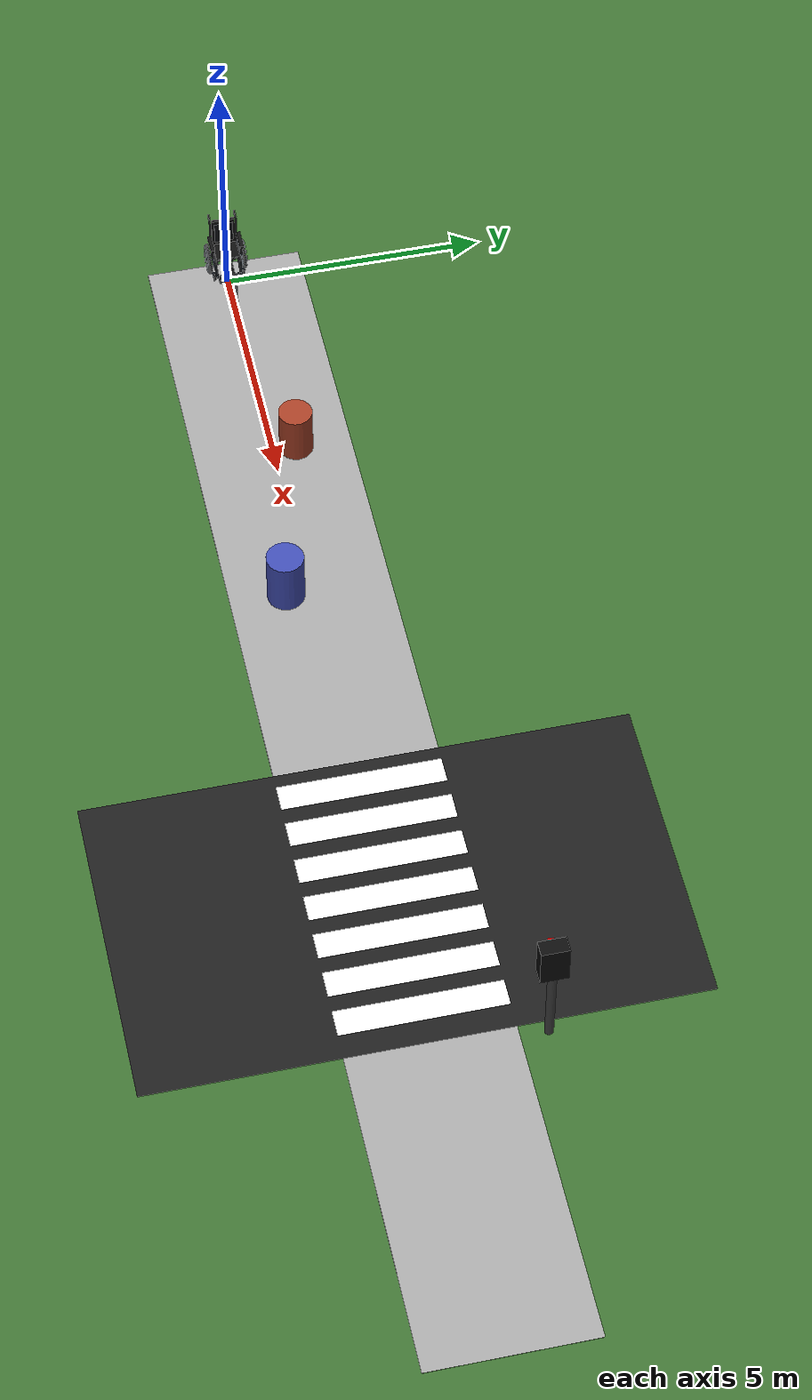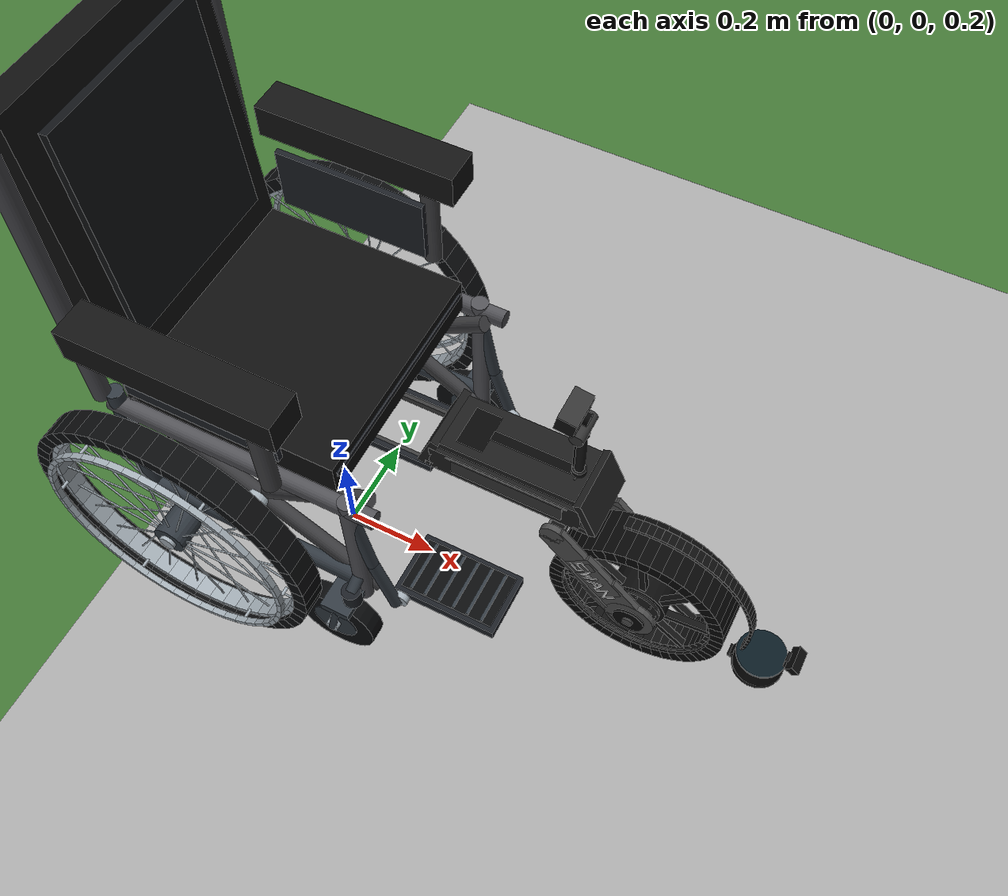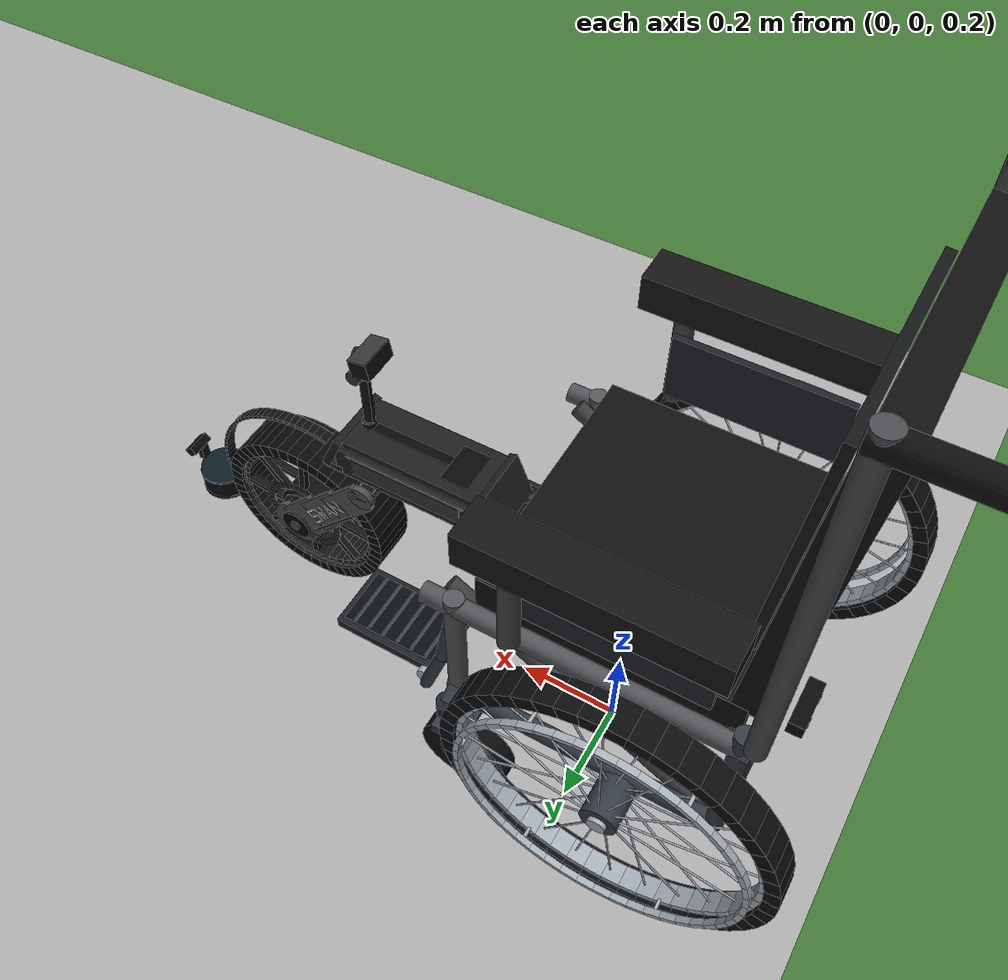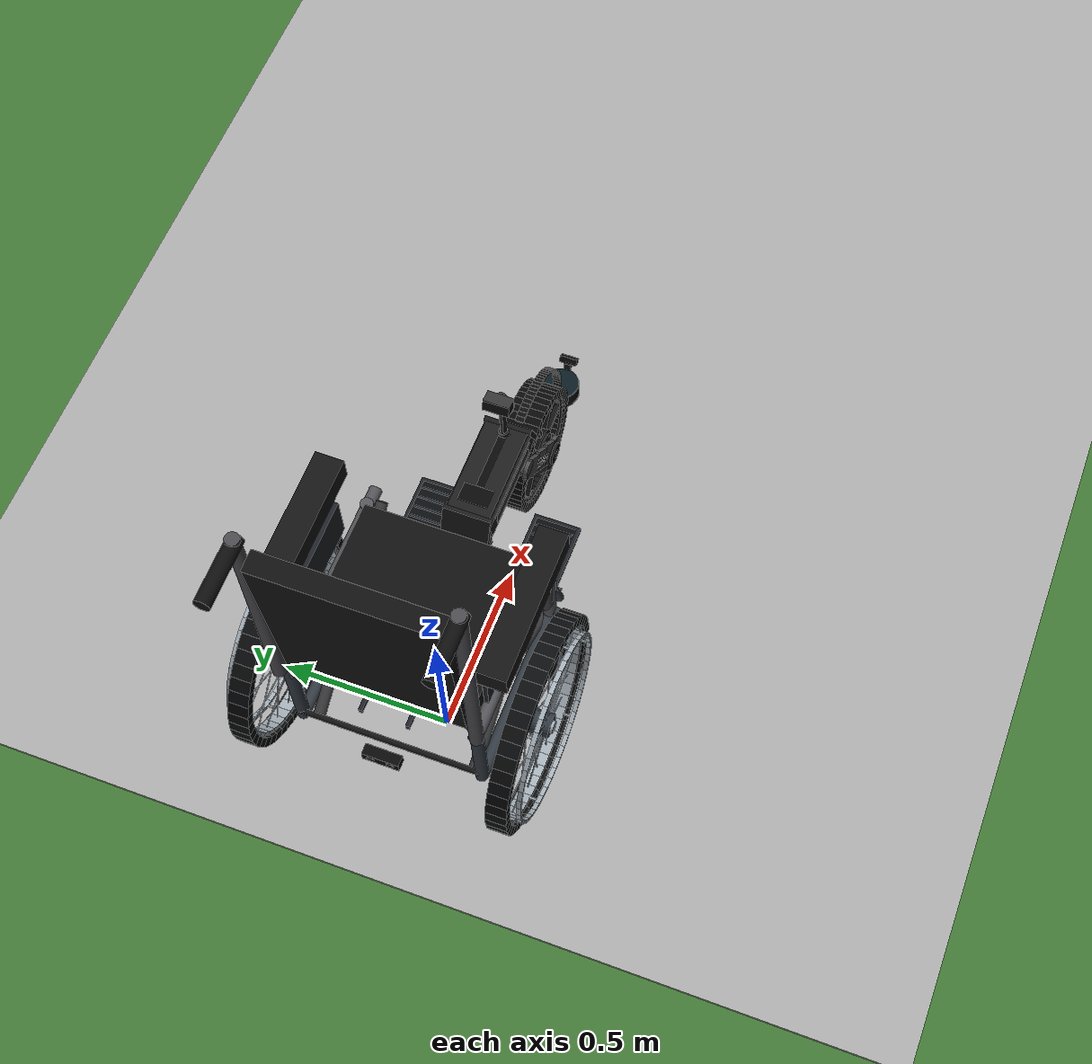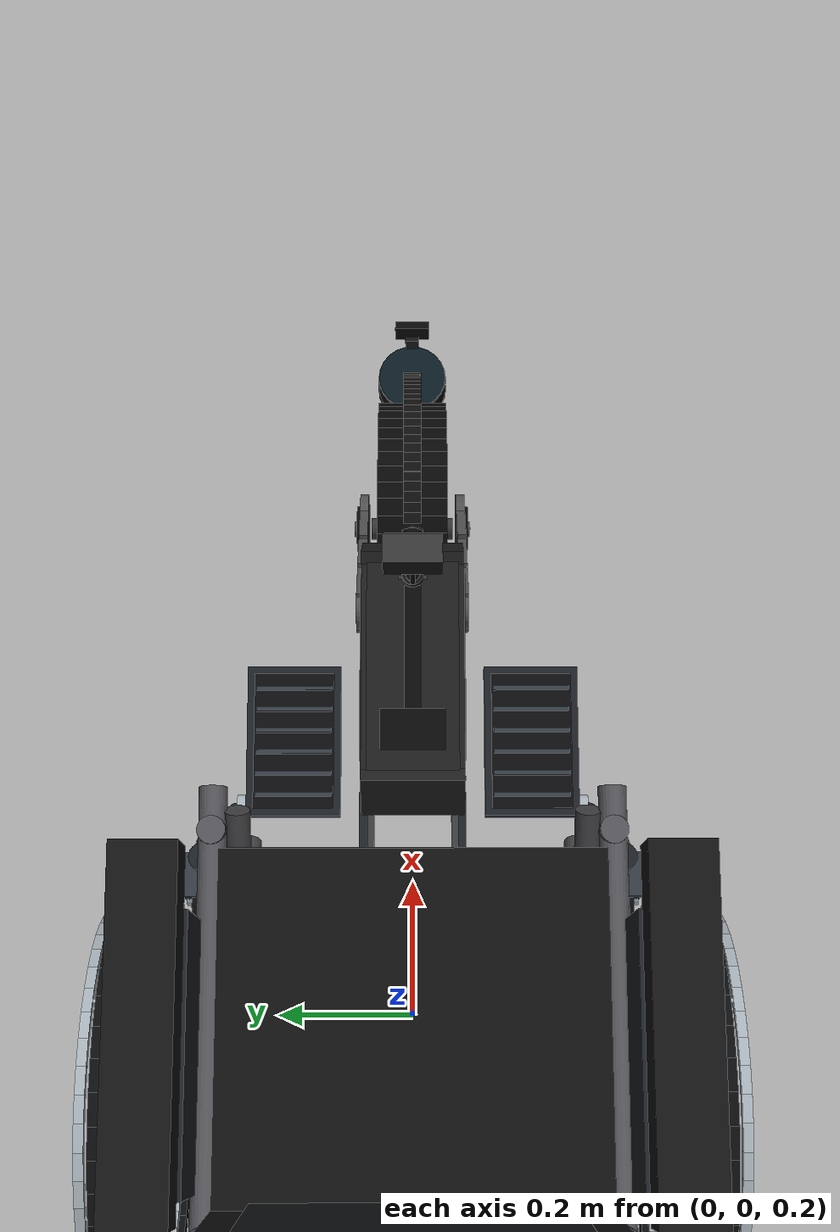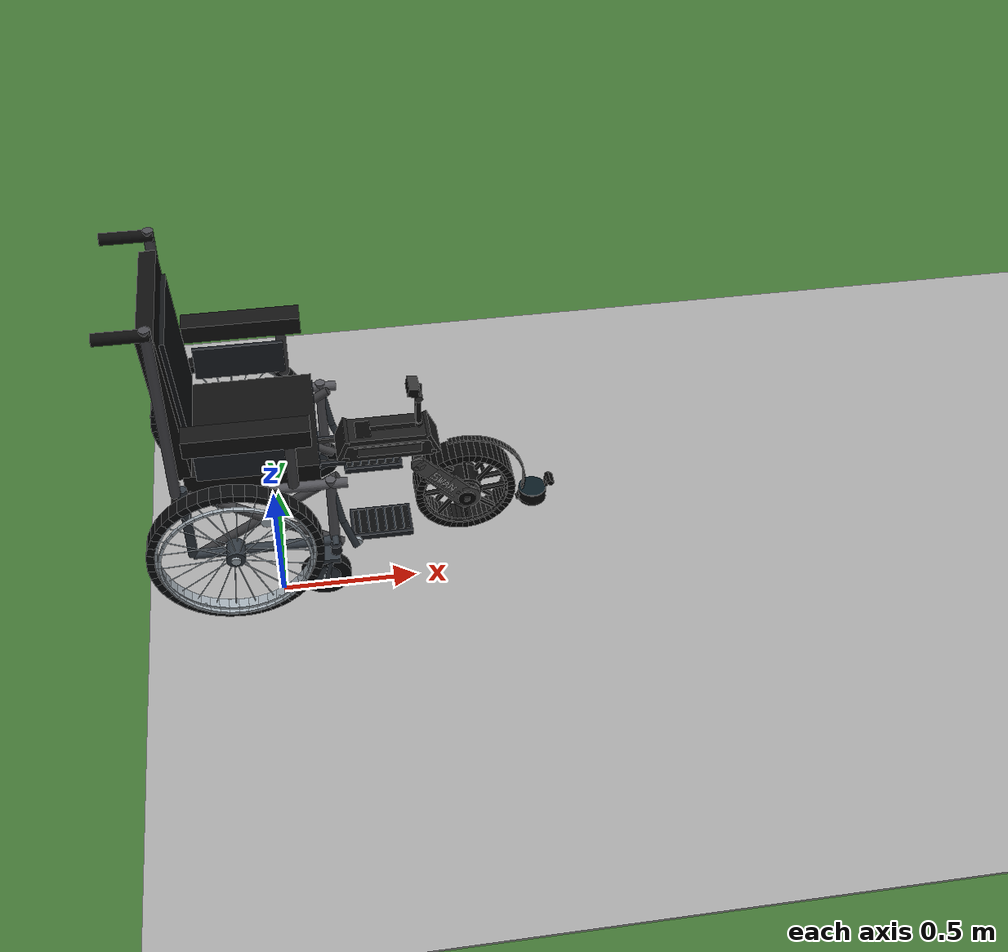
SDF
<?xml version="1.0" ?>
<sdf version="1.9">

  <world name="swan_test_world">

    <!-- Gazebo 기본 설정              -->

    <physics name="1ms" type="ignore">
      <max_step_size>0.001</max_step_size>
      <real_time_factor>1.0</real_time_factor>
    </physics>

    <plugin
      filename="gz-sim-physics-system"
      name="gz::sim::systems::Physics"/>

    <plugin
      filename="gz-sim-scene-broadcaster-system"
      name="gz::sim::systems::SceneBroadcaster"/>

    <plugin
      filename="gz-sim-sensors-system"
      name="gz::sim::systems::Sensors">
      <render_engine>ogre2</render_engine>
    </plugin>

    <plugin
      filename="gz-sim-user-commands-system"
      name="gz::sim::systems::UserCommands"/>

    <!-- 조명                           -->

    <light type="directional" name="sun">

      <cast_shadows>true</cast_shadows>

      <pose>0 0 20 0 0 0</pose>

      <diffuse>0.8 0.8 0.8 1</diffuse>
      <specular>0.2 0.2 0.2 1</specular>

      <attenuation>
        <range>1000</range>
        <constant>0.9</constant>
        <linear>0.01</linear>
        <quadratic>0.001</quadratic>
      </attenuation>

      <direction>-0.5 0.1 -0.9</direction>

    </light>

    <!-- 실제 충돌 바닥                 -->

    <model name="ground_plane">

      <static>true</static>

      <link name="link">

        <collision name="collision">

          <geometry>
            <plane>
              <normal>0 0 1</normal>
              <size>100 100</size>
            </plane>
          </geometry>

        </collision>

        <visual name="visual">

          <geometry>
            <plane>
              <normal>0 0 1</normal>
              <size>100 100</size>
            </plane>
          </geometry>

          <material>
            <ambient>0.25 0.45 0.20 1</ambient>
            <diffuse>0.25 0.45 0.20 1</diffuse>
          </material>

        </visual>

      </link>

    </model>

    <!-- 시작 구간 인도                                      -->

    <model name="sidewalk_start">

      <static>true</static>

      <pose>5.75 0 0.006 0 0 0</pose>

      <link name="link">

        <!--
          시각 요소만 사용.
          실제 충돌은 ground_plane이 담당.
        -->
        <visual name="visual">

          <geometry>
            <box>
              <size>12.5 3.0 0.01</size>
            </box>
          </geometry>

          <material>
            <ambient>0.65 0.65 0.65 1</ambient>
            <diffuse>0.65 0.65 0.65 1</diffuse>
          </material>

        </visual>

      </link>

    </model>

    <!-- 장애물 1 -->
    <model name="obstacle_1">

      <static>true</static>

      <pose>4.5 0.45 0.5 0 0 0</pose>

      <link name="link">

        <collision name="collision">
          <geometry>
            <cylinder>
              <radius>0.32</radius>
              <length>1.0</length>
            </cylinder>
          </geometry>
        </collision>

        <visual name="visual">
          <geometry>
            <cylinder>
              <radius>0.32</radius>
              <length>1.0</length>
            </cylinder>
          </geometry>

          <material>
            <ambient>0.65 0.25 0.15 1</ambient>
            <diffuse>0.65 0.25 0.15 1</diffuse>
          </material>
        </visual>

      </link>

    </model>

    <!-- 장애물 2 -->
    <model name="obstacle_2">

      <static>true</static>

      <pose>8.0 -0.45 0.55 0 0 0</pose>

      <link name="link">

        <collision name="collision">
          <geometry>
            <cylinder>
              <radius>0.35</radius>
              <length>1.1</length>
            </cylinder>
          </geometry>
        </collision>

        <visual name="visual">
          <geometry>
            <cylinder>
              <radius>0.35</radius>
              <length>1.1</length>
            </cylinder>
          </geometry>

          <material>
            <ambient>0.25 0.30 0.70 1</ambient>
            <diffuse>0.25 0.30 0.70 1</diffuse>
          </material>
        </visual>

      </link>

    </model>

    <!-- 도로                                                  -->

    <model name="road">

      <static>true</static>

      <pose>15 0 0.007 0 0 0</pose>

      <link name="link">

        <visual name="visual">

          <geometry>
            <box>
              <size>6.0 10.0 0.01</size>
            </box>
          </geometry>

          <material>
            <ambient>0.12 0.12 0.12 1</ambient>
            <diffuse>0.12 0.12 0.12 1</diffuse>
          </material>

        </visual>

      </link>

    </model>

    <!-- 횡단보도                                              -->
    <!-- 진행방향 X축                                         -->

    <model name="crosswalk_1">

      <static>true</static>
      <pose>12.5 0 0.015 0 0 0</pose>

      <link name="link">
        <visual name="visual">

          <geometry>
            <box>
              <size>0.5 3.0 0.01</size>
            </box>
          </geometry>

          <material>
            <ambient>1 1 1 1</ambient>
            <diffuse>1 1 1 1</diffuse>
          </material>

        </visual>
      </link>

    </model>

    <model name="crosswalk_2">

      <static>true</static>
      <pose>13.3 0 0.015 0 0 0</pose>

      <link name="link">
        <visual name="visual">

          <geometry>
            <box>
              <size>0.5 3.0 0.01</size>
            </box>
          </geometry>

          <material>
            <ambient>1 1 1 1</ambient>
            <diffuse>1 1 1 1</diffuse>
          </material>

        </visual>
      </link>

    </model>

    <model name="crosswalk_3">

      <static>true</static>
      <pose>14.1 0 0.015 0 0 0</pose>

      <link name="link">
        <visual name="visual">

          <geometry>
            <box>
              <size>0.5 3.0 0.01</size>
            </box>
          </geometry>

          <material>
            <ambient>1 1 1 1</ambient>
            <diffuse>1 1 1 1</diffuse>
          </material>

        </visual>
      </link>

    </model>

    <model name="crosswalk_4">

      <static>true</static>
      <pose>14.9 0 0.015 0 0 0</pose>

      <link name="link">
        <visual name="visual">

          <geometry>
            <box>
              <size>0.5 3.0 0.01</size>
            </box>
          </geometry>

          <material>
            <ambient>1 1 1 1</ambient>
            <diffuse>1 1 1 1</diffuse>
          </material>

        </visual>
      </link>

    </model>

    <model name="crosswalk_5">

      <static>true</static>
      <pose>15.7 0 0.015 0 0 0</pose>

      <link name="link">
        <visual name="visual">

          <geometry>
            <box>
              <size>0.5 3.0 0.01</size>
            </box>
          </geometry>

          <material>
            <ambient>1 1 1 1</ambient>
            <diffuse>1 1 1 1</diffuse>
          </material>

        </visual>
      </link>

    </model>

    <model name="crosswalk_6">

      <static>true</static>
      <pose>16.5 0 0.015 0 0 0</pose>

      <link name="link">
        <visual name="visual">

          <geometry>
            <box>
              <size>0.5 3.0 0.01</size>
            </box>
          </geometry>

          <material>
            <ambient>1 1 1 1</ambient>
            <diffuse>1 1 1 1</diffuse>
          </material>

        </visual>
      </link>

    </model>

    <model name="crosswalk_7">

      <static>true</static>
      <pose>17.3 0 0.015 0 0 0</pose>

      <link name="link">
        <visual name="visual">

          <geometry>
            <box>
              <size>0.5 3.0 0.01</size>
            </box>
          </geometry>

          <material>
            <ambient>1 1 1 1</ambient>
            <diffuse>1 1 1 1</diffuse>
          </material>

        </visual>
      </link>

    </model>

    <!-- 신호등 기둥                                          -->
    <!-- 횡단보도 오른쪽 바깥                                 -->

    <model name="traffic_light_pole">

      <static>true</static>

      <pose>18.2 2.0 1.0 0 0 0</pose>

      <link name="link">

        <collision name="collision">

          <geometry>
            <cylinder>
              <radius>0.08</radius>
              <length>2.0</length>
            </cylinder>
          </geometry>

        </collision>

        <visual name="visual">

          <geometry>
            <cylinder>
              <radius>0.08</radius>
              <length>2.0</length>
            </cylinder>
          </geometry>

          <material>
            <ambient>0.25 0.25 0.25 1</ambient>
            <diffuse>0.25 0.25 0.25 1</diffuse>
          </material>

        </visual>

      </link>

    </model>

    <!-- 신호등 본체                                          -->

    <model name="traffic_light_head">

      <static>true</static>

      <pose>18.2 2.0 2.15 0 0 0</pose>

      <link name="link">

        <visual name="visual">

          <geometry>
            <box>
              <size>0.28 0.50 0.80</size>
            </box>
          </geometry>

          <material>
            <ambient>0.05 0.05 0.05 1</ambient>
            <diffuse>0.05 0.05 0.05 1</diffuse>
          </material>

        </visual>

      </link>

    </model>

    <!-- 빨간불 : 기본 ON                                     -->
    <!-- 카메라 방향(-X)쪽으로 살짝 돌출                      -->

    <model name="traffic_light_red">

      <static>true</static>

      <pose>18.04 2.0 2.37 0 0 0</pose>

      <link name="link">

        <visual name="visual">

          <geometry>
            <sphere>
              <radius>0.11</radius>
            </sphere>
          </geometry>

          <material>
            <ambient>1 0 0 1</ambient>
            <diffuse>1 0 0 1</diffuse>
            <emissive>0.8 0 0 1</emissive>
          </material>

        </visual>

      </link>

    </model>

    <!-- 초록불 : 기본 OFF                                    -->

    <model name="traffic_light_green">

      <static>true</static>

      <pose>18.04 2.0 1.94 0 0 0</pose>

      <link name="link">

        <visual name="visual">

          <geometry>
            <sphere>
              <radius>0.11</radius>
            </sphere>
          </geometry>

          <material>
            <ambient>0.05 0.08 0.05 1</ambient>
            <diffuse>0.05 0.08 0.05 1</diffuse>
          </material>

        </visual>

      </link>

    </model>

    <!-- 반대편 인도                                          -->

    <model name="sidewalk_end">

      <static>true</static>

      <pose>21 0 0.006 0 0 0</pose>

      <link name="link">

        <visual name="visual">

          <geometry>
            <box>
              <size>6.0 3.0 0.01</size>
            </box>
          </geometry>

          <material>
            <ambient>0.65 0.65 0.65 1</ambient>
            <diffuse>0.65 0.65 0.65 1</diffuse>
          </material>

        </visual>

      </link>

    </model>

    <!-- 휠체어                                                -->
    <!-- 시작 방향 = +X                                      -->

    <include>

      <uri>model://wheelchair</uri>

      <name>wheelchair</name>

      <pose>0 0 0.30 0 0 0</pose>

    </include>

  </world>

</sdf>

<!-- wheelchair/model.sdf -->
<sdf version="1.10">
  <model name="wheelchair">

    <pose>0 0 0 0 0 0</pose>

    <link name="base_link">

      <inertial>
        <pose>-0.05 0 0.40 0 0 0</pose>

        <mass>40.0</mass>

        <inertia>
          <ixx>3.0</ixx>
          <iyy>4.0</iyy>
          <izz>4.0</izz>
          <ixy>0.0</ixy>
          <ixz>0.0</ixz>
          <iyz>0.0</iyz>
        </inertia>
      </inertial>

      <!-- Wheelchair collisions -->

      <collision name="wheelchair_lower_collision">
        <pose>-0.02 0 0.34 0 0 0</pose>

        <geometry>
          <box>
            <size>0.62 0.48 0.10</size>
          </box>
        </geometry>
      </collision>

      <collision name="seat_collision">
        <pose>-0.05 0 0.51 0 0 0</pose>

        <geometry>
          <box>
            <size>0.44 0.46 0.08</size>
          </box>
        </geometry>
      </collision>

      <collision name="backrest_collision">
        <pose>-0.29 0 0.82 0 0 0</pose>

        <geometry>
          <box>
            <size>0.065 0.46 0.58</size>
          </box>
        </geometry>
      </collision>

      <!-- SWAN collision remains simple -->

      <!-- Wheelchair seat -->

      <!-- Wheelchair backrest -->

      <!-- Back posts -->

      <!-- Push handles -->

      <!-- Armrests -->

      <!-- Wheelchair frame -->

      <!-- Wheelchair folding braces -->

      <!-- Footrests -->

      <!-- Front casters: separate swivel links (see below) -->

      <!-- SWAN connection arms -->

      <!-- SWAN upper side plates -->

      <!-- SWAN diagonal lower plates -->

      <!-- SWAN rear side plates -->

      <!-- SWAN front short plates -->

      <!-- SWAN small center enclosure -->

      <!-- SWAN front cross member -->

      <!-- SWAN rear cross member -->

      <!-- Redesigned appearance only; no added physical elements. -->
      <visual name="seat_visual">
        <pose>-0.05 0 0.51 0 0 0</pose>

        <geometry>
          <box>
            <size>0.44 0.46 0.075</size>
          </box>
        </geometry>

        <material>
          <ambient>0.025 0.025 0.025 1</ambient>
          <diffuse>0.055 0.055 0.055 1</diffuse>
        </material>

      </visual>

      <visual name="backrest_visual">
        <pose>-0.29 0 0.83 0 -0.07 0</pose>

        <geometry>
          <box>
            <size>0.055 0.46 0.58</size>
          </box>
        </geometry>

        <material>
          <ambient>0.025 0.025 0.025 1</ambient>
          <diffuse>0.055 0.055 0.055 1</diffuse>
        </material>

      </visual>

      <visual name="back_left_post">
        <pose>-0.3 0.255 0.84 0 0 0</pose>

        <geometry><cylinder><radius>0.0175</radius><length>0.68</length></cylinder></geometry>
        <material>
          <ambient>0.15 0.15 0.15 1</ambient>
          <diffuse>0.28 0.28 0.30 1</diffuse>
        </material>

      </visual>

      <visual name="back_right_post">
        <pose>-0.3 -0.255 0.84 0 0 0</pose>

        <geometry><cylinder><radius>0.0175</radius><length>0.68</length></cylinder></geometry>
        <material>
          <ambient>0.15 0.15 0.15 1</ambient>
          <diffuse>0.28 0.28 0.30 1</diffuse>
        </material>

      </visual>

      <visual name="left_push_handle">
        <pose>-0.37 0.255 1.16 0 1.570796 0</pose>

        <geometry><cylinder><radius>0.02</radius><length>0.17</length></cylinder></geometry>
        <material>
          <ambient>0.025 0.025 0.025 1</ambient>
          <diffuse>0.05 0.05 0.05 1</diffuse>
        </material>

      </visual>

      <visual name="right_push_handle">
        <pose>-0.37 -0.255 1.16 0 1.570796 0</pose>

        <geometry><cylinder><radius>0.02</radius><length>0.17</length></cylinder></geometry>
        <material>
          <ambient>0.025 0.025 0.025 1</ambient>
          <diffuse>0.05 0.05 0.05 1</diffuse>
        </material>

      </visual>

      <visual name="left_armrest">
        <pose>-0.05 0.285 0.75 0 0 0</pose>

        <geometry>
          <box>
            <size>0.40 0.075 0.065</size>
          </box>
        </geometry>

        <material>
          <ambient>0.03 0.03 0.03 1</ambient>
          <diffuse>0.07 0.07 0.07 1</diffuse>
        </material>

      </visual>

      <visual name="right_armrest">
        <pose>-0.05 -0.285 0.75 0 0 0</pose>

        <geometry>
          <box>
            <size>0.40 0.075 0.065</size>
          </box>
        </geometry>

        <material>
          <ambient>0.03 0.03 0.03 1</ambient>
          <diffuse>0.07 0.07 0.07 1</diffuse>
        </material>

      </visual>

      <visual name="left_armrest_support">
        <pose>0.08 0.285 0.64 0 0 0</pose>

        <geometry><cylinder><radius>0.0175</radius><length>0.24</length></cylinder></geometry>
        <material>
          <ambient>0.12 0.12 0.12 1</ambient>
          <diffuse>0.25 0.25 0.26 1</diffuse>
        </material>

      </visual>

      <visual name="right_armrest_support">
        <pose>0.08 -0.285 0.64 0 0 0</pose>

        <geometry><cylinder><radius>0.0175</radius><length>0.24</length></cylinder></geometry>
        <material>
          <ambient>0.12 0.12 0.12 1</ambient>
          <diffuse>0.25 0.25 0.26 1</diffuse>
        </material>

      </visual>

      <visual name="left_upper_frame">
        <pose>-0.02 0.245 0.47 0 1.570796 0</pose>

        <geometry><cylinder><radius>0.0175</radius><length>0.55</length></cylinder></geometry>
        <material>
          <ambient>0.18 0.18 0.18 1</ambient>
          <diffuse>0.32 0.32 0.34 1</diffuse>
        </material>

      </visual>

      <visual name="right_upper_frame">
        <pose>-0.02 -0.245 0.47 0 1.570796 0</pose>

        <geometry><cylinder><radius>0.0175</radius><length>0.55</length></cylinder></geometry>
        <material>
          <ambient>0.18 0.18 0.18 1</ambient>
          <diffuse>0.32 0.32 0.34 1</diffuse>
        </material>

      </visual>

      <visual name="left_front_frame">
        <pose>0.2 0.245 0.32 0 0 0</pose>

        <geometry><cylinder><radius>0.0175</radius><length>0.34</length></cylinder></geometry>
        <material>
          <ambient>0.18 0.18 0.18 1</ambient>
          <diffuse>0.32 0.32 0.34 1</diffuse>
        </material>

      </visual>

      <visual name="right_front_frame">
        <pose>0.2 -0.245 0.32 0 0 0</pose>

        <geometry><cylinder><radius>0.0175</radius><length>0.34</length></cylinder></geometry>
        <material>
          <ambient>0.18 0.18 0.18 1</ambient>
          <diffuse>0.32 0.32 0.34 1</diffuse>
        </material>

      </visual>

      <visual name="left_cross_frame_1">
        <pose>-0.02 0.225 0.32 0 2.130796 0</pose>

        <geometry><cylinder><radius>0.016</radius><length>0.58</length></cylinder></geometry>
        <material>
          <ambient>0.10 0.10 0.10 1</ambient>
          <diffuse>0.24 0.24 0.25 1</diffuse>
        </material>

      </visual>

      <visual name="left_cross_frame_2">
        <pose>-0.02 0.215 0.32 0 1.010796 0</pose>

        <geometry><cylinder><radius>0.016</radius><length>0.58</length></cylinder></geometry>
        <material>
          <ambient>0.10 0.10 0.10 1</ambient>
          <diffuse>0.24 0.24 0.25 1</diffuse>
        </material>

      </visual>

      <visual name="right_cross_frame_1">
        <pose>-0.02 -0.225 0.32 0 2.130796 0</pose>

        <geometry><cylinder><radius>0.016</radius><length>0.58</length></cylinder></geometry>
        <material>
          <ambient>0.10 0.10 0.10 1</ambient>
          <diffuse>0.24 0.24 0.25 1</diffuse>
        </material>

      </visual>

      <visual name="right_cross_frame_2">
        <pose>-0.02 -0.215 0.32 0 1.010796 0</pose>

        <geometry><cylinder><radius>0.016</radius><length>0.58</length></cylinder></geometry>
        <material>
          <ambient>0.10 0.10 0.10 1</ambient>
          <diffuse>0.24 0.24 0.25 1</diffuse>
        </material>

      </visual>

      <visual name="seat_front_piping">
        <pose>0.17 0 0.523 0 0 0</pose>
        <geometry><box><size>0.006 0.44 0.012</size></box></geometry>
        <material><ambient>0.063 0.072 0.084 1</ambient><diffuse>0.105 0.12 0.14 1</diffuse><specular>0.06 0.06 0.06 1</specular></material>
      </visual>
      <visual name="backrest_center_pad">
        <pose>-0.253 0 0.84 0 -0.07 0</pose>
        <geometry><box><size>0.016 0.36 0.44</size></box></geometry>
        <material><ambient>0.039 0.0438 0.0498 1</ambient><diffuse>0.065 0.073 0.083 1</diffuse><specular>0.06 0.06 0.06 1</specular></material>
      </visual>
      <visual name="left_lower_rail">
        <pose>-0.04 0.245 0.2 0 1.570796 0</pose>
        <geometry><cylinder><radius>0.017</radius><length>0.48</length></cylinder></geometry>
        <material><ambient>0.114 0.132 0.15 1</ambient><diffuse>0.19 0.22 0.25 1</diffuse><specular>0.06 0.06 0.06 1</specular></material>
      </visual>
      <visual name="left_rear_frame">
        <pose>-0.28 0.245 0.355 0 0 0</pose>
        <geometry><cylinder><radius>0.017</radius><length>0.31</length></cylinder></geometry>
        <material><ambient>0.114 0.132 0.15 1</ambient><diffuse>0.19 0.22 0.25 1</diffuse><specular>0.06 0.06 0.06 1</specular></material>
      </visual>
      <visual name="left_brace_pivot">
        <pose>-0.02 0.24 0.32 1.570796 0 0</pose>
        <geometry><cylinder><radius>0.023</radius><length>0.014</length></cylinder></geometry>
        <material><ambient>0.384 0.408 0.426 1</ambient><diffuse>0.64 0.68 0.71 1</diffuse><specular>0.25 0.25 0.25 1</specular></material>
      </visual>
      <visual name="left_seat_side_guard">
        <pose>-0.07 0.253 0.62 0 0 0</pose>
        <geometry><box><size>0.31 0.012 0.13</size></box></geometry>
        <material><ambient>0.063 0.072 0.084 1</ambient><diffuse>0.105 0.12 0.14 1</diffuse><specular>0.06 0.06 0.06 1</specular></material>
      </visual>

      <visual name="right_lower_rail">
        <pose>-0.04 -0.245 0.2 0 1.570796 0</pose>
        <geometry><cylinder><radius>0.017</radius><length>0.48</length></cylinder></geometry>
        <material><ambient>0.114 0.132 0.15 1</ambient><diffuse>0.19 0.22 0.25 1</diffuse><specular>0.06 0.06 0.06 1</specular></material>
      </visual>
      <visual name="right_rear_frame">
        <pose>-0.28 -0.245 0.355 0 0 0</pose>
        <geometry><cylinder><radius>0.017</radius><length>0.31</length></cylinder></geometry>
        <material><ambient>0.114 0.132 0.15 1</ambient><diffuse>0.19 0.22 0.25 1</diffuse><specular>0.06 0.06 0.06 1</specular></material>
      </visual>
      <visual name="right_brace_pivot">
        <pose>-0.02 -0.24 0.32 1.570796 0 0</pose>
        <geometry><cylinder><radius>0.023</radius><length>0.014</length></cylinder></geometry>
        <material><ambient>0.384 0.408 0.426 1</ambient><diffuse>0.64 0.68 0.71 1</diffuse><specular>0.25 0.25 0.25 1</specular></material>
      </visual>
      <visual name="right_seat_side_guard">
        <pose>-0.07 -0.253 0.62 0 0 0</pose>
        <geometry><box><size>0.31 0.012 0.13</size></box></geometry>
        <material><ambient>0.063 0.072 0.084 1</ambient><diffuse>0.105 0.12 0.14 1</diffuse><specular>0.06 0.06 0.06 1</specular></material>
      </visual>

      <!-- Refined leg clearance, compact panels and fixed sensor fairing: visuals only.
           Footplates leave a 0.20 m centre gap so the SWAN fork and drive wheel
           can slide back between them. -->
      <visual name="left_footplate">
        <pose>0.365 0.165 0.18 0 0 0</pose>
        <geometry><box><size>0.21 0.13 0.022</size></box></geometry>
        <material><ambient>0.063 0.072 0.084 1</ambient><diffuse>0.105 0.12 0.14 1</diffuse><specular>0.06 0.06 0.06 1</specular></material>
      </visual>
      <visual name="left_footpad">
        <pose>0.365 0.165 0.192 0 0 0</pose>
        <geometry><box><size>0.19 0.111 0.003</size></box></geometry>
        <material><ambient>0.021 0.0234 0.0264 1</ambient><diffuse>0.035 0.039 0.044 1</diffuse><specular>0.06 0.06 0.06 1</specular></material>
      </visual>
      <visual name="left_foot_grip_0">
        <pose>0.289 0.165 0.194 0 0 0</pose>
        <geometry><box><size>0.006 0.105 0.002</size></box></geometry>
        <material><ambient>0.114 0.132 0.15 1</ambient><diffuse>0.19 0.22 0.25 1</diffuse><specular>0.06 0.06 0.06 1</specular></material>
      </visual>
      <visual name="left_foot_grip_1">
        <pose>0.319 0.165 0.194 0 0 0</pose>
        <geometry><box><size>0.006 0.105 0.002</size></box></geometry>
        <material><ambient>0.114 0.132 0.15 1</ambient><diffuse>0.19 0.22 0.25 1</diffuse><specular>0.06 0.06 0.06 1</specular></material>
      </visual>
      <visual name="left_foot_grip_2">
        <pose>0.349 0.165 0.194 0 0 0</pose>
        <geometry><box><size>0.006 0.105 0.002</size></box></geometry>
        <material><ambient>0.114 0.132 0.15 1</ambient><diffuse>0.19 0.22 0.25 1</diffuse><specular>0.06 0.06 0.06 1</specular></material>
      </visual>
      <visual name="left_foot_grip_3">
        <pose>0.379 0.165 0.194 0 0 0</pose>
        <geometry><box><size>0.006 0.105 0.002</size></box></geometry>
        <material><ambient>0.114 0.132 0.15 1</ambient><diffuse>0.19 0.22 0.25 1</diffuse><specular>0.06 0.06 0.06 1</specular></material>
      </visual>
      <visual name="left_foot_grip_4">
        <pose>0.409 0.165 0.194 0 0 0</pose>
        <geometry><box><size>0.006 0.105 0.002</size></box></geometry>
        <material><ambient>0.114 0.132 0.15 1</ambient><diffuse>0.19 0.22 0.25 1</diffuse><specular>0.06 0.06 0.06 1</specular></material>
      </visual>
      <visual name="left_foot_grip_5">
        <pose>0.439 0.165 0.194 0 0 0</pose>
        <geometry><box><size>0.006 0.105 0.002</size></box></geometry>
        <material><ambient>0.114 0.132 0.15 1</ambient><diffuse>0.19 0.22 0.25 1</diffuse><specular>0.06 0.06 0.06 1</specular></material>
      </visual>
      <visual name="left_footrest_hanger_upper">
        <pose>0.215 0.245 0.375 0 2.96692 0</pose>
        <geometry><cylinder><radius>0.012</radius><length>0.1726268</length></cylinder></geometry>
        <material><ambient>0.114 0.132 0.15 1</ambient><diffuse>0.19 0.22 0.25 1</diffuse><specular>0.06 0.06 0.06 1</specular></material>
      </visual>
      <visual name="left_footrest_hanger_lower">
        <pose>0.25 0.245 0.226 0 2.838708 0</pose>
        <geometry><cylinder><radius>0.012</radius><length>0.1341044</length></cylinder></geometry>
        <material><ambient>0.114 0.132 0.15 1</ambient><diffuse>0.19 0.22 0.25 1</diffuse><specular>0.06 0.06 0.06 1</specular></material>
      </visual>
      <visual name="left_footrest_underplate">
        <pose>0.28 0.195 0.162 0 1.570796 -1.373401</pose>
        <geometry><cylinder><radius>0.01</radius><length>0.1019804</length></cylinder></geometry>
        <material><ambient>0.114 0.132 0.15 1</ambient><diffuse>0.19 0.22 0.25 1</diffuse><specular>0.06 0.06 0.06 1</specular></material>
      </visual>
      <visual name="left_footplate_pivot">
        <pose>0.275 0.235 0.17 1.570796 0 0</pose>
        <geometry><cylinder><radius>0.017</radius><length>0.015</length></cylinder></geometry>
        <material><ambient>0.384 0.408 0.426 1</ambient><diffuse>0.64 0.68 0.71 1</diffuse><specular>0.25 0.25 0.25 1</specular></material>
      </visual>
      <visual name="left_caster_frame_mount">
        <pose>0.2 0.265 0.225 0 2.034444 1.570796</pose>
        <geometry><cylinder><radius>0.012</radius><length>0.04472136</length></cylinder></geometry>
        <material><ambient>0.114 0.132 0.15 1</ambient><diffuse>0.19 0.22 0.25 1</diffuse><specular>0.06 0.06 0.06 1</specular></material>
      </visual>

      <visual name="right_footplate">
        <pose>0.365 -0.165 0.18 0 0 0</pose>
        <geometry><box><size>0.21 0.13 0.022</size></box></geometry>
        <material><ambient>0.063 0.072 0.084 1</ambient><diffuse>0.105 0.12 0.14 1</diffuse><specular>0.06 0.06 0.06 1</specular></material>
      </visual>
      <visual name="right_footpad">
        <pose>0.365 -0.165 0.192 0 0 0</pose>
        <geometry><box><size>0.19 0.111 0.003</size></box></geometry>
        <material><ambient>0.021 0.0234 0.0264 1</ambient><diffuse>0.035 0.039 0.044 1</diffuse><specular>0.06 0.06 0.06 1</specular></material>
      </visual>
      <visual name="right_foot_grip_0">
        <pose>0.289 -0.165 0.194 0 0 0</pose>
        <geometry><box><size>0.006 0.105 0.002</size></box></geometry>
        <material><ambient>0.114 0.132 0.15 1</ambient><diffuse>0.19 0.22 0.25 1</diffuse><specular>0.06 0.06 0.06 1</specular></material>
      </visual>
      <visual name="right_foot_grip_1">
        <pose>0.319 -0.165 0.194 0 0 0</pose>
        <geometry><box><size>0.006 0.105 0.002</size></box></geometry>
        <material><ambient>0.114 0.132 0.15 1</ambient><diffuse>0.19 0.22 0.25 1</diffuse><specular>0.06 0.06 0.06 1</specular></material>
      </visual>
      <visual name="right_foot_grip_2">
        <pose>0.349 -0.165 0.194 0 0 0</pose>
        <geometry><box><size>0.006 0.105 0.002</size></box></geometry>
        <material><ambient>0.114 0.132 0.15 1</ambient><diffuse>0.19 0.22 0.25 1</diffuse><specular>0.06 0.06 0.06 1</specular></material>
      </visual>
      <visual name="right_foot_grip_3">
        <pose>0.379 -0.165 0.194 0 0 0</pose>
        <geometry><box><size>0.006 0.105 0.002</size></box></geometry>
        <material><ambient>0.114 0.132 0.15 1</ambient><diffuse>0.19 0.22 0.25 1</diffuse><specular>0.06 0.06 0.06 1</specular></material>
      </visual>
      <visual name="right_foot_grip_4">
        <pose>0.409 -0.165 0.194 0 0 0</pose>
        <geometry><box><size>0.006 0.105 0.002</size></box></geometry>
        <material><ambient>0.114 0.132 0.15 1</ambient><diffuse>0.19 0.22 0.25 1</diffuse><specular>0.06 0.06 0.06 1</specular></material>
      </visual>
      <visual name="right_foot_grip_5">
        <pose>0.439 -0.165 0.194 0 0 0</pose>
        <geometry><box><size>0.006 0.105 0.002</size></box></geometry>
        <material><ambient>0.114 0.132 0.15 1</ambient><diffuse>0.19 0.22 0.25 1</diffuse><specular>0.06 0.06 0.06 1</specular></material>
      </visual>
      <visual name="right_footrest_hanger_upper">
        <pose>0.215 -0.245 0.375 0 2.96692 0</pose>
        <geometry><cylinder><radius>0.012</radius><length>0.1726268</length></cylinder></geometry>
        <material><ambient>0.114 0.132 0.15 1</ambient><diffuse>0.19 0.22 0.25 1</diffuse><specular>0.06 0.06 0.06 1</specular></material>
      </visual>
      <visual name="right_footrest_hanger_lower">
        <pose>0.25 -0.245 0.226 0 2.838708 0</pose>
        <geometry><cylinder><radius>0.012</radius><length>0.1341044</length></cylinder></geometry>
        <material><ambient>0.114 0.132 0.15 1</ambient><diffuse>0.19 0.22 0.25 1</diffuse><specular>0.06 0.06 0.06 1</specular></material>
      </visual>
      <visual name="right_footrest_underplate">
        <pose>0.28 -0.195 0.162 0 1.570796 1.373401</pose>
        <geometry><cylinder><radius>0.01</radius><length>0.1019804</length></cylinder></geometry>
        <material><ambient>0.114 0.132 0.15 1</ambient><diffuse>0.19 0.22 0.25 1</diffuse><specular>0.06 0.06 0.06 1</specular></material>
      </visual>
      <visual name="right_footplate_pivot">
        <pose>0.275 -0.235 0.17 1.570796 0 0</pose>
        <geometry><cylinder><radius>0.017</radius><length>0.015</length></cylinder></geometry>
        <material><ambient>0.384 0.408 0.426 1</ambient><diffuse>0.64 0.68 0.71 1</diffuse><specular>0.25 0.25 0.25 1</specular></material>
      </visual>
      <visual name="right_caster_frame_mount">
        <pose>0.2 -0.265 0.225 0 2.034444 -1.570796</pose>
        <geometry><cylinder><radius>0.012</radius><length>0.04472136</length></cylinder></geometry>
        <material><ambient>0.114 0.132 0.15 1</ambient><diffuse>0.19 0.22 0.25 1</diffuse><specular>0.06 0.06 0.06 1</specular></material>
      </visual>

      <!-- Fixed front cover and integrated sensor pod: visuals only. -->

      <!-- Thin fixed mudguard; minimal rear-only sensor support, no enclosing pod. -->

      <visual name="swan_slide_rail_left">
        <pose>-0.015 0.0625 0.385 0 0 0</pose>
        <geometry><box><size>0.55 0.01 0.018</size></box></geometry>
        <material><ambient>0.063 0.072 0.084 1</ambient><diffuse>0.105 0.12 0.14 1</diffuse><specular>0.06 0.06 0.06 1</specular></material>
      </visual>
      <visual name="swan_slide_rail_left_front_bracket_arm">
        <pose>0.1 0.0875 0.385 0 0 0</pose>
        <geometry><box><size>0.03 0.045 0.012</size></box></geometry>
        <material><ambient>0.114 0.132 0.15 1</ambient><diffuse>0.19 0.22 0.25 1</diffuse><specular>0.06 0.06 0.06 1</specular></material>
      </visual>
      <visual name="swan_slide_rail_left_front_bracket">
        <pose>0.1 0.105 0.429 0 0 0</pose>
        <geometry><box><size>0.03 0.01 0.087</size></box></geometry>
        <material><ambient>0.114 0.132 0.15 1</ambient><diffuse>0.19 0.22 0.25 1</diffuse><specular>0.06 0.06 0.06 1</specular></material>
      </visual>
      <visual name="swan_slide_rail_left_rear_bracket_arm">
        <pose>-0.22 0.0875 0.385 0 0 0</pose>
        <geometry><box><size>0.03 0.045 0.012</size></box></geometry>
        <material><ambient>0.114 0.132 0.15 1</ambient><diffuse>0.19 0.22 0.25 1</diffuse><specular>0.06 0.06 0.06 1</specular></material>
      </visual>
      <visual name="swan_slide_rail_left_rear_bracket">
        <pose>-0.22 0.105 0.429 0 0 0</pose>
        <geometry><box><size>0.03 0.01 0.087</size></box></geometry>
        <material><ambient>0.114 0.132 0.15 1</ambient><diffuse>0.19 0.22 0.25 1</diffuse><specular>0.06 0.06 0.06 1</specular></material>
      </visual>
      <visual name="swan_slide_rail_right">
        <pose>-0.015 -0.0625 0.385 0 0 0</pose>
        <geometry><box><size>0.55 0.01 0.018</size></box></geometry>
        <material><ambient>0.063 0.072 0.084 1</ambient><diffuse>0.105 0.12 0.14 1</diffuse><specular>0.06 0.06 0.06 1</specular></material>
      </visual>
      <visual name="swan_slide_rail_right_front_bracket_arm">
        <pose>0.1 -0.0875 0.385 0 0 0</pose>
        <geometry><box><size>0.03 0.045 0.012</size></box></geometry>
        <material><ambient>0.114 0.132 0.15 1</ambient><diffuse>0.19 0.22 0.25 1</diffuse><specular>0.06 0.06 0.06 1</specular></material>
      </visual>
      <visual name="swan_slide_rail_right_front_bracket">
        <pose>0.1 -0.105 0.429 0 0 0</pose>
        <geometry><box><size>0.03 0.01 0.087</size></box></geometry>
        <material><ambient>0.114 0.132 0.15 1</ambient><diffuse>0.19 0.22 0.25 1</diffuse><specular>0.06 0.06 0.06 1</specular></material>
      </visual>
      <visual name="swan_slide_rail_right_rear_bracket_arm">
        <pose>-0.22 -0.0875 0.385 0 0 0</pose>
        <geometry><box><size>0.03 0.045 0.012</size></box></geometry>
        <material><ambient>0.114 0.132 0.15 1</ambient><diffuse>0.19 0.22 0.25 1</diffuse><specular>0.06 0.06 0.06 1</specular></material>
      </visual>
      <visual name="swan_slide_rail_right_rear_bracket">
        <pose>-0.22 -0.105 0.429 0 0 0</pose>
        <geometry><box><size>0.03 0.01 0.087</size></box></geometry>
        <material><ambient>0.114 0.132 0.15 1</ambient><diffuse>0.19 0.22 0.25 1</diffuse><specular>0.06 0.06 0.06 1</specular></material>
      </visual>
      <!-- SENSORS-BEGIN final sensor suite (generated) -->
      <collision name="left_footrest_collision">
        <pose>0.365 0.165 0.18 0 0 0</pose>
        <geometry><box><size>0.21 0.13 0.022</size></box></geometry>
      </collision>
      <collision name="right_footrest_collision">
        <pose>0.365 -0.165 0.18 0 0 0</pose>
        <geometry><box><size>0.21 0.13 0.022</size></box></geometry>
      </collision>
      <visual name="rear_sensor_bar">
        <pose>-0.29 0 0.24 1.570796 0 0</pose>
        <geometry><cylinder><radius>0.008</radius><length>0.49</length></cylinder></geometry>
        <material><ambient>0.042 0.042 0.042 1</ambient><diffuse>0.07 0.07 0.07 1</diffuse><specular>0.05 0.05 0.05 1</specular></material>
      </visual>
      <visual name="rear_sensor_housing">
        <pose>-0.335 0 0.24 0 0 0</pose>
        <geometry><box><size>0.03 0.10 0.032</size></box></geometry>
        <material><ambient>0.018 0.018 0.018 1</ambient><diffuse>0.03 0.03 0.03 1</diffuse><specular>0.03 0.03 0.03 1</specular></material>
      </visual>
      <visual name="rear_sensor_eye_0">
        <pose>-0.3505 0.026 0.24 0 1.570796 0</pose>
        <geometry><cylinder><radius>0.011</radius><length>0.002</length></cylinder></geometry>
        <material><ambient>0.02 0.03 0.035 1</ambient><diffuse>0.05 0.075 0.085 1</diffuse><specular>0.6 0.6 0.6 1</specular></material>
      </visual>
      <visual name="rear_sensor_eye_1">
        <pose>-0.3505 -0.026 0.24 0 1.570796 0</pose>
        <geometry><cylinder><radius>0.011</radius><length>0.002</length></cylinder></geometry>
        <material><ambient>0.02 0.03 0.035 1</ambient><diffuse>0.05 0.075 0.085 1</diffuse><specular>0.6 0.6 0.6 1</specular></material>
      </visual>
      <sensor name="rear_sensor" type="gpu_lidar">
        <pose>-0.352 0 0.24 0 0 3.14159265</pose>
        <topic>/model/wheelchair/rear_scan</topic>
        <update_rate>10</update_rate>
        <always_on>true</always_on>
        <visualize>false</visualize>
        <lidar>
          <scan><horizontal><samples>31</samples><resolution>1</resolution><min_angle>-0.6</min_angle><max_angle>0.6</max_angle></horizontal></scan>
          <range><min>0.05</min><max>2.5</max><resolution>0.01</resolution></range>
          <noise><type>gaussian</type><mean>0.0</mean><stddev>0.005</stddev></noise>
        </lidar>
      </sensor>
      <sensor name="imu_sensor" type="imu">
        <topic>/model/wheelchair/imu</topic>
        <update_rate>100</update_rate>
        <always_on>true</always_on>
      </sensor>
      <sensor name="body_contact" type="contact">
        <topic>/model/wheelchair/contacts/body</topic>
        <update_rate>50</update_rate>
        <always_on>true</always_on>
        <contact>
          <collision>wheelchair_lower_collision</collision>
          <collision>seat_collision</collision>
          <collision>backrest_collision</collision>
          <collision>left_footrest_collision</collision>
          <collision>right_footrest_collision</collision>
        </contact>
      </sensor>
      <!-- SENSORS-END -->
    </link>

    <link name="swan_slide_link">
      <pose>-0.138 0 0 0 0 0</pose>
      <inertial>
        <pose>0.555 0 0.431 0 0 0</pose>
        <mass>3.0</mass>
        <inertia>
          <ixx>0.0212</ixx>
          <iyy>0.0288</iyy>
          <izz>0.0468</izz>
          <ixy>0</ixy><ixz>0</ixz><iyz>0</iyz>
        </inertia>
      </inertial>
      <collision name="swan_body_collision">
        <pose>0.555 0 0.431 0 0 0</pose>

        <geometry>
          <box>
            <size>0.34 0.13 0.08</size>
          </box>
        </geometry>
      </collision>
      <!-- Kit body: slim neck between the rider's legs, flaring into a wider head.
           The curved outline is built from thin slices; visuals only. -->
      <!-- Slide runners under the body; they ride in the under-seat rails.
           In model coordinates they span x 0.02..0.56 extended, -0.37..0.17 stowed. -->
      <!-- Kit body: slim battery/controller box with a raked nose and a
           chamfered tail, after the team's reference. Visuals only. -->
      <!-- Slide runners under the body; they ride in the under-seat rails.
           In model coordinates they span x 0.02..0.56 extended, -0.37..0.17 stowed. -->
      <!-- Kit body: slim battery/controller box with a raked nose and a
           chamfered tail, after the team's reference. Visuals only. -->
      <visual name="swan_body_main">
        <pose>0.545 0 0.4225 0 0 0</pose>
        <geometry><box><size>0.3 0.13 0.061</size></box></geometry>
        <material><ambient>0.063 0.063 0.063 1</ambient><diffuse>0.105 0.105 0.105 1</diffuse><specular>0.05 0.05 0.05 1</specular></material>
      </visual>
      <visual name="swan_body_top_deck">
        <pose>0.545 0 0.4635 0 0 0</pose>
        <geometry><box><size>0.27 0.116 0.016</size></box></geometry>
        <material><ambient>0.063 0.063 0.063 1</ambient><diffuse>0.105 0.105 0.105 1</diffuse><specular>0.05 0.05 0.05 1</specular></material>
      </visual>
      <visual name="swan_body_nose">
        <pose>0.703 0 0.432 0 -0.42 0</pose>
        <geometry><box><size>0.016 0.13 0.084</size></box></geometry>
        <material><ambient>0.063 0.063 0.063 1</ambient><diffuse>0.105 0.105 0.105 1</diffuse><specular>0.05 0.05 0.05 1</specular></material>
      </visual>
      <visual name="swan_body_nose_chin">
        <pose>0.698 0 0.399 0 0 0</pose>
        <geometry><box><size>0.03 0.13 0.014</size></box></geometry>
        <material><ambient>0.063 0.063 0.063 1</ambient><diffuse>0.105 0.105 0.105 1</diffuse><specular>0.05 0.05 0.05 1</specular></material>
      </visual>
      <visual name="swan_body_tail">
        <pose>0.392 0 0.434 0 0.38 0</pose>
        <geometry><box><size>0.016 0.13 0.086</size></box></geometry>
        <material><ambient>0.063 0.063 0.063 1</ambient><diffuse>0.105 0.105 0.105 1</diffuse><specular>0.05 0.05 0.05 1</specular></material>
      </visual>
      <visual name="swan_body_tail_foot">
        <pose>0.398 0 0.399 0 0 0</pose>
        <geometry><box><size>0.024 0.13 0.014</size></box></geometry>
        <material><ambient>0.063 0.063 0.063 1</ambient><diffuse>0.105 0.105 0.105 1</diffuse><specular>0.05 0.05 0.05 1</specular></material>
      </visual>
      <visual name="swan_body_side_panel_left">
        <pose>0.55 0.0658 0.424 0 0 0</pose>
        <geometry><box><size>0.22 0.0016 0.036</size></box></geometry>
        <material><ambient>0.12 0.12 0.12 1</ambient><diffuse>0.2 0.2 0.2 1</diffuse><specular>0.1 0.1 0.1 1</specular></material>
      </visual>
      <visual name="swan_body_side_groove_left">
        <pose>0.55 0.0662 0.447 0 0 0</pose>
        <geometry><box><size>0.24 0.001 0.0025</size></box></geometry>
        <material><ambient>0.036 0.036 0.036 1</ambient><diffuse>0.06 0.06 0.06 1</diffuse><specular>0.04 0.04 0.04 1</specular></material>
      </visual>
      <visual name="swan_body_side_panel_right">
        <pose>0.55 -0.0658 0.424 0 0 0</pose>
        <geometry><box><size>0.22 0.0016 0.036</size></box></geometry>
        <material><ambient>0.12 0.12 0.12 1</ambient><diffuse>0.2 0.2 0.2 1</diffuse><specular>0.1 0.1 0.1 1</specular></material>
      </visual>
      <visual name="swan_body_side_groove_right">
        <pose>0.55 -0.0662 0.447 0 0 0</pose>
        <geometry><box><size>0.24 0.001 0.0025</size></box></geometry>
        <material><ambient>0.036 0.036 0.036 1</ambient><diffuse>0.06 0.06 0.06 1</diffuse><specular>0.04 0.04 0.04 1</specular></material>
      </visual>
      <!-- Slide runners under the body; they ride in the under-seat rails.
           In model coordinates they span x 0.02..0.56 extended, -0.37..0.17 stowed. -->
      <visual name="swan_slide_runner_left">
        <pose>0.43 0.053 0.385 0 0 0</pose>
        <geometry><box><size>0.54 0.008 0.014</size></box></geometry>
        <material><ambient>0.132 0.132 0.132 1</ambient><diffuse>0.22 0.22 0.22 1</diffuse><specular>0.15 0.15 0.15 1</specular></material>
      </visual>
      <visual name="swan_slide_runner_left_end_stop">
        <pose>0.163 0.053 0.385 0 0 0</pose>
        <geometry><box><size>0.008 0.012 0.018</size></box></geometry>
        <material><ambient>0.036 0.036 0.036 1</ambient><diffuse>0.06 0.06 0.06 1</diffuse><specular>0.04 0.04 0.04 1</specular></material>
      </visual>
      <visual name="camera_hinge_lug_left">
        <pose>0.66 0.014 0.466 0 0 0</pose>
        <geometry><box><size>0.022 0.006 0.01</size></box></geometry>
        <material><ambient>0.036 0.036 0.036 1</ambient><diffuse>0.06 0.06 0.06 1</diffuse><specular>0.04 0.04 0.04 1</specular></material>
      </visual>
      <visual name="swan_slide_runner_right">
        <pose>0.43 -0.053 0.385 0 0 0</pose>
        <geometry><box><size>0.54 0.008 0.014</size></box></geometry>
        <material><ambient>0.132 0.132 0.132 1</ambient><diffuse>0.22 0.22 0.22 1</diffuse><specular>0.15 0.15 0.15 1</specular></material>
      </visual>
      <visual name="swan_slide_runner_right_end_stop">
        <pose>0.163 -0.053 0.385 0 0 0</pose>
        <geometry><box><size>0.008 0.012 0.018</size></box></geometry>
        <material><ambient>0.036 0.036 0.036 1</ambient><diffuse>0.06 0.06 0.06 1</diffuse><specular>0.04 0.04 0.04 1</specular></material>
      </visual>
      <visual name="camera_hinge_lug_right">
        <pose>0.66 -0.014 0.466 0 0 0</pose>
        <geometry><box><size>0.022 0.006 0.01</size></box></geometry>
        <material><ambient>0.036 0.036 0.036 1</ambient><diffuse>0.06 0.06 0.06 1</diffuse><specular>0.04 0.04 0.04 1</specular></material>
      </visual>
      <!-- DETAIL-BEGIN product detailing: visuals only (generated) -->
      <visual name="camera_dock_recess">
        <pose>0.465 0 0.4714 0 0 0</pose>
        <geometry><box><size>0.052 0.082 0.0008</size></box></geometry>
        <material><ambient>0.0132 0.0132 0.0132 1</ambient><diffuse>0.022 0.022 0.022 1</diffuse><specular>0.02 0.02 0.02 1</specular></material>
      </visual>
      <visual name="camera_mast_slot">
        <pose>0.57 0 0.4714 0 0 0</pose>
        <geometry><box><size>0.158 0.021 0.0008</size></box></geometry>
        <material><ambient>0.0132 0.0132 0.0132 1</ambient><diffuse>0.022 0.022 0.022 1</diffuse><specular>0.02 0.02 0.02 1</specular></material>
      </visual>
      <!-- DETAIL-END -->
      <!-- SENSORS-BEGIN (generated) -->
      <sensor name="kit_body_contact" type="contact">
        <topic>/model/wheelchair/contacts/kit</topic>
        <update_rate>50</update_rate>
        <always_on>true</always_on>
        <contact>
          <collision>swan_body_collision</collision>
        </contact>
      </sensor>
      <!-- SENSORS-END -->
    </link>

    <joint name="swan_slide_joint" type="prismatic">
      <parent>base_link</parent>
      <child>swan_slide_link</child>
      <axis>
        <xyz expressed_in="base_link">-1 0 0</xyz>
        <limit>
          <lower>-0.01</lower>
          <upper>0.40</upper>
          <effort>3000</effort>
          <velocity>0.5</velocity>
        </limit>
        <dynamics>
          <damping>800.0</damping>
          <friction>0.10</friction>
        </dynamics>
      </axis>
    </joint>

    <!-- Wheel carriage: steering head, fork, drive wheel, fender and LiDAR ride
         on this arm, which slides under the kit body. -->
    <link name="swan_wheel_carriage">
      <pose>-0.138 0 0 0 0 0</pose>
      <inertial>
        <pose>0.76 0 0.386 0 0 0</pose>
        <mass>1.0</mass>
        <inertia>
          <ixx>0.001</ixx>
          <iyy>0.006</iyy>
          <izz>0.006</izz>
          <ixy>0</ixy><ixz>0</ixz><iyz>0</iyz>
        </inertia>
      </inertial>
      <visual name="front_slim_fender_00">
        <pose>1.01985 0 0.0755099 0 1.97562 0</pose>
        <geometry><box><size>0.0139789 0.024 0.006</size></box></geometry>
        <material><ambient>0.027 0.027 0.027 1</ambient><diffuse>0.045 0.045 0.045 1</diffuse><specular>0.03 0.03 0.03 1</specular></material>
      </visual>
      <visual name="front_slim_fender_01">
        <pose>1.0249 0 0.088395 0 1.91259 0</pose>
        <geometry><box><size>0.0139789 0.024 0.006</size></box></geometry>
        <material><ambient>0.027 0.027 0.027 1</ambient><diffuse>0.045 0.045 0.045 1</diffuse><specular>0.03 0.03 0.03 1</specular></material>
      </visual>
      <visual name="front_slim_fender_02">
        <pose>1.02912 0 0.101572 0 1.84956 0</pose>
        <geometry><box><size>0.0139789 0.024 0.006</size></box></geometry>
        <material><ambient>0.027 0.027 0.027 1</ambient><diffuse>0.045 0.045 0.045 1</diffuse><specular>0.03 0.03 0.03 1</specular></material>
      </visual>
      <visual name="front_slim_fender_03">
        <pose>1.03251 0 0.11499 0 1.78654 0</pose>
        <geometry><box><size>0.0139789 0.024 0.006</size></box></geometry>
        <material><ambient>0.027 0.027 0.027 1</ambient><diffuse>0.045 0.045 0.045 1</diffuse><specular>0.03 0.03 0.03 1</specular></material>
      </visual>
      <visual name="front_slim_fender_04">
        <pose>1.03504 0 0.128594 0 1.72351 0</pose>
        <geometry><box><size>0.0139789 0.024 0.006</size></box></geometry>
        <material><ambient>0.027 0.027 0.027 1</ambient><diffuse>0.045 0.045 0.045 1</diffuse><specular>0.03 0.03 0.03 1</specular></material>
      </visual>
      <visual name="front_slim_fender_05">
        <pose>1.03672 0 0.14233 0 1.66049 0</pose>
        <geometry><box><size>0.0139789 0.024 0.006</size></box></geometry>
        <material><ambient>0.027 0.027 0.027 1</ambient><diffuse>0.045 0.045 0.045 1</diffuse><specular>0.03 0.03 0.03 1</specular></material>
      </visual>
      <visual name="front_slim_fender_06">
        <pose>1.03752 0 0.156145 0 1.59746 0</pose>
        <geometry><box><size>0.0139789 0.024 0.006</size></box></geometry>
        <material><ambient>0.027 0.027 0.027 1</ambient><diffuse>0.045 0.045 0.045 1</diffuse><specular>0.03 0.03 0.03 1</specular></material>
      </visual>
      <visual name="front_slim_fender_07">
        <pose>1.03745 0 0.169983 0 1.53444 0</pose>
        <geometry><box><size>0.0139789 0.024 0.006</size></box></geometry>
        <material><ambient>0.027 0.027 0.027 1</ambient><diffuse>0.045 0.045 0.045 1</diffuse><specular>0.03 0.03 0.03 1</specular></material>
      </visual>
      <visual name="front_slim_fender_08">
        <pose>1.03652 0 0.183789 0 1.47141 0</pose>
        <geometry><box><size>0.0139789 0.024 0.006</size></box></geometry>
        <material><ambient>0.027 0.027 0.027 1</ambient><diffuse>0.045 0.045 0.045 1</diffuse><specular>0.03 0.03 0.03 1</specular></material>
      </visual>
      <visual name="front_slim_fender_09">
        <pose>1.03471 0 0.197509 0 1.40838 0</pose>
        <geometry><box><size>0.0139789 0.024 0.006</size></box></geometry>
        <material><ambient>0.027 0.027 0.027 1</ambient><diffuse>0.045 0.045 0.045 1</diffuse><specular>0.03 0.03 0.03 1</specular></material>
      </visual>
      <visual name="front_slim_fender_10">
        <pose>1.03204 0 0.211088 0 1.34536 0</pose>
        <geometry><box><size>0.0139789 0.024 0.006</size></box></geometry>
        <material><ambient>0.027 0.027 0.027 1</ambient><diffuse>0.045 0.045 0.045 1</diffuse><specular>0.03 0.03 0.03 1</specular></material>
      </visual>
      <visual name="front_slim_fender_11">
        <pose>1.02853 0 0.224472 0 1.28233 0</pose>
        <geometry><box><size>0.0139789 0.024 0.006</size></box></geometry>
        <material><ambient>0.027 0.027 0.027 1</ambient><diffuse>0.045 0.045 0.045 1</diffuse><specular>0.03 0.03 0.03 1</specular></material>
      </visual>
      <visual name="front_slim_fender_12">
        <pose>1.02417 0 0.237608 0 1.21931 0</pose>
        <geometry><box><size>0.0139789 0.024 0.006</size></box></geometry>
        <material><ambient>0.027 0.027 0.027 1</ambient><diffuse>0.045 0.045 0.045 1</diffuse><specular>0.03 0.03 0.03 1</specular></material>
      </visual>
      <visual name="front_slim_fender_13">
        <pose>1.019 0 0.250443 0 1.15628 0</pose>
        <geometry><box><size>0.0139789 0.024 0.006</size></box></geometry>
        <material><ambient>0.027 0.027 0.027 1</ambient><diffuse>0.045 0.045 0.045 1</diffuse><specular>0.03 0.03 0.03 1</specular></material>
      </visual>
      <visual name="front_slim_fender_14">
        <pose>1.01303 0 0.262928 0 1.09325 0</pose>
        <geometry><box><size>0.0139789 0.024 0.006</size></box></geometry>
        <material><ambient>0.027 0.027 0.027 1</ambient><diffuse>0.045 0.045 0.045 1</diffuse><specular>0.03 0.03 0.03 1</specular></material>
      </visual>
      <visual name="front_slim_fender_15">
        <pose>1.00629 0 0.275011 0 1.03023 0</pose>
        <geometry><box><size>0.0139789 0.024 0.006</size></box></geometry>
        <material><ambient>0.027 0.027 0.027 1</ambient><diffuse>0.045 0.045 0.045 1</diffuse><specular>0.03 0.03 0.03 1</specular></material>
      </visual>
      <visual name="front_slim_fender_16">
        <pose>0.998797 0 0.286646 0 0.967203 0</pose>
        <geometry><box><size>0.0139789 0.024 0.006</size></box></geometry>
        <material><ambient>0.027 0.027 0.027 1</ambient><diffuse>0.045 0.045 0.045 1</diffuse><specular>0.03 0.03 0.03 1</specular></material>
      </visual>
      <visual name="front_slim_fender_17">
        <pose>0.990587 0 0.297786 0 0.904178 0</pose>
        <geometry><box><size>0.0139789 0.024 0.006</size></box></geometry>
        <material><ambient>0.027 0.027 0.027 1</ambient><diffuse>0.045 0.045 0.045 1</diffuse><specular>0.03 0.03 0.03 1</specular></material>
      </visual>
      <visual name="front_slim_fender_18">
        <pose>0.981692 0 0.308386 0 0.841152 0</pose>
        <geometry><box><size>0.0139789 0.024 0.006</size></box></geometry>
        <material><ambient>0.027 0.027 0.027 1</ambient><diffuse>0.045 0.045 0.045 1</diffuse><specular>0.03 0.03 0.03 1</specular></material>
      </visual>
      <visual name="front_slim_fender_19">
        <pose>0.972147 0 0.318406 0 0.778126 0</pose>
        <geometry><box><size>0.0139789 0.024 0.006</size></box></geometry>
        <material><ambient>0.027 0.027 0.027 1</ambient><diffuse>0.045 0.045 0.045 1</diffuse><specular>0.03 0.03 0.03 1</specular></material>
      </visual>
      <visual name="front_slim_fender_20">
        <pose>0.96199 0 0.327804 0 0.7151 0</pose>
        <geometry><box><size>0.0139789 0.024 0.006</size></box></geometry>
        <material><ambient>0.027 0.027 0.027 1</ambient><diffuse>0.045 0.045 0.045 1</diffuse><specular>0.03 0.03 0.03 1</specular></material>
      </visual>
      <visual name="front_slim_fender_21">
        <pose>0.951261 0 0.336544 0 0.652074 0</pose>
        <geometry><box><size>0.0139789 0.024 0.006</size></box></geometry>
        <material><ambient>0.027 0.027 0.027 1</ambient><diffuse>0.045 0.045 0.045 1</diffuse><specular>0.03 0.03 0.03 1</specular></material>
      </visual>
      <visual name="front_slim_fender_22">
        <pose>0.940003 0 0.344591 0 0.589049 0</pose>
        <geometry><box><size>0.0139789 0.024 0.006</size></box></geometry>
        <material><ambient>0.027 0.027 0.027 1</ambient><diffuse>0.045 0.045 0.045 1</diffuse><specular>0.03 0.03 0.03 1</specular></material>
      </visual>
      <visual name="front_slim_fender_23">
        <pose>0.928261 0 0.351912 0 0.526023 0</pose>
        <geometry><box><size>0.0139789 0.024 0.006</size></box></geometry>
        <material><ambient>0.027 0.027 0.027 1</ambient><diffuse>0.045 0.045 0.045 1</diffuse><specular>0.03 0.03 0.03 1</specular></material>
      </visual>
      <visual name="front_slim_fender_24">
        <pose>0.91608 0 0.35848 0 0.462997 0</pose>
        <geometry><box><size>0.0139789 0.024 0.006</size></box></geometry>
        <material><ambient>0.027 0.027 0.027 1</ambient><diffuse>0.045 0.045 0.045 1</diffuse><specular>0.03 0.03 0.03 1</specular></material>
      </visual>
      <visual name="front_slim_fender_25">
        <pose>0.90351 0 0.364267 0 0.399971 0</pose>
        <geometry><box><size>0.0139789 0.024 0.006</size></box></geometry>
        <material><ambient>0.027 0.027 0.027 1</ambient><diffuse>0.045 0.045 0.045 1</diffuse><specular>0.03 0.03 0.03 1</specular></material>
      </visual>
      <visual name="front_slim_fender_26">
        <pose>0.890601 0 0.369252 0 0.336946 0</pose>
        <geometry><box><size>0.0139789 0.024 0.006</size></box></geometry>
        <material><ambient>0.027 0.027 0.027 1</ambient><diffuse>0.045 0.045 0.045 1</diffuse><specular>0.03 0.03 0.03 1</specular></material>
      </visual>
      <visual name="front_slim_fender_27">
        <pose>0.877403 0 0.373413 0 0.27392 0</pose>
        <geometry><box><size>0.0139789 0.024 0.006</size></box></geometry>
        <material><ambient>0.027 0.027 0.027 1</ambient><diffuse>0.045 0.045 0.045 1</diffuse><specular>0.03 0.03 0.03 1</specular></material>
      </visual>
      <visual name="front_slim_fender_28">
        <pose>0.86397 0 0.376735 0 0.210894 0</pose>
        <geometry><box><size>0.0139789 0.024 0.006</size></box></geometry>
        <material><ambient>0.027 0.027 0.027 1</ambient><diffuse>0.045 0.045 0.045 1</diffuse><specular>0.03 0.03 0.03 1</specular></material>
      </visual>
      <visual name="front_slim_fender_29">
        <pose>0.850354 0 0.379204 0 0.147868 0</pose>
        <geometry><box><size>0.0139789 0.024 0.006</size></box></geometry>
        <material><ambient>0.027 0.027 0.027 1</ambient><diffuse>0.045 0.045 0.045 1</diffuse><specular>0.03 0.03 0.03 1</specular></material>
      </visual>
      <visual name="front_slim_fender_30">
        <pose>0.836609 0 0.38081 0 0.0848424 0</pose>
        <geometry><box><size>0.0139789 0.024 0.006</size></box></geometry>
        <material><ambient>0.027 0.027 0.027 1</ambient><diffuse>0.045 0.045 0.045 1</diffuse><specular>0.03 0.03 0.03 1</specular></material>
      </visual>
      <visual name="front_slim_fender_31">
        <pose>0.822791 0 0.381548 0 0.0218166 0</pose>
        <geometry><box><size>0.0139789 0.024 0.006</size></box></geometry>
        <material><ambient>0.027 0.027 0.027 1</ambient><diffuse>0.045 0.045 0.045 1</diffuse><specular>0.03 0.03 0.03 1</specular></material>
      </visual>
      <visual name="front_slim_fender_32">
        <pose>0.808953 0 0.381414 0 -0.0412092 0</pose>
        <geometry><box><size>0.0139789 0.024 0.006</size></box></geometry>
        <material><ambient>0.027 0.027 0.027 1</ambient><diffuse>0.045 0.045 0.045 1</diffuse><specular>0.03 0.03 0.03 1</specular></material>
      </visual>
      <visual name="front_slim_fender_33">
        <pose>0.795151 0 0.380408 0 -0.104235 0</pose>
        <geometry><box><size>0.0139789 0.024 0.006</size></box></geometry>
        <material><ambient>0.027 0.027 0.027 1</ambient><diffuse>0.045 0.045 0.045 1</diffuse><specular>0.03 0.03 0.03 1</specular></material>
      </visual>
      <visual name="front_slim_fender_34">
        <pose>0.781441 0 0.378535 0 -0.167261 0</pose>
        <geometry><box><size>0.0139789 0.024 0.006</size></box></geometry>
        <material><ambient>0.027 0.027 0.027 1</ambient><diffuse>0.045 0.045 0.045 1</diffuse><specular>0.03 0.03 0.03 1</specular></material>
      </visual>
      <visual name="front_slim_fender_35">
        <pose>0.767875 0 0.375803 0 -0.230287 0</pose>
        <geometry><box><size>0.0139789 0.024 0.006</size></box></geometry>
        <material><ambient>0.027 0.027 0.027 1</ambient><diffuse>0.045 0.045 0.045 1</diffuse><specular>0.03 0.03 0.03 1</specular></material>
      </visual>
      <visual name="lidar_rear_mount_neck">
        <pose>1.025 0 0.063 0 0.32 0</pose>
        <geometry><box><size>0.0306 0.0252 0.0036</size></box></geometry>
        <material><ambient>0.042 0.042 0.042 1</ambient><diffuse>0.07 0.07 0.07 1</diffuse><specular>0.04 0.04 0.04 1</specular></material>
      </visual>
      <visual name="lidar_rear_underplate">
        <pose>1.052 0 0.0603 0 0 0</pose>
        <geometry><box><size>0.0369 0.0297 0.0036</size></box></geometry>
        <material><ambient>0.042 0.042 0.042 1</ambient><diffuse>0.07 0.07 0.07 1</diffuse><specular>0.04 0.04 0.04 1</specular></material>
      </visual>
      <visual name="lidar_rear_isolation_pad">
        <pose>1.052 0 0.063 0 0 0</pose>
        <geometry><box><size>0.027 0.0234 0.0018</size></box></geometry>
        <material><ambient>0.0132 0.0132 0.0132 1</ambient><diffuse>0.022 0.022 0.022 1</diffuse><specular>0.02 0.02 0.02 1</specular></material>
      </visual>
      <visual name="swan_retract_arm">
        <pose>0.61 0 0.3865 0 0 0</pose>
        <geometry><box><size>0.075 0.05 0.009</size></box></geometry>
        <material><ambient>0.036 0.036 0.036 1</ambient><diffuse>0.06 0.06 0.06 1</diffuse><specular>0.05 0.05 0.05 1</specular></material>
      </visual>
      <visual name="swan_retract_arm_end_stop">
        <pose>0.571 0 0.3865 0 0 0</pose>
        <geometry><box><size>0.008 0.058 0.011</size></box></geometry>
        <material><ambient>0.015 0.015 0.015 1</ambient><diffuse>0.025 0.025 0.025 1</diffuse><specular>0.02 0.02 0.02 1</specular></material>
      </visual>
      <visual name="steering_motor_mount">
        <pose>0.628 0 0.3865 0 0 0</pose>
        <geometry><box><size>0.05 0.07 0.009</size></box></geometry>
        <material><ambient>0.036 0.036 0.036 1</ambient><diffuse>0.06 0.06 0.06 1</diffuse><specular>0.05 0.05 0.05 1</specular></material>
      </visual>
    </link>

    <!-- STAGE 1 of the stow: the drive wheel tucks under the kit body.
         0.0 = extended; +0.18 m = wheel under the body. -->
    <joint name="swan_wheel_retract_joint" type="prismatic">
      <parent>swan_slide_link</parent>
      <child>swan_wheel_carriage</child>
      <axis>
        <xyz expressed_in="swan_slide_link">-1 0 0</xyz>
        <limit>
          <lower>-0.01</lower>
          <upper>0.19</upper>
          <effort>3000</effort>
          <velocity>0.5</velocity>
        </limit>
        <dynamics>
          <damping>800.0</damping>
          <friction>0.10</friction>
        </dynamics>
      </axis>
    </joint>

    <!-- Camera mast: hinged on the kit body, folds backwards into the body top. -->
    <link name="camera_mast">
      <pose>0.522 0 0.445 0 0 0</pose>
      <inertial>
        <pose>0 0 0.08 0 0 0</pose>
        <mass>0.05</mass>
        <inertia>
          <ixx>0.0001</ixx>
          <iyy>0.0001</iyy>
          <izz>0.00001</izz>
          <ixy>0</ixy><ixz>0</ixz><iyz>0</iyz>
        </inertia>
      </inertial>
      <visual name="camera_short_mast">
        <pose>0 0 0.0825 0 0 0</pose>
        <geometry><cylinder><radius>0.009</radius><length>0.165</length></cylinder></geometry>
        <material><ambient>0.042 0.042 0.042 1</ambient><diffuse>0.07 0.07 0.07 1</diffuse><specular>0.04 0.04 0.04 1</specular></material>
      </visual>
      <visual name="camera_tilt_pivot">
        <pose>0 0 0.165 1.570796 0 0</pose>
        <geometry><cylinder><radius>0.013</radius><length>0.06</length></cylinder></geometry>
        <material><ambient>0.12 0.12 0.12 1</ambient><diffuse>0.2 0.2 0.2 1</diffuse><specular>0.12 0.12 0.12 1</specular></material>
      </visual>
      <visual name="camera_fold_hinge_pin">
        <pose>0 0 0.021 1.570796 0 0</pose>
        <geometry><cylinder><radius>0.006</radius><length>0.036</length></cylinder></geometry>
        <material><ambient>0.12 0.12 0.12 1</ambient><diffuse>0.2 0.2 0.2 1</diffuse><specular>0.12 0.12 0.12 1</specular></material>
      </visual>
      <!-- DETAIL-BEGIN product detailing: visuals only (generated) -->
      <visual name="camera_mast_collar">
        <pose>0 0 0.034 0 0 0</pose>
        <geometry><cylinder><radius>0.0135</radius><length>0.012</length></cylinder></geometry>
        <material><ambient>0.036 0.036 0.036 1</ambient><diffuse>0.06 0.06 0.06 1</diffuse><specular>0.04 0.04 0.04 1</specular></material>
      </visual>
      <visual name="camera_mast_cable">
        <pose>-0.0105 0 0.095 0 0 0</pose>
        <geometry><cylinder><radius>0.003</radius><length>0.11</length></cylinder></geometry>
        <material><ambient>0.0132 0.0132 0.0132 1</ambient><diffuse>0.022 0.022 0.022 1</diffuse><specular>0.02 0.02 0.02 1</specular></material>
      </visual>
      <visual name="camera_mast_top_collar">
        <pose>0 0 0.15 0 0 0</pose>
        <geometry><cylinder><radius>0.012</radius><length>0.008</length></cylinder></geometry>
        <material><ambient>0.036 0.036 0.036 1</ambient><diffuse>0.06 0.06 0.06 1</diffuse><specular>0.04 0.04 0.04 1</specular></material>
      </visual>
      <!-- DETAIL-END -->
    </link>

    <!-- 0.0 = upright (camera in use); +1.5708 rad = folded back flat. -->
    <joint name="camera_fold_joint" type="revolute">
      <parent>swan_slide_link</parent>
      <child>camera_mast</child>
      <axis>
        <xyz expressed_in="swan_slide_link">0 -1 0</xyz>
        <limit>
          <lower>-0.05</lower>
          <upper>1.62</upper>
          <effort>20</effort>
          <velocity>3.0</velocity>
        </limit>
        <dynamics>
          <damping>0.8</damping>
          <friction>0.01</friction>
        </dynamics>
      </axis>
    </joint>

    <!-- Front casters: passive swivel + wheel on the ground, sharing the front load
         with the SWAN wheel and keeping the chair stable when the kit is stowed. -->

    <link name="left_caster_fork">
      <pose>0.2 0.285 0.202 0 0 0</pose>
      <inertial>
        <pose>-0.02 0 -0.05 0 0 0</pose>
        <mass>0.3</mass>
        <inertia><ixx>0.0003</ixx><iyy>0.0003</iyy><izz>0.0002</izz><ixy>0</ixy><ixz>0</ixz><iyz>0</iyz></inertia>
      </inertial>
      <visual name="left_caster_swivel">
        <pose>0 0 0 0 0 0</pose>
        <geometry><cylinder><radius>0.019</radius><length>0.038</length></cylinder></geometry>
        <material><ambient>0.063 0.072 0.084 1</ambient><diffuse>0.105 0.12 0.14 1</diffuse><specular>0.06 0.06 0.06 1</specular></material>
      </visual>
      <visual name="left_caster_fork_crown">
        <pose>-0.02 0 -0.025 0 0 0</pose>
        <geometry><box><size>0.06 0.075 0.018</size></box></geometry>
        <material><ambient>0.114 0.132 0.15 1</ambient><diffuse>0.19 0.22 0.25 1</diffuse><specular>0.06 0.06 0.06 1</specular></material>
      </visual>
      <visual name="left_caster_fork_0">
        <pose>-0.03 -0.03 -0.0735 0 0.2267 0</pose>
        <geometry><cylinder><radius>0.008</radius><length>0.092</length></cylinder></geometry>
        <material><ambient>0.114 0.132 0.15 1</ambient><diffuse>0.19 0.22 0.25 1</diffuse><specular>0.06 0.06 0.06 1</specular></material>
      </visual>
      <visual name="left_caster_fork_1">
        <pose>-0.03 0.03 -0.0735 0 0.2267 0</pose>
        <geometry><cylinder><radius>0.008</radius><length>0.092</length></cylinder></geometry>
        <material><ambient>0.114 0.132 0.15 1</ambient><diffuse>0.19 0.22 0.25 1</diffuse><specular>0.06 0.06 0.06 1</specular></material>
      </visual>
    </link>

    <joint name="left_caster_swivel_joint" type="revolute">
      <parent>base_link</parent>
      <child>left_caster_fork</child>
      <axis>
        <xyz expressed_in="__model__">0 0 1</xyz>
        <limit><lower>-1e16</lower><upper>1e16</upper></limit>
        <dynamics><damping>0.02</damping><friction>0.0</friction></dynamics>
      </axis>
    </joint>

    <link name="left_caster_wheel">
      <pose>0.16 0.285 0.085 1.5708 0 0</pose>
      <inertial>
        <mass>0.4</mass>
        <inertia><ixx>0.00077</ixx><iyy>0.00077</iyy><izz>0.0014</izz><ixy>0</ixy><ixz>0</ixz><iyz>0</iyz></inertia>
      </inertial>
      <collision name="left_caster_wheel_collision">
        <geometry><cylinder><radius>0.085</radius><length>0.038</length></cylinder></geometry>
        <surface><friction><ode><mu>1.0</mu><mu2>1.0</mu2></ode></friction></surface>
      </collision>
      <visual name="left_caster_tire">
        <pose>0 0 0 0 0 0</pose>
        <geometry><cylinder><radius>0.085</radius><length>0.038</length></cylinder></geometry>
        <material><ambient>0.021 0.0234 0.0264 1</ambient><diffuse>0.035 0.039 0.044 1</diffuse><specular>0.06 0.06 0.06 1</specular></material>
      </visual>
      <visual name="left_caster_hub">
        <pose>0 0 0 0 0 0</pose>
        <geometry><cylinder><radius>0.048</radius><length>0.041</length></cylinder></geometry>
        <material><ambient>0.114 0.132 0.15 1</ambient><diffuse>0.19 0.22 0.25 1</diffuse><specular>0.06 0.06 0.06 1</specular></material>
      </visual>
      <visual name="left_caster_axle">
        <pose>0 0 0 0 0 0</pose>
        <geometry><cylinder><radius>0.013</radius><length>0.068</length></cylinder></geometry>
        <material><ambient>0.384 0.408 0.426 1</ambient><diffuse>0.64 0.68 0.71 1</diffuse><specular>0.25 0.25 0.25 1</specular></material>
      </visual>
    </link>

    <joint name="left_caster_wheel_joint" type="revolute">
      <parent>left_caster_fork</parent>
      <child>left_caster_wheel</child>
      <axis>
        <xyz expressed_in="left_caster_fork">0 1 0</xyz>
        <limit><lower>-1e16</lower><upper>1e16</upper></limit>
        <dynamics><damping>0.01</damping><friction>0.0</friction></dynamics>
      </axis>
    </joint>

    <link name="right_caster_fork">
      <pose>0.2 -0.285 0.202 0 0 0</pose>
      <inertial>
        <pose>-0.02 0 -0.05 0 0 0</pose>
        <mass>0.3</mass>
        <inertia><ixx>0.0003</ixx><iyy>0.0003</iyy><izz>0.0002</izz><ixy>0</ixy><ixz>0</ixz><iyz>0</iyz></inertia>
      </inertial>
      <visual name="right_caster_swivel">
        <pose>0 0 0 0 0 0</pose>
        <geometry><cylinder><radius>0.019</radius><length>0.038</length></cylinder></geometry>
        <material><ambient>0.063 0.072 0.084 1</ambient><diffuse>0.105 0.12 0.14 1</diffuse><specular>0.06 0.06 0.06 1</specular></material>
      </visual>
      <visual name="right_caster_fork_crown">
        <pose>-0.02 0 -0.025 0 0 0</pose>
        <geometry><box><size>0.06 0.075 0.018</size></box></geometry>
        <material><ambient>0.114 0.132 0.15 1</ambient><diffuse>0.19 0.22 0.25 1</diffuse><specular>0.06 0.06 0.06 1</specular></material>
      </visual>
      <visual name="right_caster_fork_0">
        <pose>-0.03 -0.03 -0.0735 0 0.2267 0</pose>
        <geometry><cylinder><radius>0.008</radius><length>0.092</length></cylinder></geometry>
        <material><ambient>0.114 0.132 0.15 1</ambient><diffuse>0.19 0.22 0.25 1</diffuse><specular>0.06 0.06 0.06 1</specular></material>
      </visual>
      <visual name="right_caster_fork_1">
        <pose>-0.03 0.03 -0.0735 0 0.2267 0</pose>
        <geometry><cylinder><radius>0.008</radius><length>0.092</length></cylinder></geometry>
        <material><ambient>0.114 0.132 0.15 1</ambient><diffuse>0.19 0.22 0.25 1</diffuse><specular>0.06 0.06 0.06 1</specular></material>
      </visual>
    </link>

    <joint name="right_caster_swivel_joint" type="revolute">
      <parent>base_link</parent>
      <child>right_caster_fork</child>
      <axis>
        <xyz expressed_in="__model__">0 0 1</xyz>
        <limit><lower>-1e16</lower><upper>1e16</upper></limit>
        <dynamics><damping>0.02</damping><friction>0.0</friction></dynamics>
      </axis>
    </joint>

    <link name="right_caster_wheel">
      <pose>0.16 -0.285 0.085 1.5708 0 0</pose>
      <inertial>
        <mass>0.4</mass>
        <inertia><ixx>0.00077</ixx><iyy>0.00077</iyy><izz>0.0014</izz><ixy>0</ixy><ixz>0</ixz><iyz>0</iyz></inertia>
      </inertial>
      <collision name="right_caster_wheel_collision">
        <geometry><cylinder><radius>0.085</radius><length>0.038</length></cylinder></geometry>
        <surface><friction><ode><mu>1.0</mu><mu2>1.0</mu2></ode></friction></surface>
      </collision>
      <visual name="right_caster_tire">
        <pose>0 0 0 0 0 0</pose>
        <geometry><cylinder><radius>0.085</radius><length>0.038</length></cylinder></geometry>
        <material><ambient>0.021 0.0234 0.0264 1</ambient><diffuse>0.035 0.039 0.044 1</diffuse><specular>0.06 0.06 0.06 1</specular></material>
      </visual>
      <visual name="right_caster_hub">
        <pose>0 0 0 0 0 0</pose>
        <geometry><cylinder><radius>0.048</radius><length>0.041</length></cylinder></geometry>
        <material><ambient>0.114 0.132 0.15 1</ambient><diffuse>0.19 0.22 0.25 1</diffuse><specular>0.06 0.06 0.06 1</specular></material>
      </visual>
      <visual name="right_caster_axle">
        <pose>0 0 0 0 0 0</pose>
        <geometry><cylinder><radius>0.013</radius><length>0.068</length></cylinder></geometry>
        <material><ambient>0.384 0.408 0.426 1</ambient><diffuse>0.64 0.68 0.71 1</diffuse><specular>0.25 0.25 0.25 1</specular></material>
      </visual>
    </link>

    <joint name="right_caster_wheel_joint" type="revolute">
      <parent>right_caster_fork</parent>
      <child>right_caster_wheel</child>
      <axis>
        <xyz expressed_in="right_caster_fork">0 1 0</xyz>
        <limit><lower>-1e16</lower><upper>1e16</upper></limit>
        <dynamics><damping>0.01</damping><friction>0.0</friction></dynamics>
      </axis>
    </joint>

    <!-- Left passive rear wheel -->

    <link name="left_drive_wheel">

      <pose>-0.13 0.34 0.29 1.5708 0 0</pose>

      <inertial>
        <mass>6.0</mass>

        <inertia>
          <ixx>0.13</ixx>
          <iyy>0.25</iyy>
          <izz>0.13</izz>
          <ixy>0</ixy>
          <ixz>0</ixz>
          <iyz>0</iyz>
        </inertia>
      </inertial>

      <collision name="left_rear_wheel_collision">

        <geometry>
          <cylinder>
            <radius>0.29</radius>
            <length>0.055</length>
          </cylinder>
        </geometry>

        <surface>
          <friction>
            <ode>
              <mu>0.70</mu>
              <mu2>0.45</mu2>
            </ode>
          </friction>
        </surface>

      </collision>

      <!-- Redesigned appearance only; no added physical elements. -->
      <visual name="left_tire_00">
        <pose>0.2763791 0 0 0 0 0</pose>
        <geometry><box><size>0.026 0.03793381 0.055</size></box></geometry>
        <material><ambient>0.021 0.0234 0.0264 1</ambient><diffuse>0.035 0.039 0.044 1</diffuse><specular>0.06 0.06 0.06 1</specular></material>
      </visual>
      <visual name="left_tire_01">
        <pose>0.2740146 0.03607471 0 0 0 0.1308997</pose>
        <geometry><box><size>0.026 0.03793381 0.055</size></box></geometry>
        <material><ambient>0.021 0.0234 0.0264 1</ambient><diffuse>0.035 0.039 0.044 1</diffuse><specular>0.06 0.06 0.06 1</specular></material>
      </visual>
      <visual name="left_tire_02">
        <pose>0.2669617 0.07153217 0 0 0 0.2617994</pose>
        <geometry><box><size>0.026 0.03793381 0.055</size></box></geometry>
        <material><ambient>0.021 0.0234 0.0264 1</ambient><diffuse>0.035 0.039 0.044 1</diffuse><specular>0.06 0.06 0.06 1</specular></material>
      </visual>
      <visual name="left_tire_03">
        <pose>0.255341 0.1057657 0 0 0 0.3926991</pose>
        <geometry><box><size>0.026 0.03793381 0.055</size></box></geometry>
        <material><ambient>0.021 0.0234 0.0264 1</ambient><diffuse>0.035 0.039 0.044 1</diffuse><specular>0.06 0.06 0.06 1</specular></material>
      </visual>
      <visual name="left_tire_04">
        <pose>0.2393513 0.1381895 0 0 0 0.5235988</pose>
        <geometry><box><size>0.026 0.03793381 0.055</size></box></geometry>
        <material><ambient>0.021 0.0234 0.0264 1</ambient><diffuse>0.035 0.039 0.044 1</diffuse><specular>0.06 0.06 0.06 1</specular></material>
      </visual>
      <visual name="left_tire_05">
        <pose>0.2192663 0.1682489 0 0 0 0.6544985</pose>
        <geometry><box><size>0.026 0.03793381 0.055</size></box></geometry>
        <material><ambient>0.021 0.0234 0.0264 1</ambient><diffuse>0.035 0.039 0.044 1</diffuse><specular>0.06 0.06 0.06 1</specular></material>
      </visual>
      <visual name="left_tire_06">
        <pose>0.1954295 0.1954295 0 0 0 0.7853982</pose>
        <geometry><box><size>0.026 0.03793381 0.055</size></box></geometry>
        <material><ambient>0.021 0.0234 0.0264 1</ambient><diffuse>0.035 0.039 0.044 1</diffuse><specular>0.06 0.06 0.06 1</specular></material>
      </visual>
      <visual name="left_tire_07">
        <pose>0.1682489 0.2192663 0 0 0 0.9162979</pose>
        <geometry><box><size>0.026 0.03793381 0.055</size></box></geometry>
        <material><ambient>0.021 0.0234 0.0264 1</ambient><diffuse>0.035 0.039 0.044 1</diffuse><specular>0.06 0.06 0.06 1</specular></material>
      </visual>
      <visual name="left_tire_08">
        <pose>0.1381895 0.2393513 0 0 0 1.047198</pose>
        <geometry><box><size>0.026 0.03793381 0.055</size></box></geometry>
        <material><ambient>0.021 0.0234 0.0264 1</ambient><diffuse>0.035 0.039 0.044 1</diffuse><specular>0.06 0.06 0.06 1</specular></material>
      </visual>
      <visual name="left_tire_09">
        <pose>0.1057657 0.255341 0 0 0 1.178097</pose>
        <geometry><box><size>0.026 0.03793381 0.055</size></box></geometry>
        <material><ambient>0.021 0.0234 0.0264 1</ambient><diffuse>0.035 0.039 0.044 1</diffuse><specular>0.06 0.06 0.06 1</specular></material>
      </visual>
      <visual name="left_tire_10">
        <pose>0.07153217 0.2669617 0 0 0 1.308997</pose>
        <geometry><box><size>0.026 0.03793381 0.055</size></box></geometry>
        <material><ambient>0.021 0.0234 0.0264 1</ambient><diffuse>0.035 0.039 0.044 1</diffuse><specular>0.06 0.06 0.06 1</specular></material>
      </visual>
      <visual name="left_tire_11">
        <pose>0.03607471 0.2740146 0 0 0 1.439897</pose>
        <geometry><box><size>0.026 0.03793381 0.055</size></box></geometry>
        <material><ambient>0.021 0.0234 0.0264 1</ambient><diffuse>0.035 0.039 0.044 1</diffuse><specular>0.06 0.06 0.06 1</specular></material>
      </visual>
      <visual name="left_tire_12">
        <pose>1.692334e-17 0.2763791 0 0 0 1.570796</pose>
        <geometry><box><size>0.026 0.03793381 0.055</size></box></geometry>
        <material><ambient>0.021 0.0234 0.0264 1</ambient><diffuse>0.035 0.039 0.044 1</diffuse><specular>0.06 0.06 0.06 1</specular></material>
      </visual>
      <visual name="left_tire_13">
        <pose>-0.03607471 0.2740146 0 0 0 1.701696</pose>
        <geometry><box><size>0.026 0.03793381 0.055</size></box></geometry>
        <material><ambient>0.021 0.0234 0.0264 1</ambient><diffuse>0.035 0.039 0.044 1</diffuse><specular>0.06 0.06 0.06 1</specular></material>
      </visual>
      <visual name="left_tire_14">
        <pose>-0.07153217 0.2669617 0 0 0 1.832596</pose>
        <geometry><box><size>0.026 0.03793381 0.055</size></box></geometry>
        <material><ambient>0.021 0.0234 0.0264 1</ambient><diffuse>0.035 0.039 0.044 1</diffuse><specular>0.06 0.06 0.06 1</specular></material>
      </visual>
      <visual name="left_tire_15">
        <pose>-0.1057657 0.255341 0 0 0 1.963495</pose>
        <geometry><box><size>0.026 0.03793381 0.055</size></box></geometry>
        <material><ambient>0.021 0.0234 0.0264 1</ambient><diffuse>0.035 0.039 0.044 1</diffuse><specular>0.06 0.06 0.06 1</specular></material>
      </visual>
      <visual name="left_tire_16">
        <pose>-0.1381895 0.2393513 0 0 0 2.094395</pose>
        <geometry><box><size>0.026 0.03793381 0.055</size></box></geometry>
        <material><ambient>0.021 0.0234 0.0264 1</ambient><diffuse>0.035 0.039 0.044 1</diffuse><specular>0.06 0.06 0.06 1</specular></material>
      </visual>
      <visual name="left_tire_17">
        <pose>-0.1682489 0.2192663 0 0 0 2.225295</pose>
        <geometry><box><size>0.026 0.03793381 0.055</size></box></geometry>
        <material><ambient>0.021 0.0234 0.0264 1</ambient><diffuse>0.035 0.039 0.044 1</diffuse><specular>0.06 0.06 0.06 1</specular></material>
      </visual>
      <visual name="left_tire_18">
        <pose>-0.1954295 0.1954295 0 0 0 2.356194</pose>
        <geometry><box><size>0.026 0.03793381 0.055</size></box></geometry>
        <material><ambient>0.021 0.0234 0.0264 1</ambient><diffuse>0.035 0.039 0.044 1</diffuse><specular>0.06 0.06 0.06 1</specular></material>
      </visual>
      <visual name="left_tire_19">
        <pose>-0.2192663 0.1682489 0 0 0 2.487094</pose>
        <geometry><box><size>0.026 0.03793381 0.055</size></box></geometry>
        <material><ambient>0.021 0.0234 0.0264 1</ambient><diffuse>0.035 0.039 0.044 1</diffuse><specular>0.06 0.06 0.06 1</specular></material>
      </visual>
      <visual name="left_tire_20">
        <pose>-0.2393513 0.1381895 0 0 0 2.617994</pose>
        <geometry><box><size>0.026 0.03793381 0.055</size></box></geometry>
        <material><ambient>0.021 0.0234 0.0264 1</ambient><diffuse>0.035 0.039 0.044 1</diffuse><specular>0.06 0.06 0.06 1</specular></material>
      </visual>
      <visual name="left_tire_21">
        <pose>-0.255341 0.1057657 0 0 0 2.748894</pose>
        <geometry><box><size>0.026 0.03793381 0.055</size></box></geometry>
        <material><ambient>0.021 0.0234 0.0264 1</ambient><diffuse>0.035 0.039 0.044 1</diffuse><specular>0.06 0.06 0.06 1</specular></material>
      </visual>
      <visual name="left_tire_22">
        <pose>-0.2669617 0.07153217 0 0 0 2.879793</pose>
        <geometry><box><size>0.026 0.03793381 0.055</size></box></geometry>
        <material><ambient>0.021 0.0234 0.0264 1</ambient><diffuse>0.035 0.039 0.044 1</diffuse><specular>0.06 0.06 0.06 1</specular></material>
      </visual>
      <visual name="left_tire_23">
        <pose>-0.2740146 0.03607471 0 0 0 3.010693</pose>
        <geometry><box><size>0.026 0.03793381 0.055</size></box></geometry>
        <material><ambient>0.021 0.0234 0.0264 1</ambient><diffuse>0.035 0.039 0.044 1</diffuse><specular>0.06 0.06 0.06 1</specular></material>
      </visual>
      <visual name="left_tire_24">
        <pose>-0.2763791 3.384668e-17 0 0 0 3.141593</pose>
        <geometry><box><size>0.026 0.03793381 0.055</size></box></geometry>
        <material><ambient>0.021 0.0234 0.0264 1</ambient><diffuse>0.035 0.039 0.044 1</diffuse><specular>0.06 0.06 0.06 1</specular></material>
      </visual>
      <visual name="left_tire_25">
        <pose>-0.2740146 -0.03607471 0 0 0 3.272492</pose>
        <geometry><box><size>0.026 0.03793381 0.055</size></box></geometry>
        <material><ambient>0.021 0.0234 0.0264 1</ambient><diffuse>0.035 0.039 0.044 1</diffuse><specular>0.06 0.06 0.06 1</specular></material>
      </visual>
      <visual name="left_tire_26">
        <pose>-0.2669617 -0.07153217 0 0 0 3.403392</pose>
        <geometry><box><size>0.026 0.03793381 0.055</size></box></geometry>
        <material><ambient>0.021 0.0234 0.0264 1</ambient><diffuse>0.035 0.039 0.044 1</diffuse><specular>0.06 0.06 0.06 1</specular></material>
      </visual>
      <visual name="left_tire_27">
        <pose>-0.255341 -0.1057657 0 0 0 3.534292</pose>
        <geometry><box><size>0.026 0.03793381 0.055</size></box></geometry>
        <material><ambient>0.021 0.0234 0.0264 1</ambient><diffuse>0.035 0.039 0.044 1</diffuse><specular>0.06 0.06 0.06 1</specular></material>
      </visual>
      <visual name="left_tire_28">
        <pose>-0.2393513 -0.1381895 0 0 0 3.665191</pose>
        <geometry><box><size>0.026 0.03793381 0.055</size></box></geometry>
        <material><ambient>0.021 0.0234 0.0264 1</ambient><diffuse>0.035 0.039 0.044 1</diffuse><specular>0.06 0.06 0.06 1</specular></material>
      </visual>
      <visual name="left_tire_29">
        <pose>-0.2192663 -0.1682489 0 0 0 3.796091</pose>
        <geometry><box><size>0.026 0.03793381 0.055</size></box></geometry>
        <material><ambient>0.021 0.0234 0.0264 1</ambient><diffuse>0.035 0.039 0.044 1</diffuse><specular>0.06 0.06 0.06 1</specular></material>
      </visual>
      <visual name="left_tire_30">
        <pose>-0.1954295 -0.1954295 0 0 0 3.926991</pose>
        <geometry><box><size>0.026 0.03793381 0.055</size></box></geometry>
        <material><ambient>0.021 0.0234 0.0264 1</ambient><diffuse>0.035 0.039 0.044 1</diffuse><specular>0.06 0.06 0.06 1</specular></material>
      </visual>
      <visual name="left_tire_31">
        <pose>-0.1682489 -0.2192663 0 0 0 4.057891</pose>
        <geometry><box><size>0.026 0.03793381 0.055</size></box></geometry>
        <material><ambient>0.021 0.0234 0.0264 1</ambient><diffuse>0.035 0.039 0.044 1</diffuse><specular>0.06 0.06 0.06 1</specular></material>
      </visual>
      <visual name="left_tire_32">
        <pose>-0.1381895 -0.2393513 0 0 0 4.18879</pose>
        <geometry><box><size>0.026 0.03793381 0.055</size></box></geometry>
        <material><ambient>0.021 0.0234 0.0264 1</ambient><diffuse>0.035 0.039 0.044 1</diffuse><specular>0.06 0.06 0.06 1</specular></material>
      </visual>
      <visual name="left_tire_33">
        <pose>-0.1057657 -0.255341 0 0 0 4.31969</pose>
        <geometry><box><size>0.026 0.03793381 0.055</size></box></geometry>
        <material><ambient>0.021 0.0234 0.0264 1</ambient><diffuse>0.035 0.039 0.044 1</diffuse><specular>0.06 0.06 0.06 1</specular></material>
      </visual>
      <visual name="left_tire_34">
        <pose>-0.07153217 -0.2669617 0 0 0 4.45059</pose>
        <geometry><box><size>0.026 0.03793381 0.055</size></box></geometry>
        <material><ambient>0.021 0.0234 0.0264 1</ambient><diffuse>0.035 0.039 0.044 1</diffuse><specular>0.06 0.06 0.06 1</specular></material>
      </visual>
      <visual name="left_tire_35">
        <pose>-0.03607471 -0.2740146 0 0 0 4.581489</pose>
        <geometry><box><size>0.026 0.03793381 0.055</size></box></geometry>
        <material><ambient>0.021 0.0234 0.0264 1</ambient><diffuse>0.035 0.039 0.044 1</diffuse><specular>0.06 0.06 0.06 1</specular></material>
      </visual>
      <visual name="left_tire_36">
        <pose>-5.077001e-17 -0.2763791 0 0 0 4.712389</pose>
        <geometry><box><size>0.026 0.03793381 0.055</size></box></geometry>
        <material><ambient>0.021 0.0234 0.0264 1</ambient><diffuse>0.035 0.039 0.044 1</diffuse><specular>0.06 0.06 0.06 1</specular></material>
      </visual>
      <visual name="left_tire_37">
        <pose>0.03607471 -0.2740146 0 0 0 4.843289</pose>
        <geometry><box><size>0.026 0.03793381 0.055</size></box></geometry>
        <material><ambient>0.021 0.0234 0.0264 1</ambient><diffuse>0.035 0.039 0.044 1</diffuse><specular>0.06 0.06 0.06 1</specular></material>
      </visual>
      <visual name="left_tire_38">
        <pose>0.07153217 -0.2669617 0 0 0 4.974188</pose>
        <geometry><box><size>0.026 0.03793381 0.055</size></box></geometry>
        <material><ambient>0.021 0.0234 0.0264 1</ambient><diffuse>0.035 0.039 0.044 1</diffuse><specular>0.06 0.06 0.06 1</specular></material>
      </visual>
      <visual name="left_tire_39">
        <pose>0.1057657 -0.255341 0 0 0 5.105088</pose>
        <geometry><box><size>0.026 0.03793381 0.055</size></box></geometry>
        <material><ambient>0.021 0.0234 0.0264 1</ambient><diffuse>0.035 0.039 0.044 1</diffuse><specular>0.06 0.06 0.06 1</specular></material>
      </visual>
      <visual name="left_tire_40">
        <pose>0.1381895 -0.2393513 0 0 0 5.235988</pose>
        <geometry><box><size>0.026 0.03793381 0.055</size></box></geometry>
        <material><ambient>0.021 0.0234 0.0264 1</ambient><diffuse>0.035 0.039 0.044 1</diffuse><specular>0.06 0.06 0.06 1</specular></material>
      </visual>
      <visual name="left_tire_41">
        <pose>0.1682489 -0.2192663 0 0 0 5.366887</pose>
        <geometry><box><size>0.026 0.03793381 0.055</size></box></geometry>
        <material><ambient>0.021 0.0234 0.0264 1</ambient><diffuse>0.035 0.039 0.044 1</diffuse><specular>0.06 0.06 0.06 1</specular></material>
      </visual>
      <visual name="left_tire_42">
        <pose>0.1954295 -0.1954295 0 0 0 5.497787</pose>
        <geometry><box><size>0.026 0.03793381 0.055</size></box></geometry>
        <material><ambient>0.021 0.0234 0.0264 1</ambient><diffuse>0.035 0.039 0.044 1</diffuse><specular>0.06 0.06 0.06 1</specular></material>
      </visual>
      <visual name="left_tire_43">
        <pose>0.2192663 -0.1682489 0 0 0 5.628687</pose>
        <geometry><box><size>0.026 0.03793381 0.055</size></box></geometry>
        <material><ambient>0.021 0.0234 0.0264 1</ambient><diffuse>0.035 0.039 0.044 1</diffuse><specular>0.06 0.06 0.06 1</specular></material>
      </visual>
      <visual name="left_tire_44">
        <pose>0.2393513 -0.1381895 0 0 0 5.759587</pose>
        <geometry><box><size>0.026 0.03793381 0.055</size></box></geometry>
        <material><ambient>0.021 0.0234 0.0264 1</ambient><diffuse>0.035 0.039 0.044 1</diffuse><specular>0.06 0.06 0.06 1</specular></material>
      </visual>
      <visual name="left_tire_45">
        <pose>0.255341 -0.1057657 0 0 0 5.890486</pose>
        <geometry><box><size>0.026 0.03793381 0.055</size></box></geometry>
        <material><ambient>0.021 0.0234 0.0264 1</ambient><diffuse>0.035 0.039 0.044 1</diffuse><specular>0.06 0.06 0.06 1</specular></material>
      </visual>
      <visual name="left_tire_46">
        <pose>0.2669617 -0.07153217 0 0 0 6.021386</pose>
        <geometry><box><size>0.026 0.03793381 0.055</size></box></geometry>
        <material><ambient>0.021 0.0234 0.0264 1</ambient><diffuse>0.035 0.039 0.044 1</diffuse><specular>0.06 0.06 0.06 1</specular></material>
      </visual>
      <visual name="left_tire_47">
        <pose>0.2740146 -0.03607471 0 0 0 6.152286</pose>
        <geometry><box><size>0.026 0.03793381 0.055</size></box></geometry>
        <material><ambient>0.021 0.0234 0.0264 1</ambient><diffuse>0.035 0.039 0.044 1</diffuse><specular>0.06 0.06 0.06 1</specular></material>
      </visual>
      <visual name="left_rim_00">
        <pose>0.2584348 0 0 0 0 0</pose>
        <geometry><box><size>0.01 0.03453285 0.037</size></box></geometry>
        <material><ambient>0.384 0.408 0.426 1</ambient><diffuse>0.64 0.68 0.71 1</diffuse><specular>0.25 0.25 0.25 1</specular></material>
      </visual>
      <visual name="left_rim_01">
        <pose>0.2562238 0.0337325 0 0 0 0.1308997</pose>
        <geometry><box><size>0.01 0.03453285 0.037</size></box></geometry>
        <material><ambient>0.384 0.408 0.426 1</ambient><diffuse>0.64 0.68 0.71 1</diffuse><specular>0.25 0.25 0.25 1</specular></material>
      </visual>
      <visual name="left_rim_02">
        <pose>0.2496288 0.06688784 0 0 0 0.2617994</pose>
        <geometry><box><size>0.01 0.03453285 0.037</size></box></geometry>
        <material><ambient>0.384 0.408 0.426 1</ambient><diffuse>0.64 0.68 0.71 1</diffuse><specular>0.25 0.25 0.25 1</specular></material>
      </visual>
      <visual name="left_rim_03">
        <pose>0.2387626 0.0988987 0 0 0 0.3926991</pose>
        <geometry><box><size>0.01 0.03453285 0.037</size></box></geometry>
        <material><ambient>0.384 0.408 0.426 1</ambient><diffuse>0.64 0.68 0.71 1</diffuse><specular>0.25 0.25 0.25 1</specular></material>
      </visual>
      <visual name="left_rim_04">
        <pose>0.2238111 0.1292174 0 0 0 0.5235988</pose>
        <geometry><box><size>0.01 0.03453285 0.037</size></box></geometry>
        <material><ambient>0.384 0.408 0.426 1</ambient><diffuse>0.64 0.68 0.71 1</diffuse><specular>0.25 0.25 0.25 1</specular></material>
      </visual>
      <visual name="left_rim_05">
        <pose>0.2050301 0.1573251 0 0 0 0.6544985</pose>
        <geometry><box><size>0.01 0.03453285 0.037</size></box></geometry>
        <material><ambient>0.384 0.408 0.426 1</ambient><diffuse>0.64 0.68 0.71 1</diffuse><specular>0.25 0.25 0.25 1</specular></material>
      </visual>
      <visual name="left_rim_06">
        <pose>0.182741 0.182741 0 0 0 0.7853982</pose>
        <geometry><box><size>0.01 0.03453285 0.037</size></box></geometry>
        <material><ambient>0.384 0.408 0.426 1</ambient><diffuse>0.64 0.68 0.71 1</diffuse><specular>0.25 0.25 0.25 1</specular></material>
      </visual>
      <visual name="left_rim_07">
        <pose>0.1573251 0.2050301 0 0 0 0.9162979</pose>
        <geometry><box><size>0.01 0.03453285 0.037</size></box></geometry>
        <material><ambient>0.384 0.408 0.426 1</ambient><diffuse>0.64 0.68 0.71 1</diffuse><specular>0.25 0.25 0.25 1</specular></material>
      </visual>
      <visual name="left_rim_08">
        <pose>0.1292174 0.2238111 0 0 0 1.047198</pose>
        <geometry><box><size>0.01 0.03453285 0.037</size></box></geometry>
        <material><ambient>0.384 0.408 0.426 1</ambient><diffuse>0.64 0.68 0.71 1</diffuse><specular>0.25 0.25 0.25 1</specular></material>
      </visual>
      <visual name="left_rim_09">
        <pose>0.0988987 0.2387626 0 0 0 1.178097</pose>
        <geometry><box><size>0.01 0.03453285 0.037</size></box></geometry>
        <material><ambient>0.384 0.408 0.426 1</ambient><diffuse>0.64 0.68 0.71 1</diffuse><specular>0.25 0.25 0.25 1</specular></material>
      </visual>
      <visual name="left_rim_10">
        <pose>0.06688784 0.2496288 0 0 0 1.308997</pose>
        <geometry><box><size>0.01 0.03453285 0.037</size></box></geometry>
        <material><ambient>0.384 0.408 0.426 1</ambient><diffuse>0.64 0.68 0.71 1</diffuse><specular>0.25 0.25 0.25 1</specular></material>
      </visual>
      <visual name="left_rim_11">
        <pose>0.0337325 0.2562238 0 0 0 1.439897</pose>
        <geometry><box><size>0.01 0.03453285 0.037</size></box></geometry>
        <material><ambient>0.384 0.408 0.426 1</ambient><diffuse>0.64 0.68 0.71 1</diffuse><specular>0.25 0.25 0.25 1</specular></material>
      </visual>
      <visual name="left_rim_12">
        <pose>1.582456e-17 0.2584348 0 0 0 1.570796</pose>
        <geometry><box><size>0.01 0.03453285 0.037</size></box></geometry>
        <material><ambient>0.384 0.408 0.426 1</ambient><diffuse>0.64 0.68 0.71 1</diffuse><specular>0.25 0.25 0.25 1</specular></material>
      </visual>
      <visual name="left_rim_13">
        <pose>-0.0337325 0.2562238 0 0 0 1.701696</pose>
        <geometry><box><size>0.01 0.03453285 0.037</size></box></geometry>
        <material><ambient>0.384 0.408 0.426 1</ambient><diffuse>0.64 0.68 0.71 1</diffuse><specular>0.25 0.25 0.25 1</specular></material>
      </visual>
      <visual name="left_rim_14">
        <pose>-0.06688784 0.2496288 0 0 0 1.832596</pose>
        <geometry><box><size>0.01 0.03453285 0.037</size></box></geometry>
        <material><ambient>0.384 0.408 0.426 1</ambient><diffuse>0.64 0.68 0.71 1</diffuse><specular>0.25 0.25 0.25 1</specular></material>
      </visual>
      <visual name="left_rim_15">
        <pose>-0.0988987 0.2387626 0 0 0 1.963495</pose>
        <geometry><box><size>0.01 0.03453285 0.037</size></box></geometry>
        <material><ambient>0.384 0.408 0.426 1</ambient><diffuse>0.64 0.68 0.71 1</diffuse><specular>0.25 0.25 0.25 1</specular></material>
      </visual>
      <visual name="left_rim_16">
        <pose>-0.1292174 0.2238111 0 0 0 2.094395</pose>
        <geometry><box><size>0.01 0.03453285 0.037</size></box></geometry>
        <material><ambient>0.384 0.408 0.426 1</ambient><diffuse>0.64 0.68 0.71 1</diffuse><specular>0.25 0.25 0.25 1</specular></material>
      </visual>
      <visual name="left_rim_17">
        <pose>-0.1573251 0.2050301 0 0 0 2.225295</pose>
        <geometry><box><size>0.01 0.03453285 0.037</size></box></geometry>
        <material><ambient>0.384 0.408 0.426 1</ambient><diffuse>0.64 0.68 0.71 1</diffuse><specular>0.25 0.25 0.25 1</specular></material>
      </visual>
      <visual name="left_rim_18">
        <pose>-0.182741 0.182741 0 0 0 2.356194</pose>
        <geometry><box><size>0.01 0.03453285 0.037</size></box></geometry>
        <material><ambient>0.384 0.408 0.426 1</ambient><diffuse>0.64 0.68 0.71 1</diffuse><specular>0.25 0.25 0.25 1</specular></material>
      </visual>
      <visual name="left_rim_19">
        <pose>-0.2050301 0.1573251 0 0 0 2.487094</pose>
        <geometry><box><size>0.01 0.03453285 0.037</size></box></geometry>
        <material><ambient>0.384 0.408 0.426 1</ambient><diffuse>0.64 0.68 0.71 1</diffuse><specular>0.25 0.25 0.25 1</specular></material>
      </visual>
      <visual name="left_rim_20">
        <pose>-0.2238111 0.1292174 0 0 0 2.617994</pose>
        <geometry><box><size>0.01 0.03453285 0.037</size></box></geometry>
        <material><ambient>0.384 0.408 0.426 1</ambient><diffuse>0.64 0.68 0.71 1</diffuse><specular>0.25 0.25 0.25 1</specular></material>
      </visual>
      <visual name="left_rim_21">
        <pose>-0.2387626 0.0988987 0 0 0 2.748894</pose>
        <geometry><box><size>0.01 0.03453285 0.037</size></box></geometry>
        <material><ambient>0.384 0.408 0.426 1</ambient><diffuse>0.64 0.68 0.71 1</diffuse><specular>0.25 0.25 0.25 1</specular></material>
      </visual>
      <visual name="left_rim_22">
        <pose>-0.2496288 0.06688784 0 0 0 2.879793</pose>
        <geometry><box><size>0.01 0.03453285 0.037</size></box></geometry>
        <material><ambient>0.384 0.408 0.426 1</ambient><diffuse>0.64 0.68 0.71 1</diffuse><specular>0.25 0.25 0.25 1</specular></material>
      </visual>
      <visual name="left_rim_23">
        <pose>-0.2562238 0.0337325 0 0 0 3.010693</pose>
        <geometry><box><size>0.01 0.03453285 0.037</size></box></geometry>
        <material><ambient>0.384 0.408 0.426 1</ambient><diffuse>0.64 0.68 0.71 1</diffuse><specular>0.25 0.25 0.25 1</specular></material>
      </visual>
      <visual name="left_rim_24">
        <pose>-0.2584348 3.164913e-17 0 0 0 3.141593</pose>
        <geometry><box><size>0.01 0.03453285 0.037</size></box></geometry>
        <material><ambient>0.384 0.408 0.426 1</ambient><diffuse>0.64 0.68 0.71 1</diffuse><specular>0.25 0.25 0.25 1</specular></material>
      </visual>
      <visual name="left_rim_25">
        <pose>-0.2562238 -0.0337325 0 0 0 3.272492</pose>
        <geometry><box><size>0.01 0.03453285 0.037</size></box></geometry>
        <material><ambient>0.384 0.408 0.426 1</ambient><diffuse>0.64 0.68 0.71 1</diffuse><specular>0.25 0.25 0.25 1</specular></material>
      </visual>
      <visual name="left_rim_26">
        <pose>-0.2496288 -0.06688784 0 0 0 3.403392</pose>
        <geometry><box><size>0.01 0.03453285 0.037</size></box></geometry>
        <material><ambient>0.384 0.408 0.426 1</ambient><diffuse>0.64 0.68 0.71 1</diffuse><specular>0.25 0.25 0.25 1</specular></material>
      </visual>
      <visual name="left_rim_27">
        <pose>-0.2387626 -0.0988987 0 0 0 3.534292</pose>
        <geometry><box><size>0.01 0.03453285 0.037</size></box></geometry>
        <material><ambient>0.384 0.408 0.426 1</ambient><diffuse>0.64 0.68 0.71 1</diffuse><specular>0.25 0.25 0.25 1</specular></material>
      </visual>
      <visual name="left_rim_28">
        <pose>-0.2238111 -0.1292174 0 0 0 3.665191</pose>
        <geometry><box><size>0.01 0.03453285 0.037</size></box></geometry>
        <material><ambient>0.384 0.408 0.426 1</ambient><diffuse>0.64 0.68 0.71 1</diffuse><specular>0.25 0.25 0.25 1</specular></material>
      </visual>
      <visual name="left_rim_29">
        <pose>-0.2050301 -0.1573251 0 0 0 3.796091</pose>
        <geometry><box><size>0.01 0.03453285 0.037</size></box></geometry>
        <material><ambient>0.384 0.408 0.426 1</ambient><diffuse>0.64 0.68 0.71 1</diffuse><specular>0.25 0.25 0.25 1</specular></material>
      </visual>
      <visual name="left_rim_30">
        <pose>-0.182741 -0.182741 0 0 0 3.926991</pose>
        <geometry><box><size>0.01 0.03453285 0.037</size></box></geometry>
        <material><ambient>0.384 0.408 0.426 1</ambient><diffuse>0.64 0.68 0.71 1</diffuse><specular>0.25 0.25 0.25 1</specular></material>
      </visual>
      <visual name="left_rim_31">
        <pose>-0.1573251 -0.2050301 0 0 0 4.057891</pose>
        <geometry><box><size>0.01 0.03453285 0.037</size></box></geometry>
        <material><ambient>0.384 0.408 0.426 1</ambient><diffuse>0.64 0.68 0.71 1</diffuse><specular>0.25 0.25 0.25 1</specular></material>
      </visual>
      <visual name="left_rim_32">
        <pose>-0.1292174 -0.2238111 0 0 0 4.18879</pose>
        <geometry><box><size>0.01 0.03453285 0.037</size></box></geometry>
        <material><ambient>0.384 0.408 0.426 1</ambient><diffuse>0.64 0.68 0.71 1</diffuse><specular>0.25 0.25 0.25 1</specular></material>
      </visual>
      <visual name="left_rim_33">
        <pose>-0.0988987 -0.2387626 0 0 0 4.31969</pose>
        <geometry><box><size>0.01 0.03453285 0.037</size></box></geometry>
        <material><ambient>0.384 0.408 0.426 1</ambient><diffuse>0.64 0.68 0.71 1</diffuse><specular>0.25 0.25 0.25 1</specular></material>
      </visual>
      <visual name="left_rim_34">
        <pose>-0.06688784 -0.2496288 0 0 0 4.45059</pose>
        <geometry><box><size>0.01 0.03453285 0.037</size></box></geometry>
        <material><ambient>0.384 0.408 0.426 1</ambient><diffuse>0.64 0.68 0.71 1</diffuse><specular>0.25 0.25 0.25 1</specular></material>
      </visual>
      <visual name="left_rim_35">
        <pose>-0.0337325 -0.2562238 0 0 0 4.581489</pose>
        <geometry><box><size>0.01 0.03453285 0.037</size></box></geometry>
        <material><ambient>0.384 0.408 0.426 1</ambient><diffuse>0.64 0.68 0.71 1</diffuse><specular>0.25 0.25 0.25 1</specular></material>
      </visual>
      <visual name="left_rim_36">
        <pose>-4.747369e-17 -0.2584348 0 0 0 4.712389</pose>
        <geometry><box><size>0.01 0.03453285 0.037</size></box></geometry>
        <material><ambient>0.384 0.408 0.426 1</ambient><diffuse>0.64 0.68 0.71 1</diffuse><specular>0.25 0.25 0.25 1</specular></material>
      </visual>
      <visual name="left_rim_37">
        <pose>0.0337325 -0.2562238 0 0 0 4.843289</pose>
        <geometry><box><size>0.01 0.03453285 0.037</size></box></geometry>
        <material><ambient>0.384 0.408 0.426 1</ambient><diffuse>0.64 0.68 0.71 1</diffuse><specular>0.25 0.25 0.25 1</specular></material>
      </visual>
      <visual name="left_rim_38">
        <pose>0.06688784 -0.2496288 0 0 0 4.974188</pose>
        <geometry><box><size>0.01 0.03453285 0.037</size></box></geometry>
        <material><ambient>0.384 0.408 0.426 1</ambient><diffuse>0.64 0.68 0.71 1</diffuse><specular>0.25 0.25 0.25 1</specular></material>
      </visual>
      <visual name="left_rim_39">
        <pose>0.0988987 -0.2387626 0 0 0 5.105088</pose>
        <geometry><box><size>0.01 0.03453285 0.037</size></box></geometry>
        <material><ambient>0.384 0.408 0.426 1</ambient><diffuse>0.64 0.68 0.71 1</diffuse><specular>0.25 0.25 0.25 1</specular></material>
      </visual>
      <visual name="left_rim_40">
        <pose>0.1292174 -0.2238111 0 0 0 5.235988</pose>
        <geometry><box><size>0.01 0.03453285 0.037</size></box></geometry>
        <material><ambient>0.384 0.408 0.426 1</ambient><diffuse>0.64 0.68 0.71 1</diffuse><specular>0.25 0.25 0.25 1</specular></material>
      </visual>
      <visual name="left_rim_41">
        <pose>0.1573251 -0.2050301 0 0 0 5.366887</pose>
        <geometry><box><size>0.01 0.03453285 0.037</size></box></geometry>
        <material><ambient>0.384 0.408 0.426 1</ambient><diffuse>0.64 0.68 0.71 1</diffuse><specular>0.25 0.25 0.25 1</specular></material>
      </visual>
      <visual name="left_rim_42">
        <pose>0.182741 -0.182741 0 0 0 5.497787</pose>
        <geometry><box><size>0.01 0.03453285 0.037</size></box></geometry>
        <material><ambient>0.384 0.408 0.426 1</ambient><diffuse>0.64 0.68 0.71 1</diffuse><specular>0.25 0.25 0.25 1</specular></material>
      </visual>
      <visual name="left_rim_43">
        <pose>0.2050301 -0.1573251 0 0 0 5.628687</pose>
        <geometry><box><size>0.01 0.03453285 0.037</size></box></geometry>
        <material><ambient>0.384 0.408 0.426 1</ambient><diffuse>0.64 0.68 0.71 1</diffuse><specular>0.25 0.25 0.25 1</specular></material>
      </visual>
      <visual name="left_rim_44">
        <pose>0.2238111 -0.1292174 0 0 0 5.759587</pose>
        <geometry><box><size>0.01 0.03453285 0.037</size></box></geometry>
        <material><ambient>0.384 0.408 0.426 1</ambient><diffuse>0.64 0.68 0.71 1</diffuse><specular>0.25 0.25 0.25 1</specular></material>
      </visual>
      <visual name="left_rim_45">
        <pose>0.2387626 -0.0988987 0 0 0 5.890486</pose>
        <geometry><box><size>0.01 0.03453285 0.037</size></box></geometry>
        <material><ambient>0.384 0.408 0.426 1</ambient><diffuse>0.64 0.68 0.71 1</diffuse><specular>0.25 0.25 0.25 1</specular></material>
      </visual>
      <visual name="left_rim_46">
        <pose>0.2496288 -0.06688784 0 0 0 6.021386</pose>
        <geometry><box><size>0.01 0.03453285 0.037</size></box></geometry>
        <material><ambient>0.384 0.408 0.426 1</ambient><diffuse>0.64 0.68 0.71 1</diffuse><specular>0.25 0.25 0.25 1</specular></material>
      </visual>
      <visual name="left_rim_47">
        <pose>0.2562238 -0.0337325 0 0 0 6.152286</pose>
        <geometry><box><size>0.01 0.03453285 0.037</size></box></geometry>
        <material><ambient>0.384 0.408 0.426 1</ambient><diffuse>0.64 0.68 0.71 1</diffuse><specular>0.25 0.25 0.25 1</specular></material>
      </visual>
      <visual name="left_handrim_00">
        <pose>0.2459626 0 -0.044 0 0 0</pose>
        <geometry><box><size>0.009 0.03283237 0.012</size></box></geometry>
        <material><ambient>0.384 0.408 0.426 1</ambient><diffuse>0.64 0.68 0.71 1</diffuse><specular>0.25 0.25 0.25 1</specular></material>
      </visual>
      <visual name="left_handrim_01">
        <pose>0.2438583 0.03210456 -0.044 0 0 0.1308997</pose>
        <geometry><box><size>0.009 0.03283237 0.012</size></box></geometry>
        <material><ambient>0.384 0.408 0.426 1</ambient><diffuse>0.64 0.68 0.71 1</diffuse><specular>0.25 0.25 0.25 1</specular></material>
      </visual>
      <visual name="left_handrim_02">
        <pose>0.2375816 0.0636598 -0.044 0 0 0.2617994</pose>
        <geometry><box><size>0.009 0.03283237 0.012</size></box></geometry>
        <material><ambient>0.384 0.408 0.426 1</ambient><diffuse>0.64 0.68 0.71 1</diffuse><specular>0.25 0.25 0.25 1</specular></material>
      </visual>
      <visual name="left_handrim_03">
        <pose>0.2272398 0.09412581 -0.044 0 0 0.3926991</pose>
        <geometry><box><size>0.009 0.03283237 0.012</size></box></geometry>
        <material><ambient>0.384 0.408 0.426 1</ambient><diffuse>0.64 0.68 0.71 1</diffuse><specular>0.25 0.25 0.25 1</specular></material>
      </visual>
      <visual name="left_handrim_04">
        <pose>0.2130099 0.1229813 -0.044 0 0 0.5235988</pose>
        <geometry><box><size>0.009 0.03283237 0.012</size></box></geometry>
        <material><ambient>0.384 0.408 0.426 1</ambient><diffuse>0.64 0.68 0.71 1</diffuse><specular>0.25 0.25 0.25 1</specular></material>
      </visual>
      <visual name="left_handrim_05">
        <pose>0.1951352 0.1497325 -0.044 0 0 0.6544985</pose>
        <geometry><box><size>0.009 0.03283237 0.012</size></box></geometry>
        <material><ambient>0.384 0.408 0.426 1</ambient><diffuse>0.64 0.68 0.71 1</diffuse><specular>0.25 0.25 0.25 1</specular></material>
      </visual>
      <visual name="left_handrim_06">
        <pose>0.1739218 0.1739218 -0.044 0 0 0.7853982</pose>
        <geometry><box><size>0.009 0.03283237 0.012</size></box></geometry>
        <material><ambient>0.384 0.408 0.426 1</ambient><diffuse>0.64 0.68 0.71 1</diffuse><specular>0.25 0.25 0.25 1</specular></material>
      </visual>
      <visual name="left_handrim_07">
        <pose>0.1497325 0.1951352 -0.044 0 0 0.9162979</pose>
        <geometry><box><size>0.009 0.03283237 0.012</size></box></geometry>
        <material><ambient>0.384 0.408 0.426 1</ambient><diffuse>0.64 0.68 0.71 1</diffuse><specular>0.25 0.25 0.25 1</specular></material>
      </visual>
      <visual name="left_handrim_08">
        <pose>0.1229813 0.2130099 -0.044 0 0 1.047198</pose>
        <geometry><box><size>0.009 0.03283237 0.012</size></box></geometry>
        <material><ambient>0.384 0.408 0.426 1</ambient><diffuse>0.64 0.68 0.71 1</diffuse><specular>0.25 0.25 0.25 1</specular></material>
      </visual>
      <visual name="left_handrim_09">
        <pose>0.09412581 0.2272398 -0.044 0 0 1.178097</pose>
        <geometry><box><size>0.009 0.03283237 0.012</size></box></geometry>
        <material><ambient>0.384 0.408 0.426 1</ambient><diffuse>0.64 0.68 0.71 1</diffuse><specular>0.25 0.25 0.25 1</specular></material>
      </visual>
      <visual name="left_handrim_10">
        <pose>0.0636598 0.2375816 -0.044 0 0 1.308997</pose>
        <geometry><box><size>0.009 0.03283237 0.012</size></box></geometry>
        <material><ambient>0.384 0.408 0.426 1</ambient><diffuse>0.64 0.68 0.71 1</diffuse><specular>0.25 0.25 0.25 1</specular></material>
      </visual>
      <visual name="left_handrim_11">
        <pose>0.03210456 0.2438583 -0.044 0 0 1.439897</pose>
        <geometry><box><size>0.009 0.03283237 0.012</size></box></geometry>
        <material><ambient>0.384 0.408 0.426 1</ambient><diffuse>0.64 0.68 0.71 1</diffuse><specular>0.25 0.25 0.25 1</specular></material>
      </visual>
      <visual name="left_handrim_12">
        <pose>1.506086e-17 0.2459626 -0.044 0 0 1.570796</pose>
        <geometry><box><size>0.009 0.03283237 0.012</size></box></geometry>
        <material><ambient>0.384 0.408 0.426 1</ambient><diffuse>0.64 0.68 0.71 1</diffuse><specular>0.25 0.25 0.25 1</specular></material>
      </visual>
      <visual name="left_handrim_13">
        <pose>-0.03210456 0.2438583 -0.044 0 0 1.701696</pose>
        <geometry><box><size>0.009 0.03283237 0.012</size></box></geometry>
        <material><ambient>0.384 0.408 0.426 1</ambient><diffuse>0.64 0.68 0.71 1</diffuse><specular>0.25 0.25 0.25 1</specular></material>
      </visual>
      <visual name="left_handrim_14">
        <pose>-0.0636598 0.2375816 -0.044 0 0 1.832596</pose>
        <geometry><box><size>0.009 0.03283237 0.012</size></box></geometry>
        <material><ambient>0.384 0.408 0.426 1</ambient><diffuse>0.64 0.68 0.71 1</diffuse><specular>0.25 0.25 0.25 1</specular></material>
      </visual>
      <visual name="left_handrim_15">
        <pose>-0.09412581 0.2272398 -0.044 0 0 1.963495</pose>
        <geometry><box><size>0.009 0.03283237 0.012</size></box></geometry>
        <material><ambient>0.384 0.408 0.426 1</ambient><diffuse>0.64 0.68 0.71 1</diffuse><specular>0.25 0.25 0.25 1</specular></material>
      </visual>
      <visual name="left_handrim_16">
        <pose>-0.1229813 0.2130099 -0.044 0 0 2.094395</pose>
        <geometry><box><size>0.009 0.03283237 0.012</size></box></geometry>
        <material><ambient>0.384 0.408 0.426 1</ambient><diffuse>0.64 0.68 0.71 1</diffuse><specular>0.25 0.25 0.25 1</specular></material>
      </visual>
      <visual name="left_handrim_17">
        <pose>-0.1497325 0.1951352 -0.044 0 0 2.225295</pose>
        <geometry><box><size>0.009 0.03283237 0.012</size></box></geometry>
        <material><ambient>0.384 0.408 0.426 1</ambient><diffuse>0.64 0.68 0.71 1</diffuse><specular>0.25 0.25 0.25 1</specular></material>
      </visual>
      <visual name="left_handrim_18">
        <pose>-0.1739218 0.1739218 -0.044 0 0 2.356194</pose>
        <geometry><box><size>0.009 0.03283237 0.012</size></box></geometry>
        <material><ambient>0.384 0.408 0.426 1</ambient><diffuse>0.64 0.68 0.71 1</diffuse><specular>0.25 0.25 0.25 1</specular></material>
      </visual>
      <visual name="left_handrim_19">
        <pose>-0.1951352 0.1497325 -0.044 0 0 2.487094</pose>
        <geometry><box><size>0.009 0.03283237 0.012</size></box></geometry>
        <material><ambient>0.384 0.408 0.426 1</ambient><diffuse>0.64 0.68 0.71 1</diffuse><specular>0.25 0.25 0.25 1</specular></material>
      </visual>
      <visual name="left_handrim_20">
        <pose>-0.2130099 0.1229813 -0.044 0 0 2.617994</pose>
        <geometry><box><size>0.009 0.03283237 0.012</size></box></geometry>
        <material><ambient>0.384 0.408 0.426 1</ambient><diffuse>0.64 0.68 0.71 1</diffuse><specular>0.25 0.25 0.25 1</specular></material>
      </visual>
      <visual name="left_handrim_21">
        <pose>-0.2272398 0.09412581 -0.044 0 0 2.748894</pose>
        <geometry><box><size>0.009 0.03283237 0.012</size></box></geometry>
        <material><ambient>0.384 0.408 0.426 1</ambient><diffuse>0.64 0.68 0.71 1</diffuse><specular>0.25 0.25 0.25 1</specular></material>
      </visual>
      <visual name="left_handrim_22">
        <pose>-0.2375816 0.0636598 -0.044 0 0 2.879793</pose>
        <geometry><box><size>0.009 0.03283237 0.012</size></box></geometry>
        <material><ambient>0.384 0.408 0.426 1</ambient><diffuse>0.64 0.68 0.71 1</diffuse><specular>0.25 0.25 0.25 1</specular></material>
      </visual>
      <visual name="left_handrim_23">
        <pose>-0.2438583 0.03210456 -0.044 0 0 3.010693</pose>
        <geometry><box><size>0.009 0.03283237 0.012</size></box></geometry>
        <material><ambient>0.384 0.408 0.426 1</ambient><diffuse>0.64 0.68 0.71 1</diffuse><specular>0.25 0.25 0.25 1</specular></material>
      </visual>
      <visual name="left_handrim_24">
        <pose>-0.2459626 3.012173e-17 -0.044 0 0 3.141593</pose>
        <geometry><box><size>0.009 0.03283237 0.012</size></box></geometry>
        <material><ambient>0.384 0.408 0.426 1</ambient><diffuse>0.64 0.68 0.71 1</diffuse><specular>0.25 0.25 0.25 1</specular></material>
      </visual>
      <visual name="left_handrim_25">
        <pose>-0.2438583 -0.03210456 -0.044 0 0 3.272492</pose>
        <geometry><box><size>0.009 0.03283237 0.012</size></box></geometry>
        <material><ambient>0.384 0.408 0.426 1</ambient><diffuse>0.64 0.68 0.71 1</diffuse><specular>0.25 0.25 0.25 1</specular></material>
      </visual>
      <visual name="left_handrim_26">
        <pose>-0.2375816 -0.0636598 -0.044 0 0 3.403392</pose>
        <geometry><box><size>0.009 0.03283237 0.012</size></box></geometry>
        <material><ambient>0.384 0.408 0.426 1</ambient><diffuse>0.64 0.68 0.71 1</diffuse><specular>0.25 0.25 0.25 1</specular></material>
      </visual>
      <visual name="left_handrim_27">
        <pose>-0.2272398 -0.09412581 -0.044 0 0 3.534292</pose>
        <geometry><box><size>0.009 0.03283237 0.012</size></box></geometry>
        <material><ambient>0.384 0.408 0.426 1</ambient><diffuse>0.64 0.68 0.71 1</diffuse><specular>0.25 0.25 0.25 1</specular></material>
      </visual>
      <visual name="left_handrim_28">
        <pose>-0.2130099 -0.1229813 -0.044 0 0 3.665191</pose>
        <geometry><box><size>0.009 0.03283237 0.012</size></box></geometry>
        <material><ambient>0.384 0.408 0.426 1</ambient><diffuse>0.64 0.68 0.71 1</diffuse><specular>0.25 0.25 0.25 1</specular></material>
      </visual>
      <visual name="left_handrim_29">
        <pose>-0.1951352 -0.1497325 -0.044 0 0 3.796091</pose>
        <geometry><box><size>0.009 0.03283237 0.012</size></box></geometry>
        <material><ambient>0.384 0.408 0.426 1</ambient><diffuse>0.64 0.68 0.71 1</diffuse><specular>0.25 0.25 0.25 1</specular></material>
      </visual>
      <visual name="left_handrim_30">
        <pose>-0.1739218 -0.1739218 -0.044 0 0 3.926991</pose>
        <geometry><box><size>0.009 0.03283237 0.012</size></box></geometry>
        <material><ambient>0.384 0.408 0.426 1</ambient><diffuse>0.64 0.68 0.71 1</diffuse><specular>0.25 0.25 0.25 1</specular></material>
      </visual>
      <visual name="left_handrim_31">
        <pose>-0.1497325 -0.1951352 -0.044 0 0 4.057891</pose>
        <geometry><box><size>0.009 0.03283237 0.012</size></box></geometry>
        <material><ambient>0.384 0.408 0.426 1</ambient><diffuse>0.64 0.68 0.71 1</diffuse><specular>0.25 0.25 0.25 1</specular></material>
      </visual>
      <visual name="left_handrim_32">
        <pose>-0.1229813 -0.2130099 -0.044 0 0 4.18879</pose>
        <geometry><box><size>0.009 0.03283237 0.012</size></box></geometry>
        <material><ambient>0.384 0.408 0.426 1</ambient><diffuse>0.64 0.68 0.71 1</diffuse><specular>0.25 0.25 0.25 1</specular></material>
      </visual>
      <visual name="left_handrim_33">
        <pose>-0.09412581 -0.2272398 -0.044 0 0 4.31969</pose>
        <geometry><box><size>0.009 0.03283237 0.012</size></box></geometry>
        <material><ambient>0.384 0.408 0.426 1</ambient><diffuse>0.64 0.68 0.71 1</diffuse><specular>0.25 0.25 0.25 1</specular></material>
      </visual>
      <visual name="left_handrim_34">
        <pose>-0.0636598 -0.2375816 -0.044 0 0 4.45059</pose>
        <geometry><box><size>0.009 0.03283237 0.012</size></box></geometry>
        <material><ambient>0.384 0.408 0.426 1</ambient><diffuse>0.64 0.68 0.71 1</diffuse><specular>0.25 0.25 0.25 1</specular></material>
      </visual>
      <visual name="left_handrim_35">
        <pose>-0.03210456 -0.2438583 -0.044 0 0 4.581489</pose>
        <geometry><box><size>0.009 0.03283237 0.012</size></box></geometry>
        <material><ambient>0.384 0.408 0.426 1</ambient><diffuse>0.64 0.68 0.71 1</diffuse><specular>0.25 0.25 0.25 1</specular></material>
      </visual>
      <visual name="left_handrim_36">
        <pose>-4.518259e-17 -0.2459626 -0.044 0 0 4.712389</pose>
        <geometry><box><size>0.009 0.03283237 0.012</size></box></geometry>
        <material><ambient>0.384 0.408 0.426 1</ambient><diffuse>0.64 0.68 0.71 1</diffuse><specular>0.25 0.25 0.25 1</specular></material>
      </visual>
      <visual name="left_handrim_37">
        <pose>0.03210456 -0.2438583 -0.044 0 0 4.843289</pose>
        <geometry><box><size>0.009 0.03283237 0.012</size></box></geometry>
        <material><ambient>0.384 0.408 0.426 1</ambient><diffuse>0.64 0.68 0.71 1</diffuse><specular>0.25 0.25 0.25 1</specular></material>
      </visual>
      <visual name="left_handrim_38">
        <pose>0.0636598 -0.2375816 -0.044 0 0 4.974188</pose>
        <geometry><box><size>0.009 0.03283237 0.012</size></box></geometry>
        <material><ambient>0.384 0.408 0.426 1</ambient><diffuse>0.64 0.68 0.71 1</diffuse><specular>0.25 0.25 0.25 1</specular></material>
      </visual>
      <visual name="left_handrim_39">
        <pose>0.09412581 -0.2272398 -0.044 0 0 5.105088</pose>
        <geometry><box><size>0.009 0.03283237 0.012</size></box></geometry>
        <material><ambient>0.384 0.408 0.426 1</ambient><diffuse>0.64 0.68 0.71 1</diffuse><specular>0.25 0.25 0.25 1</specular></material>
      </visual>
      <visual name="left_handrim_40">
        <pose>0.1229813 -0.2130099 -0.044 0 0 5.235988</pose>
        <geometry><box><size>0.009 0.03283237 0.012</size></box></geometry>
        <material><ambient>0.384 0.408 0.426 1</ambient><diffuse>0.64 0.68 0.71 1</diffuse><specular>0.25 0.25 0.25 1</specular></material>
      </visual>
      <visual name="left_handrim_41">
        <pose>0.1497325 -0.1951352 -0.044 0 0 5.366887</pose>
        <geometry><box><size>0.009 0.03283237 0.012</size></box></geometry>
        <material><ambient>0.384 0.408 0.426 1</ambient><diffuse>0.64 0.68 0.71 1</diffuse><specular>0.25 0.25 0.25 1</specular></material>
      </visual>
      <visual name="left_handrim_42">
        <pose>0.1739218 -0.1739218 -0.044 0 0 5.497787</pose>
        <geometry><box><size>0.009 0.03283237 0.012</size></box></geometry>
        <material><ambient>0.384 0.408 0.426 1</ambient><diffuse>0.64 0.68 0.71 1</diffuse><specular>0.25 0.25 0.25 1</specular></material>
      </visual>
      <visual name="left_handrim_43">
        <pose>0.1951352 -0.1497325 -0.044 0 0 5.628687</pose>
        <geometry><box><size>0.009 0.03283237 0.012</size></box></geometry>
        <material><ambient>0.384 0.408 0.426 1</ambient><diffuse>0.64 0.68 0.71 1</diffuse><specular>0.25 0.25 0.25 1</specular></material>
      </visual>
      <visual name="left_handrim_44">
        <pose>0.2130099 -0.1229813 -0.044 0 0 5.759587</pose>
        <geometry><box><size>0.009 0.03283237 0.012</size></box></geometry>
        <material><ambient>0.384 0.408 0.426 1</ambient><diffuse>0.64 0.68 0.71 1</diffuse><specular>0.25 0.25 0.25 1</specular></material>
      </visual>
      <visual name="left_handrim_45">
        <pose>0.2272398 -0.09412581 -0.044 0 0 5.890486</pose>
        <geometry><box><size>0.009 0.03283237 0.012</size></box></geometry>
        <material><ambient>0.384 0.408 0.426 1</ambient><diffuse>0.64 0.68 0.71 1</diffuse><specular>0.25 0.25 0.25 1</specular></material>
      </visual>
      <visual name="left_handrim_46">
        <pose>0.2375816 -0.0636598 -0.044 0 0 6.021386</pose>
        <geometry><box><size>0.009 0.03283237 0.012</size></box></geometry>
        <material><ambient>0.384 0.408 0.426 1</ambient><diffuse>0.64 0.68 0.71 1</diffuse><specular>0.25 0.25 0.25 1</specular></material>
      </visual>
      <visual name="left_handrim_47">
        <pose>0.2438583 -0.03210456 -0.044 0 0 6.152286</pose>
        <geometry><box><size>0.009 0.03283237 0.012</size></box></geometry>
        <material><ambient>0.384 0.408 0.426 1</ambient><diffuse>0.64 0.68 0.71 1</diffuse><specular>0.25 0.25 0.25 1</specular></material>
      </visual>
      <visual name="left_hub">
        <pose>0 0 0 0 0 0</pose>
        <geometry><cylinder><radius>0.032</radius><length>0.072</length></cylinder></geometry>
        <material><ambient>0.114 0.132 0.15 1</ambient><diffuse>0.19 0.22 0.25 1</diffuse><specular>0.06 0.06 0.06 1</specular></material>
      </visual>
      <visual name="left_axle_cap">
        <pose>0 0 -0.039 0 0 0</pose>
        <geometry><cylinder><radius>0.016</radius><length>0.009</length></cylinder></geometry>
        <material><ambient>0.384 0.408 0.426 1</ambient><diffuse>0.64 0.68 0.71 1</diffuse><specular>0.25 0.25 0.25 1</specular></material>
      </visual>
      <visual name="left_spoke_0">
        <pose>0.1383843 0.02015375 0.0115 0 1.672045 0.1790023</pose>
        <geometry><cylinder><radius>0.0017</radius><length>0.2275511</length></cylinder></geometry>
        <material><ambient>0.384 0.408 0.426 1</ambient><diffuse>0.64 0.68 0.71 1</diffuse><specular>0.25 0.25 0.25 1</specular></material>
      </visual>
      <visual name="left_spoke_1">
        <pose>0.1284527 0.05528351 -0.0115 0 1.469547 0.4408017</pose>
        <geometry><cylinder><radius>0.0017</radius><length>0.2275511</length></cylinder></geometry>
        <material><ambient>0.384 0.408 0.426 1</ambient><diffuse>0.64 0.68 0.71 1</diffuse><specular>0.25 0.25 0.25 1</specular></material>
      </visual>
      <visual name="left_spoke_2">
        <pose>0.1097674 0.08664579 0.0115 0 1.672045 0.7026011</pose>
        <geometry><cylinder><radius>0.0017</radius><length>0.2275511</length></cylinder></geometry>
        <material><ambient>0.384 0.408 0.426 1</ambient><diffuse>0.64 0.68 0.71 1</diffuse><specular>0.25 0.25 0.25 1</specular></material>
      </visual>
      <visual name="left_spoke_3">
        <pose>0.08360159 0.1121033 -0.0115 0 1.469547 0.9644005</pose>
        <geometry><cylinder><radius>0.0017</radius><length>0.2275511</length></cylinder></geometry>
        <material><ambient>0.384 0.408 0.426 1</ambient><diffuse>0.64 0.68 0.71 1</diffuse><specular>0.25 0.25 0.25 1</specular></material>
      </visual>
      <visual name="left_spoke_4">
        <pose>0.05173846 0.1299212 0.0115 0 1.672045 1.2262</pose>
        <geometry><cylinder><radius>0.0017</radius><length>0.2275511</length></cylinder></geometry>
        <material><ambient>0.384 0.408 0.426 1</ambient><diffuse>0.64 0.68 0.71 1</diffuse><specular>0.25 0.25 0.25 1</specular></material>
      </visual>
      <visual name="left_spoke_5">
        <pose>0.01634945 0.1388851 -0.0115 0 1.469547 1.487999</pose>
        <geometry><cylinder><radius>0.0017</radius><length>0.2275511</length></cylinder></geometry>
        <material><ambient>0.384 0.408 0.426 1</ambient><diffuse>0.64 0.68 0.71 1</diffuse><specular>0.25 0.25 0.25 1</specular></material>
      </visual>
      <visual name="left_spoke_6">
        <pose>-0.02015375 0.1383843 0.0115 0 1.672045 1.749799</pose>
        <geometry><cylinder><radius>0.0017</radius><length>0.2275511</length></cylinder></geometry>
        <material><ambient>0.384 0.408 0.426 1</ambient><diffuse>0.64 0.68 0.71 1</diffuse><specular>0.25 0.25 0.25 1</specular></material>
      </visual>
      <visual name="left_spoke_7">
        <pose>-0.05528351 0.1284527 -0.0115 0 1.469547 2.011598</pose>
        <geometry><cylinder><radius>0.0017</radius><length>0.2275511</length></cylinder></geometry>
        <material><ambient>0.384 0.408 0.426 1</ambient><diffuse>0.64 0.68 0.71 1</diffuse><specular>0.25 0.25 0.25 1</specular></material>
      </visual>
      <visual name="left_spoke_8">
        <pose>-0.08664579 0.1097674 0.0115 0 1.672045 2.273397</pose>
        <geometry><cylinder><radius>0.0017</radius><length>0.2275511</length></cylinder></geometry>
        <material><ambient>0.384 0.408 0.426 1</ambient><diffuse>0.64 0.68 0.71 1</diffuse><specular>0.25 0.25 0.25 1</specular></material>
      </visual>
      <visual name="left_spoke_9">
        <pose>-0.1121033 0.08360159 -0.0115 0 1.469547 2.535197</pose>
        <geometry><cylinder><radius>0.0017</radius><length>0.2275511</length></cylinder></geometry>
        <material><ambient>0.384 0.408 0.426 1</ambient><diffuse>0.64 0.68 0.71 1</diffuse><specular>0.25 0.25 0.25 1</specular></material>
      </visual>
      <visual name="left_spoke_10">
        <pose>-0.1299212 0.05173846 0.0115 0 1.672045 2.796996</pose>
        <geometry><cylinder><radius>0.0017</radius><length>0.2275511</length></cylinder></geometry>
        <material><ambient>0.384 0.408 0.426 1</ambient><diffuse>0.64 0.68 0.71 1</diffuse><specular>0.25 0.25 0.25 1</specular></material>
      </visual>
      <visual name="left_spoke_11">
        <pose>-0.1388851 0.01634945 -0.0115 0 1.469547 3.058796</pose>
        <geometry><cylinder><radius>0.0017</radius><length>0.2275511</length></cylinder></geometry>
        <material><ambient>0.384 0.408 0.426 1</ambient><diffuse>0.64 0.68 0.71 1</diffuse><specular>0.25 0.25 0.25 1</specular></material>
      </visual>
      <visual name="left_spoke_12">
        <pose>-0.1383843 -0.02015375 0.0115 0 1.672045 -2.96259</pose>
        <geometry><cylinder><radius>0.0017</radius><length>0.2275511</length></cylinder></geometry>
        <material><ambient>0.384 0.408 0.426 1</ambient><diffuse>0.64 0.68 0.71 1</diffuse><specular>0.25 0.25 0.25 1</specular></material>
      </visual>
      <visual name="left_spoke_13">
        <pose>-0.1284527 -0.05528351 -0.0115 0 1.469547 -2.700791</pose>
        <geometry><cylinder><radius>0.0017</radius><length>0.2275511</length></cylinder></geometry>
        <material><ambient>0.384 0.408 0.426 1</ambient><diffuse>0.64 0.68 0.71 1</diffuse><specular>0.25 0.25 0.25 1</specular></material>
      </visual>
      <visual name="left_spoke_14">
        <pose>-0.1097674 -0.08664579 0.0115 0 1.672045 -2.438992</pose>
        <geometry><cylinder><radius>0.0017</radius><length>0.2275511</length></cylinder></geometry>
        <material><ambient>0.384 0.408 0.426 1</ambient><diffuse>0.64 0.68 0.71 1</diffuse><specular>0.25 0.25 0.25 1</specular></material>
      </visual>
      <visual name="left_spoke_15">
        <pose>-0.08360159 -0.1121033 -0.0115 0 1.469547 -2.177192</pose>
        <geometry><cylinder><radius>0.0017</radius><length>0.2275511</length></cylinder></geometry>
        <material><ambient>0.384 0.408 0.426 1</ambient><diffuse>0.64 0.68 0.71 1</diffuse><specular>0.25 0.25 0.25 1</specular></material>
      </visual>
      <visual name="left_spoke_16">
        <pose>-0.05173846 -0.1299212 0.0115 0 1.672045 -1.915393</pose>
        <geometry><cylinder><radius>0.0017</radius><length>0.2275511</length></cylinder></geometry>
        <material><ambient>0.384 0.408 0.426 1</ambient><diffuse>0.64 0.68 0.71 1</diffuse><specular>0.25 0.25 0.25 1</specular></material>
      </visual>
      <visual name="left_spoke_17">
        <pose>-0.01634945 -0.1388851 -0.0115 0 1.469547 -1.653593</pose>
        <geometry><cylinder><radius>0.0017</radius><length>0.2275511</length></cylinder></geometry>
        <material><ambient>0.384 0.408 0.426 1</ambient><diffuse>0.64 0.68 0.71 1</diffuse><specular>0.25 0.25 0.25 1</specular></material>
      </visual>
      <visual name="left_spoke_18">
        <pose>0.02015375 -0.1383843 0.0115 0 1.672045 -1.391794</pose>
        <geometry><cylinder><radius>0.0017</radius><length>0.2275511</length></cylinder></geometry>
        <material><ambient>0.384 0.408 0.426 1</ambient><diffuse>0.64 0.68 0.71 1</diffuse><specular>0.25 0.25 0.25 1</specular></material>
      </visual>
      <visual name="left_spoke_19">
        <pose>0.05528351 -0.1284527 -0.0115 0 1.469547 -1.129995</pose>
        <geometry><cylinder><radius>0.0017</radius><length>0.2275511</length></cylinder></geometry>
        <material><ambient>0.384 0.408 0.426 1</ambient><diffuse>0.64 0.68 0.71 1</diffuse><specular>0.25 0.25 0.25 1</specular></material>
      </visual>
      <visual name="left_spoke_20">
        <pose>0.08664579 -0.1097674 0.0115 0 1.672045 -0.8681952</pose>
        <geometry><cylinder><radius>0.0017</radius><length>0.2275511</length></cylinder></geometry>
        <material><ambient>0.384 0.408 0.426 1</ambient><diffuse>0.64 0.68 0.71 1</diffuse><specular>0.25 0.25 0.25 1</specular></material>
      </visual>
      <visual name="left_spoke_21">
        <pose>0.1121033 -0.08360159 -0.0115 0 1.469547 -0.6063959</pose>
        <geometry><cylinder><radius>0.0017</radius><length>0.2275511</length></cylinder></geometry>
        <material><ambient>0.384 0.408 0.426 1</ambient><diffuse>0.64 0.68 0.71 1</diffuse><specular>0.25 0.25 0.25 1</specular></material>
      </visual>
      <visual name="left_spoke_22">
        <pose>0.1299212 -0.05173846 0.0115 0 1.672045 -0.3445965</pose>
        <geometry><cylinder><radius>0.0017</radius><length>0.2275511</length></cylinder></geometry>
        <material><ambient>0.384 0.408 0.426 1</ambient><diffuse>0.64 0.68 0.71 1</diffuse><specular>0.25 0.25 0.25 1</specular></material>
      </visual>
      <visual name="left_spoke_23">
        <pose>0.1388851 -0.01634945 -0.0115 0 1.469547 -0.08279708</pose>
        <geometry><cylinder><radius>0.0017</radius><length>0.2275511</length></cylinder></geometry>
        <material><ambient>0.384 0.408 0.426 1</ambient><diffuse>0.64 0.68 0.71 1</diffuse><specular>0.25 0.25 0.25 1</specular></material>
      </visual>
      <visual name="left_handrim_mount_0">
        <pose>0.247 0 -0.031 0 3.141593 0</pose>
        <geometry><cylinder><radius>0.003</radius><length>0.026</length></cylinder></geometry>
        <material><ambient>0.384 0.408 0.426 1</ambient><diffuse>0.64 0.68 0.71 1</diffuse><specular>0.25 0.25 0.25 1</specular></material>
      </visual>
      <visual name="left_handrim_mount_1">
        <pose>0.1235 0.2139083 -0.031 0 3.141593 0</pose>
        <geometry><cylinder><radius>0.003</radius><length>0.026</length></cylinder></geometry>
        <material><ambient>0.384 0.408 0.426 1</ambient><diffuse>0.64 0.68 0.71 1</diffuse><specular>0.25 0.25 0.25 1</specular></material>
      </visual>
      <visual name="left_handrim_mount_2">
        <pose>-0.1235 0.2139083 -0.031 0 3.141593 0</pose>
        <geometry><cylinder><radius>0.003</radius><length>0.026</length></cylinder></geometry>
        <material><ambient>0.384 0.408 0.426 1</ambient><diffuse>0.64 0.68 0.71 1</diffuse><specular>0.25 0.25 0.25 1</specular></material>
      </visual>
      <visual name="left_handrim_mount_3">
        <pose>-0.247 3.024878e-17 -0.031 0 3.141593 0</pose>
        <geometry><cylinder><radius>0.003</radius><length>0.026</length></cylinder></geometry>
        <material><ambient>0.384 0.408 0.426 1</ambient><diffuse>0.64 0.68 0.71 1</diffuse><specular>0.25 0.25 0.25 1</specular></material>
      </visual>
      <visual name="left_handrim_mount_4">
        <pose>-0.1235 -0.2139083 -0.031 0 3.141593 0</pose>
        <geometry><cylinder><radius>0.003</radius><length>0.026</length></cylinder></geometry>
        <material><ambient>0.384 0.408 0.426 1</ambient><diffuse>0.64 0.68 0.71 1</diffuse><specular>0.25 0.25 0.25 1</specular></material>
      </visual>
      <visual name="left_handrim_mount_5">
        <pose>0.1235 -0.2139083 -0.031 0 3.141593 0</pose>
        <geometry><cylinder><radius>0.003</radius><length>0.026</length></cylinder></geometry>
        <material><ambient>0.384 0.408 0.426 1</ambient><diffuse>0.64 0.68 0.71 1</diffuse><specular>0.25 0.25 0.25 1</specular></material>
      </visual>
    </link>

    <joint name="left_drive_wheel_joint" type="revolute">

      <parent>base_link</parent>
      <child>left_drive_wheel</child>

      <axis>

        <xyz expressed_in="__model__">0 1 0</xyz>

        <limit>
          <lower>-1e16</lower>
          <upper>1e16</upper>
          <effort>50</effort>
          <velocity>30</velocity>
        </limit>

        <dynamics>
          <damping>0.025</damping>
          <friction>0.0</friction>
        </dynamics>

      </axis>

    </joint>

    <!-- Right passive rear wheel -->

    <link name="right_drive_wheel">

      <pose>-0.13 -0.34 0.29 1.5708 0 0</pose>

      <inertial>
        <mass>6.0</mass>

        <inertia>
          <ixx>0.13</ixx>
          <iyy>0.25</iyy>
          <izz>0.13</izz>
          <ixy>0</ixy>
          <ixz>0</ixz>
          <iyz>0</iyz>
        </inertia>
      </inertial>

      <collision name="right_rear_wheel_collision">

        <geometry>
          <cylinder>
            <radius>0.29</radius>
            <length>0.055</length>
          </cylinder>
        </geometry>

        <surface>
          <friction>
            <ode>
              <mu>0.70</mu>
              <mu2>0.45</mu2>
            </ode>
          </friction>
        </surface>

      </collision>

      <!-- Redesigned appearance only; no added physical elements. -->
      <visual name="right_tire_00">
        <pose>0.2763791 0 0 0 0 0</pose>
        <geometry><box><size>0.026 0.03793381 0.055</size></box></geometry>
        <material><ambient>0.021 0.0234 0.0264 1</ambient><diffuse>0.035 0.039 0.044 1</diffuse><specular>0.06 0.06 0.06 1</specular></material>
      </visual>
      <visual name="right_tire_01">
        <pose>0.2740146 0.03607471 0 0 0 0.1308997</pose>
        <geometry><box><size>0.026 0.03793381 0.055</size></box></geometry>
        <material><ambient>0.021 0.0234 0.0264 1</ambient><diffuse>0.035 0.039 0.044 1</diffuse><specular>0.06 0.06 0.06 1</specular></material>
      </visual>
      <visual name="right_tire_02">
        <pose>0.2669617 0.07153217 0 0 0 0.2617994</pose>
        <geometry><box><size>0.026 0.03793381 0.055</size></box></geometry>
        <material><ambient>0.021 0.0234 0.0264 1</ambient><diffuse>0.035 0.039 0.044 1</diffuse><specular>0.06 0.06 0.06 1</specular></material>
      </visual>
      <visual name="right_tire_03">
        <pose>0.255341 0.1057657 0 0 0 0.3926991</pose>
        <geometry><box><size>0.026 0.03793381 0.055</size></box></geometry>
        <material><ambient>0.021 0.0234 0.0264 1</ambient><diffuse>0.035 0.039 0.044 1</diffuse><specular>0.06 0.06 0.06 1</specular></material>
      </visual>
      <visual name="right_tire_04">
        <pose>0.2393513 0.1381895 0 0 0 0.5235988</pose>
        <geometry><box><size>0.026 0.03793381 0.055</size></box></geometry>
        <material><ambient>0.021 0.0234 0.0264 1</ambient><diffuse>0.035 0.039 0.044 1</diffuse><specular>0.06 0.06 0.06 1</specular></material>
      </visual>
      <visual name="right_tire_05">
        <pose>0.2192663 0.1682489 0 0 0 0.6544985</pose>
        <geometry><box><size>0.026 0.03793381 0.055</size></box></geometry>
        <material><ambient>0.021 0.0234 0.0264 1</ambient><diffuse>0.035 0.039 0.044 1</diffuse><specular>0.06 0.06 0.06 1</specular></material>
      </visual>
      <visual name="right_tire_06">
        <pose>0.1954295 0.1954295 0 0 0 0.7853982</pose>
        <geometry><box><size>0.026 0.03793381 0.055</size></box></geometry>
        <material><ambient>0.021 0.0234 0.0264 1</ambient><diffuse>0.035 0.039 0.044 1</diffuse><specular>0.06 0.06 0.06 1</specular></material>
      </visual>
      <visual name="right_tire_07">
        <pose>0.1682489 0.2192663 0 0 0 0.9162979</pose>
        <geometry><box><size>0.026 0.03793381 0.055</size></box></geometry>
        <material><ambient>0.021 0.0234 0.0264 1</ambient><diffuse>0.035 0.039 0.044 1</diffuse><specular>0.06 0.06 0.06 1</specular></material>
      </visual>
      <visual name="right_tire_08">
        <pose>0.1381895 0.2393513 0 0 0 1.047198</pose>
        <geometry><box><size>0.026 0.03793381 0.055</size></box></geometry>
        <material><ambient>0.021 0.0234 0.0264 1</ambient><diffuse>0.035 0.039 0.044 1</diffuse><specular>0.06 0.06 0.06 1</specular></material>
      </visual>
      <visual name="right_tire_09">
        <pose>0.1057657 0.255341 0 0 0 1.178097</pose>
        <geometry><box><size>0.026 0.03793381 0.055</size></box></geometry>
        <material><ambient>0.021 0.0234 0.0264 1</ambient><diffuse>0.035 0.039 0.044 1</diffuse><specular>0.06 0.06 0.06 1</specular></material>
      </visual>
      <visual name="right_tire_10">
        <pose>0.07153217 0.2669617 0 0 0 1.308997</pose>
        <geometry><box><size>0.026 0.03793381 0.055</size></box></geometry>
        <material><ambient>0.021 0.0234 0.0264 1</ambient><diffuse>0.035 0.039 0.044 1</diffuse><specular>0.06 0.06 0.06 1</specular></material>
      </visual>
      <visual name="right_tire_11">
        <pose>0.03607471 0.2740146 0 0 0 1.439897</pose>
        <geometry><box><size>0.026 0.03793381 0.055</size></box></geometry>
        <material><ambient>0.021 0.0234 0.0264 1</ambient><diffuse>0.035 0.039 0.044 1</diffuse><specular>0.06 0.06 0.06 1</specular></material>
      </visual>
      <visual name="right_tire_12">
        <pose>1.692334e-17 0.2763791 0 0 0 1.570796</pose>
        <geometry><box><size>0.026 0.03793381 0.055</size></box></geometry>
        <material><ambient>0.021 0.0234 0.0264 1</ambient><diffuse>0.035 0.039 0.044 1</diffuse><specular>0.06 0.06 0.06 1</specular></material>
      </visual>
      <visual name="right_tire_13">
        <pose>-0.03607471 0.2740146 0 0 0 1.701696</pose>
        <geometry><box><size>0.026 0.03793381 0.055</size></box></geometry>
        <material><ambient>0.021 0.0234 0.0264 1</ambient><diffuse>0.035 0.039 0.044 1</diffuse><specular>0.06 0.06 0.06 1</specular></material>
      </visual>
      <visual name="right_tire_14">
        <pose>-0.07153217 0.2669617 0 0 0 1.832596</pose>
        <geometry><box><size>0.026 0.03793381 0.055</size></box></geometry>
        <material><ambient>0.021 0.0234 0.0264 1</ambient><diffuse>0.035 0.039 0.044 1</diffuse><specular>0.06 0.06 0.06 1</specular></material>
      </visual>
      <visual name="right_tire_15">
        <pose>-0.1057657 0.255341 0 0 0 1.963495</pose>
        <geometry><box><size>0.026 0.03793381 0.055</size></box></geometry>
        <material><ambient>0.021 0.0234 0.0264 1</ambient><diffuse>0.035 0.039 0.044 1</diffuse><specular>0.06 0.06 0.06 1</specular></material>
      </visual>
      <visual name="right_tire_16">
        <pose>-0.1381895 0.2393513 0 0 0 2.094395</pose>
        <geometry><box><size>0.026 0.03793381 0.055</size></box></geometry>
        <material><ambient>0.021 0.0234 0.0264 1</ambient><diffuse>0.035 0.039 0.044 1</diffuse><specular>0.06 0.06 0.06 1</specular></material>
      </visual>
      <visual name="right_tire_17">
        <pose>-0.1682489 0.2192663 0 0 0 2.225295</pose>
        <geometry><box><size>0.026 0.03793381 0.055</size></box></geometry>
        <material><ambient>0.021 0.0234 0.0264 1</ambient><diffuse>0.035 0.039 0.044 1</diffuse><specular>0.06 0.06 0.06 1</specular></material>
      </visual>
      <visual name="right_tire_18">
        <pose>-0.1954295 0.1954295 0 0 0 2.356194</pose>
        <geometry><box><size>0.026 0.03793381 0.055</size></box></geometry>
        <material><ambient>0.021 0.0234 0.0264 1</ambient><diffuse>0.035 0.039 0.044 1</diffuse><specular>0.06 0.06 0.06 1</specular></material>
      </visual>
      <visual name="right_tire_19">
        <pose>-0.2192663 0.1682489 0 0 0 2.487094</pose>
        <geometry><box><size>0.026 0.03793381 0.055</size></box></geometry>
        <material><ambient>0.021 0.0234 0.0264 1</ambient><diffuse>0.035 0.039 0.044 1</diffuse><specular>0.06 0.06 0.06 1</specular></material>
      </visual>
      <visual name="right_tire_20">
        <pose>-0.2393513 0.1381895 0 0 0 2.617994</pose>
        <geometry><box><size>0.026 0.03793381 0.055</size></box></geometry>
        <material><ambient>0.021 0.0234 0.0264 1</ambient><diffuse>0.035 0.039 0.044 1</diffuse><specular>0.06 0.06 0.06 1</specular></material>
      </visual>
      <visual name="right_tire_21">
        <pose>-0.255341 0.1057657 0 0 0 2.748894</pose>
        <geometry><box><size>0.026 0.03793381 0.055</size></box></geometry>
        <material><ambient>0.021 0.0234 0.0264 1</ambient><diffuse>0.035 0.039 0.044 1</diffuse><specular>0.06 0.06 0.06 1</specular></material>
      </visual>
      <visual name="right_tire_22">
        <pose>-0.2669617 0.07153217 0 0 0 2.879793</pose>
        <geometry><box><size>0.026 0.03793381 0.055</size></box></geometry>
        <material><ambient>0.021 0.0234 0.0264 1</ambient><diffuse>0.035 0.039 0.044 1</diffuse><specular>0.06 0.06 0.06 1</specular></material>
      </visual>
      <visual name="right_tire_23">
        <pose>-0.2740146 0.03607471 0 0 0 3.010693</pose>
        <geometry><box><size>0.026 0.03793381 0.055</size></box></geometry>
        <material><ambient>0.021 0.0234 0.0264 1</ambient><diffuse>0.035 0.039 0.044 1</diffuse><specular>0.06 0.06 0.06 1</specular></material>
      </visual>
      <visual name="right_tire_24">
        <pose>-0.2763791 3.384668e-17 0 0 0 3.141593</pose>
        <geometry><box><size>0.026 0.03793381 0.055</size></box></geometry>
        <material><ambient>0.021 0.0234 0.0264 1</ambient><diffuse>0.035 0.039 0.044 1</diffuse><specular>0.06 0.06 0.06 1</specular></material>
      </visual>
      <visual name="right_tire_25">
        <pose>-0.2740146 -0.03607471 0 0 0 3.272492</pose>
        <geometry><box><size>0.026 0.03793381 0.055</size></box></geometry>
        <material><ambient>0.021 0.0234 0.0264 1</ambient><diffuse>0.035 0.039 0.044 1</diffuse><specular>0.06 0.06 0.06 1</specular></material>
      </visual>
      <visual name="right_tire_26">
        <pose>-0.2669617 -0.07153217 0 0 0 3.403392</pose>
        <geometry><box><size>0.026 0.03793381 0.055</size></box></geometry>
        <material><ambient>0.021 0.0234 0.0264 1</ambient><diffuse>0.035 0.039 0.044 1</diffuse><specular>0.06 0.06 0.06 1</specular></material>
      </visual>
      <visual name="right_tire_27">
        <pose>-0.255341 -0.1057657 0 0 0 3.534292</pose>
        <geometry><box><size>0.026 0.03793381 0.055</size></box></geometry>
        <material><ambient>0.021 0.0234 0.0264 1</ambient><diffuse>0.035 0.039 0.044 1</diffuse><specular>0.06 0.06 0.06 1</specular></material>
      </visual>
      <visual name="right_tire_28">
        <pose>-0.2393513 -0.1381895 0 0 0 3.665191</pose>
        <geometry><box><size>0.026 0.03793381 0.055</size></box></geometry>
        <material><ambient>0.021 0.0234 0.0264 1</ambient><diffuse>0.035 0.039 0.044 1</diffuse><specular>0.06 0.06 0.06 1</specular></material>
      </visual>
      <visual name="right_tire_29">
        <pose>-0.2192663 -0.1682489 0 0 0 3.796091</pose>
        <geometry><box><size>0.026 0.03793381 0.055</size></box></geometry>
        <material><ambient>0.021 0.0234 0.0264 1</ambient><diffuse>0.035 0.039 0.044 1</diffuse><specular>0.06 0.06 0.06 1</specular></material>
      </visual>
      <visual name="right_tire_30">
        <pose>-0.1954295 -0.1954295 0 0 0 3.926991</pose>
        <geometry><box><size>0.026 0.03793381 0.055</size></box></geometry>
        <material><ambient>0.021 0.0234 0.0264 1</ambient><diffuse>0.035 0.039 0.044 1</diffuse><specular>0.06 0.06 0.06 1</specular></material>
      </visual>
      <visual name="right_tire_31">
        <pose>-0.1682489 -0.2192663 0 0 0 4.057891</pose>
        <geometry><box><size>0.026 0.03793381 0.055</size></box></geometry>
        <material><ambient>0.021 0.0234 0.0264 1</ambient><diffuse>0.035 0.039 0.044 1</diffuse><specular>0.06 0.06 0.06 1</specular></material>
      </visual>
      <visual name="right_tire_32">
        <pose>-0.1381895 -0.2393513 0 0 0 4.18879</pose>
        <geometry><box><size>0.026 0.03793381 0.055</size></box></geometry>
        <material><ambient>0.021 0.0234 0.0264 1</ambient><diffuse>0.035 0.039 0.044 1</diffuse><specular>0.06 0.06 0.06 1</specular></material>
      </visual>
      <visual name="right_tire_33">
        <pose>-0.1057657 -0.255341 0 0 0 4.31969</pose>
        <geometry><box><size>0.026 0.03793381 0.055</size></box></geometry>
        <material><ambient>0.021 0.0234 0.0264 1</ambient><diffuse>0.035 0.039 0.044 1</diffuse><specular>0.06 0.06 0.06 1</specular></material>
      </visual>
      <visual name="right_tire_34">
        <pose>-0.07153217 -0.2669617 0 0 0 4.45059</pose>
        <geometry><box><size>0.026 0.03793381 0.055</size></box></geometry>
        <material><ambient>0.021 0.0234 0.0264 1</ambient><diffuse>0.035 0.039 0.044 1</diffuse><specular>0.06 0.06 0.06 1</specular></material>
      </visual>
      <visual name="right_tire_35">
        <pose>-0.03607471 -0.2740146 0 0 0 4.581489</pose>
        <geometry><box><size>0.026 0.03793381 0.055</size></box></geometry>
        <material><ambient>0.021 0.0234 0.0264 1</ambient><diffuse>0.035 0.039 0.044 1</diffuse><specular>0.06 0.06 0.06 1</specular></material>
      </visual>
      <visual name="right_tire_36">
        <pose>-5.077001e-17 -0.2763791 0 0 0 4.712389</pose>
        <geometry><box><size>0.026 0.03793381 0.055</size></box></geometry>
        <material><ambient>0.021 0.0234 0.0264 1</ambient><diffuse>0.035 0.039 0.044 1</diffuse><specular>0.06 0.06 0.06 1</specular></material>
      </visual>
      <visual name="right_tire_37">
        <pose>0.03607471 -0.2740146 0 0 0 4.843289</pose>
        <geometry><box><size>0.026 0.03793381 0.055</size></box></geometry>
        <material><ambient>0.021 0.0234 0.0264 1</ambient><diffuse>0.035 0.039 0.044 1</diffuse><specular>0.06 0.06 0.06 1</specular></material>
      </visual>
      <visual name="right_tire_38">
        <pose>0.07153217 -0.2669617 0 0 0 4.974188</pose>
        <geometry><box><size>0.026 0.03793381 0.055</size></box></geometry>
        <material><ambient>0.021 0.0234 0.0264 1</ambient><diffuse>0.035 0.039 0.044 1</diffuse><specular>0.06 0.06 0.06 1</specular></material>
      </visual>
      <visual name="right_tire_39">
        <pose>0.1057657 -0.255341 0 0 0 5.105088</pose>
        <geometry><box><size>0.026 0.03793381 0.055</size></box></geometry>
        <material><ambient>0.021 0.0234 0.0264 1</ambient><diffuse>0.035 0.039 0.044 1</diffuse><specular>0.06 0.06 0.06 1</specular></material>
      </visual>
      <visual name="right_tire_40">
        <pose>0.1381895 -0.2393513 0 0 0 5.235988</pose>
        <geometry><box><size>0.026 0.03793381 0.055</size></box></geometry>
        <material><ambient>0.021 0.0234 0.0264 1</ambient><diffuse>0.035 0.039 0.044 1</diffuse><specular>0.06 0.06 0.06 1</specular></material>
      </visual>
      <visual name="right_tire_41">
        <pose>0.1682489 -0.2192663 0 0 0 5.366887</pose>
        <geometry><box><size>0.026 0.03793381 0.055</size></box></geometry>
        <material><ambient>0.021 0.0234 0.0264 1</ambient><diffuse>0.035 0.039 0.044 1</diffuse><specular>0.06 0.06 0.06 1</specular></material>
      </visual>
      <visual name="right_tire_42">
        <pose>0.1954295 -0.1954295 0 0 0 5.497787</pose>
        <geometry><box><size>0.026 0.03793381 0.055</size></box></geometry>
        <material><ambient>0.021 0.0234 0.0264 1</ambient><diffuse>0.035 0.039 0.044 1</diffuse><specular>0.06 0.06 0.06 1</specular></material>
      </visual>
      <visual name="right_tire_43">
        <pose>0.2192663 -0.1682489 0 0 0 5.628687</pose>
        <geometry><box><size>0.026 0.03793381 0.055</size></box></geometry>
        <material><ambient>0.021 0.0234 0.0264 1</ambient><diffuse>0.035 0.039 0.044 1</diffuse><specular>0.06 0.06 0.06 1</specular></material>
      </visual>
      <visual name="right_tire_44">
        <pose>0.2393513 -0.1381895 0 0 0 5.759587</pose>
        <geometry><box><size>0.026 0.03793381 0.055</size></box></geometry>
        <material><ambient>0.021 0.0234 0.0264 1</ambient><diffuse>0.035 0.039 0.044 1</diffuse><specular>0.06 0.06 0.06 1</specular></material>
      </visual>
      <visual name="right_tire_45">
        <pose>0.255341 -0.1057657 0 0 0 5.890486</pose>
        <geometry><box><size>0.026 0.03793381 0.055</size></box></geometry>
        <material><ambient>0.021 0.0234 0.0264 1</ambient><diffuse>0.035 0.039 0.044 1</diffuse><specular>0.06 0.06 0.06 1</specular></material>
      </visual>
      <visual name="right_tire_46">
        <pose>0.2669617 -0.07153217 0 0 0 6.021386</pose>
        <geometry><box><size>0.026 0.03793381 0.055</size></box></geometry>
        <material><ambient>0.021 0.0234 0.0264 1</ambient><diffuse>0.035 0.039 0.044 1</diffuse><specular>0.06 0.06 0.06 1</specular></material>
      </visual>
      <visual name="right_tire_47">
        <pose>0.2740146 -0.03607471 0 0 0 6.152286</pose>
        <geometry><box><size>0.026 0.03793381 0.055</size></box></geometry>
        <material><ambient>0.021 0.0234 0.0264 1</ambient><diffuse>0.035 0.039 0.044 1</diffuse><specular>0.06 0.06 0.06 1</specular></material>
      </visual>
      <visual name="right_rim_00">
        <pose>0.2584348 0 0 0 0 0</pose>
        <geometry><box><size>0.01 0.03453285 0.037</size></box></geometry>
        <material><ambient>0.384 0.408 0.426 1</ambient><diffuse>0.64 0.68 0.71 1</diffuse><specular>0.25 0.25 0.25 1</specular></material>
      </visual>
      <visual name="right_rim_01">
        <pose>0.2562238 0.0337325 0 0 0 0.1308997</pose>
        <geometry><box><size>0.01 0.03453285 0.037</size></box></geometry>
        <material><ambient>0.384 0.408 0.426 1</ambient><diffuse>0.64 0.68 0.71 1</diffuse><specular>0.25 0.25 0.25 1</specular></material>
      </visual>
      <visual name="right_rim_02">
        <pose>0.2496288 0.06688784 0 0 0 0.2617994</pose>
        <geometry><box><size>0.01 0.03453285 0.037</size></box></geometry>
        <material><ambient>0.384 0.408 0.426 1</ambient><diffuse>0.64 0.68 0.71 1</diffuse><specular>0.25 0.25 0.25 1</specular></material>
      </visual>
      <visual name="right_rim_03">
        <pose>0.2387626 0.0988987 0 0 0 0.3926991</pose>
        <geometry><box><size>0.01 0.03453285 0.037</size></box></geometry>
        <material><ambient>0.384 0.408 0.426 1</ambient><diffuse>0.64 0.68 0.71 1</diffuse><specular>0.25 0.25 0.25 1</specular></material>
      </visual>
      <visual name="right_rim_04">
        <pose>0.2238111 0.1292174 0 0 0 0.5235988</pose>
        <geometry><box><size>0.01 0.03453285 0.037</size></box></geometry>
        <material><ambient>0.384 0.408 0.426 1</ambient><diffuse>0.64 0.68 0.71 1</diffuse><specular>0.25 0.25 0.25 1</specular></material>
      </visual>
      <visual name="right_rim_05">
        <pose>0.2050301 0.1573251 0 0 0 0.6544985</pose>
        <geometry><box><size>0.01 0.03453285 0.037</size></box></geometry>
        <material><ambient>0.384 0.408 0.426 1</ambient><diffuse>0.64 0.68 0.71 1</diffuse><specular>0.25 0.25 0.25 1</specular></material>
      </visual>
      <visual name="right_rim_06">
        <pose>0.182741 0.182741 0 0 0 0.7853982</pose>
        <geometry><box><size>0.01 0.03453285 0.037</size></box></geometry>
        <material><ambient>0.384 0.408 0.426 1</ambient><diffuse>0.64 0.68 0.71 1</diffuse><specular>0.25 0.25 0.25 1</specular></material>
      </visual>
      <visual name="right_rim_07">
        <pose>0.1573251 0.2050301 0 0 0 0.9162979</pose>
        <geometry><box><size>0.01 0.03453285 0.037</size></box></geometry>
        <material><ambient>0.384 0.408 0.426 1</ambient><diffuse>0.64 0.68 0.71 1</diffuse><specular>0.25 0.25 0.25 1</specular></material>
      </visual>
      <visual name="right_rim_08">
        <pose>0.1292174 0.2238111 0 0 0 1.047198</pose>
        <geometry><box><size>0.01 0.03453285 0.037</size></box></geometry>
        <material><ambient>0.384 0.408 0.426 1</ambient><diffuse>0.64 0.68 0.71 1</diffuse><specular>0.25 0.25 0.25 1</specular></material>
      </visual>
      <visual name="right_rim_09">
        <pose>0.0988987 0.2387626 0 0 0 1.178097</pose>
        <geometry><box><size>0.01 0.03453285 0.037</size></box></geometry>
        <material><ambient>0.384 0.408 0.426 1</ambient><diffuse>0.64 0.68 0.71 1</diffuse><specular>0.25 0.25 0.25 1</specular></material>
      </visual>
      <visual name="right_rim_10">
        <pose>0.06688784 0.2496288 0 0 0 1.308997</pose>
        <geometry><box><size>0.01 0.03453285 0.037</size></box></geometry>
        <material><ambient>0.384 0.408 0.426 1</ambient><diffuse>0.64 0.68 0.71 1</diffuse><specular>0.25 0.25 0.25 1</specular></material>
      </visual>
      <visual name="right_rim_11">
        <pose>0.0337325 0.2562238 0 0 0 1.439897</pose>
        <geometry><box><size>0.01 0.03453285 0.037</size></box></geometry>
        <material><ambient>0.384 0.408 0.426 1</ambient><diffuse>0.64 0.68 0.71 1</diffuse><specular>0.25 0.25 0.25 1</specular></material>
      </visual>
      <visual name="right_rim_12">
        <pose>1.582456e-17 0.2584348 0 0 0 1.570796</pose>
        <geometry><box><size>0.01 0.03453285 0.037</size></box></geometry>
        <material><ambient>0.384 0.408 0.426 1</ambient><diffuse>0.64 0.68 0.71 1</diffuse><specular>0.25 0.25 0.25 1</specular></material>
      </visual>
      <visual name="right_rim_13">
        <pose>-0.0337325 0.2562238 0 0 0 1.701696</pose>
        <geometry><box><size>0.01 0.03453285 0.037</size></box></geometry>
        <material><ambient>0.384 0.408 0.426 1</ambient><diffuse>0.64 0.68 0.71 1</diffuse><specular>0.25 0.25 0.25 1</specular></material>
      </visual>
      <visual name="right_rim_14">
        <pose>-0.06688784 0.2496288 0 0 0 1.832596</pose>
        <geometry><box><size>0.01 0.03453285 0.037</size></box></geometry>
        <material><ambient>0.384 0.408 0.426 1</ambient><diffuse>0.64 0.68 0.71 1</diffuse><specular>0.25 0.25 0.25 1</specular></material>
      </visual>
      <visual name="right_rim_15">
        <pose>-0.0988987 0.2387626 0 0 0 1.963495</pose>
        <geometry><box><size>0.01 0.03453285 0.037</size></box></geometry>
        <material><ambient>0.384 0.408 0.426 1</ambient><diffuse>0.64 0.68 0.71 1</diffuse><specular>0.25 0.25 0.25 1</specular></material>
      </visual>
      <visual name="right_rim_16">
        <pose>-0.1292174 0.2238111 0 0 0 2.094395</pose>
        <geometry><box><size>0.01 0.03453285 0.037</size></box></geometry>
        <material><ambient>0.384 0.408 0.426 1</ambient><diffuse>0.64 0.68 0.71 1</diffuse><specular>0.25 0.25 0.25 1</specular></material>
      </visual>
      <visual name="right_rim_17">
        <pose>-0.1573251 0.2050301 0 0 0 2.225295</pose>
        <geometry><box><size>0.01 0.03453285 0.037</size></box></geometry>
        <material><ambient>0.384 0.408 0.426 1</ambient><diffuse>0.64 0.68 0.71 1</diffuse><specular>0.25 0.25 0.25 1</specular></material>
      </visual>
      <visual name="right_rim_18">
        <pose>-0.182741 0.182741 0 0 0 2.356194</pose>
        <geometry><box><size>0.01 0.03453285 0.037</size></box></geometry>
        <material><ambient>0.384 0.408 0.426 1</ambient><diffuse>0.64 0.68 0.71 1</diffuse><specular>0.25 0.25 0.25 1</specular></material>
      </visual>
      <visual name="right_rim_19">
        <pose>-0.2050301 0.1573251 0 0 0 2.487094</pose>
        <geometry><box><size>0.01 0.03453285 0.037</size></box></geometry>
        <material><ambient>0.384 0.408 0.426 1</ambient><diffuse>0.64 0.68 0.71 1</diffuse><specular>0.25 0.25 0.25 1</specular></material>
      </visual>
      <visual name="right_rim_20">
        <pose>-0.2238111 0.1292174 0 0 0 2.617994</pose>
        <geometry><box><size>0.01 0.03453285 0.037</size></box></geometry>
        <material><ambient>0.384 0.408 0.426 1</ambient><diffuse>0.64 0.68 0.71 1</diffuse><specular>0.25 0.25 0.25 1</specular></material>
      </visual>
      <visual name="right_rim_21">
        <pose>-0.2387626 0.0988987 0 0 0 2.748894</pose>
        <geometry><box><size>0.01 0.03453285 0.037</size></box></geometry>
        <material><ambient>0.384 0.408 0.426 1</ambient><diffuse>0.64 0.68 0.71 1</diffuse><specular>0.25 0.25 0.25 1</specular></material>
      </visual>
      <visual name="right_rim_22">
        <pose>-0.2496288 0.06688784 0 0 0 2.879793</pose>
        <geometry><box><size>0.01 0.03453285 0.037</size></box></geometry>
        <material><ambient>0.384 0.408 0.426 1</ambient><diffuse>0.64 0.68 0.71 1</diffuse><specular>0.25 0.25 0.25 1</specular></material>
      </visual>
      <visual name="right_rim_23">
        <pose>-0.2562238 0.0337325 0 0 0 3.010693</pose>
        <geometry><box><size>0.01 0.03453285 0.037</size></box></geometry>
        <material><ambient>0.384 0.408 0.426 1</ambient><diffuse>0.64 0.68 0.71 1</diffuse><specular>0.25 0.25 0.25 1</specular></material>
      </visual>
      <visual name="right_rim_24">
        <pose>-0.2584348 3.164913e-17 0 0 0 3.141593</pose>
        <geometry><box><size>0.01 0.03453285 0.037</size></box></geometry>
        <material><ambient>0.384 0.408 0.426 1</ambient><diffuse>0.64 0.68 0.71 1</diffuse><specular>0.25 0.25 0.25 1</specular></material>
      </visual>
      <visual name="right_rim_25">
        <pose>-0.2562238 -0.0337325 0 0 0 3.272492</pose>
        <geometry><box><size>0.01 0.03453285 0.037</size></box></geometry>
        <material><ambient>0.384 0.408 0.426 1</ambient><diffuse>0.64 0.68 0.71 1</diffuse><specular>0.25 0.25 0.25 1</specular></material>
      </visual>
      <visual name="right_rim_26">
        <pose>-0.2496288 -0.06688784 0 0 0 3.403392</pose>
        <geometry><box><size>0.01 0.03453285 0.037</size></box></geometry>
        <material><ambient>0.384 0.408 0.426 1</ambient><diffuse>0.64 0.68 0.71 1</diffuse><specular>0.25 0.25 0.25 1</specular></material>
      </visual>
      <visual name="right_rim_27">
        <pose>-0.2387626 -0.0988987 0 0 0 3.534292</pose>
        <geometry><box><size>0.01 0.03453285 0.037</size></box></geometry>
        <material><ambient>0.384 0.408 0.426 1</ambient><diffuse>0.64 0.68 0.71 1</diffuse><specular>0.25 0.25 0.25 1</specular></material>
      </visual>
      <visual name="right_rim_28">
        <pose>-0.2238111 -0.1292174 0 0 0 3.665191</pose>
        <geometry><box><size>0.01 0.03453285 0.037</size></box></geometry>
        <material><ambient>0.384 0.408 0.426 1</ambient><diffuse>0.64 0.68 0.71 1</diffuse><specular>0.25 0.25 0.25 1</specular></material>
      </visual>
      <visual name="right_rim_29">
        <pose>-0.2050301 -0.1573251 0 0 0 3.796091</pose>
        <geometry><box><size>0.01 0.03453285 0.037</size></box></geometry>
        <material><ambient>0.384 0.408 0.426 1</ambient><diffuse>0.64 0.68 0.71 1</diffuse><specular>0.25 0.25 0.25 1</specular></material>
      </visual>
      <visual name="right_rim_30">
        <pose>-0.182741 -0.182741 0 0 0 3.926991</pose>
        <geometry><box><size>0.01 0.03453285 0.037</size></box></geometry>
        <material><ambient>0.384 0.408 0.426 1</ambient><diffuse>0.64 0.68 0.71 1</diffuse><specular>0.25 0.25 0.25 1</specular></material>
      </visual>
      <visual name="right_rim_31">
        <pose>-0.1573251 -0.2050301 0 0 0 4.057891</pose>
        <geometry><box><size>0.01 0.03453285 0.037</size></box></geometry>
        <material><ambient>0.384 0.408 0.426 1</ambient><diffuse>0.64 0.68 0.71 1</diffuse><specular>0.25 0.25 0.25 1</specular></material>
      </visual>
      <visual name="right_rim_32">
        <pose>-0.1292174 -0.2238111 0 0 0 4.18879</pose>
        <geometry><box><size>0.01 0.03453285 0.037</size></box></geometry>
        <material><ambient>0.384 0.408 0.426 1</ambient><diffuse>0.64 0.68 0.71 1</diffuse><specular>0.25 0.25 0.25 1</specular></material>
      </visual>
      <visual name="right_rim_33">
        <pose>-0.0988987 -0.2387626 0 0 0 4.31969</pose>
        <geometry><box><size>0.01 0.03453285 0.037</size></box></geometry>
        <material><ambient>0.384 0.408 0.426 1</ambient><diffuse>0.64 0.68 0.71 1</diffuse><specular>0.25 0.25 0.25 1</specular></material>
      </visual>
      <visual name="right_rim_34">
        <pose>-0.06688784 -0.2496288 0 0 0 4.45059</pose>
        <geometry><box><size>0.01 0.03453285 0.037</size></box></geometry>
        <material><ambient>0.384 0.408 0.426 1</ambient><diffuse>0.64 0.68 0.71 1</diffuse><specular>0.25 0.25 0.25 1</specular></material>
      </visual>
      <visual name="right_rim_35">
        <pose>-0.0337325 -0.2562238 0 0 0 4.581489</pose>
        <geometry><box><size>0.01 0.03453285 0.037</size></box></geometry>
        <material><ambient>0.384 0.408 0.426 1</ambient><diffuse>0.64 0.68 0.71 1</diffuse><specular>0.25 0.25 0.25 1</specular></material>
      </visual>
      <visual name="right_rim_36">
        <pose>-4.747369e-17 -0.2584348 0 0 0 4.712389</pose>
        <geometry><box><size>0.01 0.03453285 0.037</size></box></geometry>
        <material><ambient>0.384 0.408 0.426 1</ambient><diffuse>0.64 0.68 0.71 1</diffuse><specular>0.25 0.25 0.25 1</specular></material>
      </visual>
      <visual name="right_rim_37">
        <pose>0.0337325 -0.2562238 0 0 0 4.843289</pose>
        <geometry><box><size>0.01 0.03453285 0.037</size></box></geometry>
        <material><ambient>0.384 0.408 0.426 1</ambient><diffuse>0.64 0.68 0.71 1</diffuse><specular>0.25 0.25 0.25 1</specular></material>
      </visual>
      <visual name="right_rim_38">
        <pose>0.06688784 -0.2496288 0 0 0 4.974188</pose>
        <geometry><box><size>0.01 0.03453285 0.037</size></box></geometry>
        <material><ambient>0.384 0.408 0.426 1</ambient><diffuse>0.64 0.68 0.71 1</diffuse><specular>0.25 0.25 0.25 1</specular></material>
      </visual>
      <visual name="right_rim_39">
        <pose>0.0988987 -0.2387626 0 0 0 5.105088</pose>
        <geometry><box><size>0.01 0.03453285 0.037</size></box></geometry>
        <material><ambient>0.384 0.408 0.426 1</ambient><diffuse>0.64 0.68 0.71 1</diffuse><specular>0.25 0.25 0.25 1</specular></material>
      </visual>
      <visual name="right_rim_40">
        <pose>0.1292174 -0.2238111 0 0 0 5.235988</pose>
        <geometry><box><size>0.01 0.03453285 0.037</size></box></geometry>
        <material><ambient>0.384 0.408 0.426 1</ambient><diffuse>0.64 0.68 0.71 1</diffuse><specular>0.25 0.25 0.25 1</specular></material>
      </visual>
      <visual name="right_rim_41">
        <pose>0.1573251 -0.2050301 0 0 0 5.366887</pose>
        <geometry><box><size>0.01 0.03453285 0.037</size></box></geometry>
        <material><ambient>0.384 0.408 0.426 1</ambient><diffuse>0.64 0.68 0.71 1</diffuse><specular>0.25 0.25 0.25 1</specular></material>
      </visual>
      <visual name="right_rim_42">
        <pose>0.182741 -0.182741 0 0 0 5.497787</pose>
        <geometry><box><size>0.01 0.03453285 0.037</size></box></geometry>
        <material><ambient>0.384 0.408 0.426 1</ambient><diffuse>0.64 0.68 0.71 1</diffuse><specular>0.25 0.25 0.25 1</specular></material>
      </visual>
      <visual name="right_rim_43">
        <pose>0.2050301 -0.1573251 0 0 0 5.628687</pose>
        <geometry><box><size>0.01 0.03453285 0.037</size></box></geometry>
        <material><ambient>0.384 0.408 0.426 1</ambient><diffuse>0.64 0.68 0.71 1</diffuse><specular>0.25 0.25 0.25 1</specular></material>
      </visual>
      <visual name="right_rim_44">
        <pose>0.2238111 -0.1292174 0 0 0 5.759587</pose>
        <geometry><box><size>0.01 0.03453285 0.037</size></box></geometry>
        <material><ambient>0.384 0.408 0.426 1</ambient><diffuse>0.64 0.68 0.71 1</diffuse><specular>0.25 0.25 0.25 1</specular></material>
      </visual>
      <visual name="right_rim_45">
        <pose>0.2387626 -0.0988987 0 0 0 5.890486</pose>
        <geometry><box><size>0.01 0.03453285 0.037</size></box></geometry>
        <material><ambient>0.384 0.408 0.426 1</ambient><diffuse>0.64 0.68 0.71 1</diffuse><specular>0.25 0.25 0.25 1</specular></material>
      </visual>
      <visual name="right_rim_46">
        <pose>0.2496288 -0.06688784 0 0 0 6.021386</pose>
        <geometry><box><size>0.01 0.03453285 0.037</size></box></geometry>
        <material><ambient>0.384 0.408 0.426 1</ambient><diffuse>0.64 0.68 0.71 1</diffuse><specular>0.25 0.25 0.25 1</specular></material>
      </visual>
      <visual name="right_rim_47">
        <pose>0.2562238 -0.0337325 0 0 0 6.152286</pose>
        <geometry><box><size>0.01 0.03453285 0.037</size></box></geometry>
        <material><ambient>0.384 0.408 0.426 1</ambient><diffuse>0.64 0.68 0.71 1</diffuse><specular>0.25 0.25 0.25 1</specular></material>
      </visual>
      <visual name="right_handrim_00">
        <pose>0.2459626 0 0.044 0 0 0</pose>
        <geometry><box><size>0.009 0.03283237 0.012</size></box></geometry>
        <material><ambient>0.384 0.408 0.426 1</ambient><diffuse>0.64 0.68 0.71 1</diffuse><specular>0.25 0.25 0.25 1</specular></material>
      </visual>
      <visual name="right_handrim_01">
        <pose>0.2438583 0.03210456 0.044 0 0 0.1308997</pose>
        <geometry><box><size>0.009 0.03283237 0.012</size></box></geometry>
        <material><ambient>0.384 0.408 0.426 1</ambient><diffuse>0.64 0.68 0.71 1</diffuse><specular>0.25 0.25 0.25 1</specular></material>
      </visual>
      <visual name="right_handrim_02">
        <pose>0.2375816 0.0636598 0.044 0 0 0.2617994</pose>
        <geometry><box><size>0.009 0.03283237 0.012</size></box></geometry>
        <material><ambient>0.384 0.408 0.426 1</ambient><diffuse>0.64 0.68 0.71 1</diffuse><specular>0.25 0.25 0.25 1</specular></material>
      </visual>
      <visual name="right_handrim_03">
        <pose>0.2272398 0.09412581 0.044 0 0 0.3926991</pose>
        <geometry><box><size>0.009 0.03283237 0.012</size></box></geometry>
        <material><ambient>0.384 0.408 0.426 1</ambient><diffuse>0.64 0.68 0.71 1</diffuse><specular>0.25 0.25 0.25 1</specular></material>
      </visual>
      <visual name="right_handrim_04">
        <pose>0.2130099 0.1229813 0.044 0 0 0.5235988</pose>
        <geometry><box><size>0.009 0.03283237 0.012</size></box></geometry>
        <material><ambient>0.384 0.408 0.426 1</ambient><diffuse>0.64 0.68 0.71 1</diffuse><specular>0.25 0.25 0.25 1</specular></material>
      </visual>
      <visual name="right_handrim_05">
        <pose>0.1951352 0.1497325 0.044 0 0 0.6544985</pose>
        <geometry><box><size>0.009 0.03283237 0.012</size></box></geometry>
        <material><ambient>0.384 0.408 0.426 1</ambient><diffuse>0.64 0.68 0.71 1</diffuse><specular>0.25 0.25 0.25 1</specular></material>
      </visual>
      <visual name="right_handrim_06">
        <pose>0.1739218 0.1739218 0.044 0 0 0.7853982</pose>
        <geometry><box><size>0.009 0.03283237 0.012</size></box></geometry>
        <material><ambient>0.384 0.408 0.426 1</ambient><diffuse>0.64 0.68 0.71 1</diffuse><specular>0.25 0.25 0.25 1</specular></material>
      </visual>
      <visual name="right_handrim_07">
        <pose>0.1497325 0.1951352 0.044 0 0 0.9162979</pose>
        <geometry><box><size>0.009 0.03283237 0.012</size></box></geometry>
        <material><ambient>0.384 0.408 0.426 1</ambient><diffuse>0.64 0.68 0.71 1</diffuse><specular>0.25 0.25 0.25 1</specular></material>
      </visual>
      <visual name="right_handrim_08">
        <pose>0.1229813 0.2130099 0.044 0 0 1.047198</pose>
        <geometry><box><size>0.009 0.03283237 0.012</size></box></geometry>
        <material><ambient>0.384 0.408 0.426 1</ambient><diffuse>0.64 0.68 0.71 1</diffuse><specular>0.25 0.25 0.25 1</specular></material>
      </visual>
      <visual name="right_handrim_09">
        <pose>0.09412581 0.2272398 0.044 0 0 1.178097</pose>
        <geometry><box><size>0.009 0.03283237 0.012</size></box></geometry>
        <material><ambient>0.384 0.408 0.426 1</ambient><diffuse>0.64 0.68 0.71 1</diffuse><specular>0.25 0.25 0.25 1</specular></material>
      </visual>
      <visual name="right_handrim_10">
        <pose>0.0636598 0.2375816 0.044 0 0 1.308997</pose>
        <geometry><box><size>0.009 0.03283237 0.012</size></box></geometry>
        <material><ambient>0.384 0.408 0.426 1</ambient><diffuse>0.64 0.68 0.71 1</diffuse><specular>0.25 0.25 0.25 1</specular></material>
      </visual>
      <visual name="right_handrim_11">
        <pose>0.03210456 0.2438583 0.044 0 0 1.439897</pose>
        <geometry><box><size>0.009 0.03283237 0.012</size></box></geometry>
        <material><ambient>0.384 0.408 0.426 1</ambient><diffuse>0.64 0.68 0.71 1</diffuse><specular>0.25 0.25 0.25 1</specular></material>
      </visual>
      <visual name="right_handrim_12">
        <pose>1.506086e-17 0.2459626 0.044 0 0 1.570796</pose>
        <geometry><box><size>0.009 0.03283237 0.012</size></box></geometry>
        <material><ambient>0.384 0.408 0.426 1</ambient><diffuse>0.64 0.68 0.71 1</diffuse><specular>0.25 0.25 0.25 1</specular></material>
      </visual>
      <visual name="right_handrim_13">
        <pose>-0.03210456 0.2438583 0.044 0 0 1.701696</pose>
        <geometry><box><size>0.009 0.03283237 0.012</size></box></geometry>
        <material><ambient>0.384 0.408 0.426 1</ambient><diffuse>0.64 0.68 0.71 1</diffuse><specular>0.25 0.25 0.25 1</specular></material>
      </visual>
      <visual name="right_handrim_14">
        <pose>-0.0636598 0.2375816 0.044 0 0 1.832596</pose>
        <geometry><box><size>0.009 0.03283237 0.012</size></box></geometry>
        <material><ambient>0.384 0.408 0.426 1</ambient><diffuse>0.64 0.68 0.71 1</diffuse><specular>0.25 0.25 0.25 1</specular></material>
      </visual>
      <visual name="right_handrim_15">
        <pose>-0.09412581 0.2272398 0.044 0 0 1.963495</pose>
        <geometry><box><size>0.009 0.03283237 0.012</size></box></geometry>
        <material><ambient>0.384 0.408 0.426 1</ambient><diffuse>0.64 0.68 0.71 1</diffuse><specular>0.25 0.25 0.25 1</specular></material>
      </visual>
      <visual name="right_handrim_16">
        <pose>-0.1229813 0.2130099 0.044 0 0 2.094395</pose>
        <geometry><box><size>0.009 0.03283237 0.012</size></box></geometry>
        <material><ambient>0.384 0.408 0.426 1</ambient><diffuse>0.64 0.68 0.71 1</diffuse><specular>0.25 0.25 0.25 1</specular></material>
      </visual>
      <visual name="right_handrim_17">
        <pose>-0.1497325 0.1951352 0.044 0 0 2.225295</pose>
        <geometry><box><size>0.009 0.03283237 0.012</size></box></geometry>
        <material><ambient>0.384 0.408 0.426 1</ambient><diffuse>0.64 0.68 0.71 1</diffuse><specular>0.25 0.25 0.25 1</specular></material>
      </visual>
      <visual name="right_handrim_18">
        <pose>-0.1739218 0.1739218 0.044 0 0 2.356194</pose>
        <geometry><box><size>0.009 0.03283237 0.012</size></box></geometry>
        <material><ambient>0.384 0.408 0.426 1</ambient><diffuse>0.64 0.68 0.71 1</diffuse><specular>0.25 0.25 0.25 1</specular></material>
      </visual>
      <visual name="right_handrim_19">
        <pose>-0.1951352 0.1497325 0.044 0 0 2.487094</pose>
        <geometry><box><size>0.009 0.03283237 0.012</size></box></geometry>
        <material><ambient>0.384 0.408 0.426 1</ambient><diffuse>0.64 0.68 0.71 1</diffuse><specular>0.25 0.25 0.25 1</specular></material>
      </visual>
      <visual name="right_handrim_20">
        <pose>-0.2130099 0.1229813 0.044 0 0 2.617994</pose>
        <geometry><box><size>0.009 0.03283237 0.012</size></box></geometry>
        <material><ambient>0.384 0.408 0.426 1</ambient><diffuse>0.64 0.68 0.71 1</diffuse><specular>0.25 0.25 0.25 1</specular></material>
      </visual>
      <visual name="right_handrim_21">
        <pose>-0.2272398 0.09412581 0.044 0 0 2.748894</pose>
        <geometry><box><size>0.009 0.03283237 0.012</size></box></geometry>
        <material><ambient>0.384 0.408 0.426 1</ambient><diffuse>0.64 0.68 0.71 1</diffuse><specular>0.25 0.25 0.25 1</specular></material>
      </visual>
      <visual name="right_handrim_22">
        <pose>-0.2375816 0.0636598 0.044 0 0 2.879793</pose>
        <geometry><box><size>0.009 0.03283237 0.012</size></box></geometry>
        <material><ambient>0.384 0.408 0.426 1</ambient><diffuse>0.64 0.68 0.71 1</diffuse><specular>0.25 0.25 0.25 1</specular></material>
      </visual>
      <visual name="right_handrim_23">
        <pose>-0.2438583 0.03210456 0.044 0 0 3.010693</pose>
        <geometry><box><size>0.009 0.03283237 0.012</size></box></geometry>
        <material><ambient>0.384 0.408 0.426 1</ambient><diffuse>0.64 0.68 0.71 1</diffuse><specular>0.25 0.25 0.25 1</specular></material>
      </visual>
      <visual name="right_handrim_24">
        <pose>-0.2459626 3.012173e-17 0.044 0 0 3.141593</pose>
        <geometry><box><size>0.009 0.03283237 0.012</size></box></geometry>
        <material><ambient>0.384 0.408 0.426 1</ambient><diffuse>0.64 0.68 0.71 1</diffuse><specular>0.25 0.25 0.25 1</specular></material>
      </visual>
      <visual name="right_handrim_25">
        <pose>-0.2438583 -0.03210456 0.044 0 0 3.272492</pose>
        <geometry><box><size>0.009 0.03283237 0.012</size></box></geometry>
        <material><ambient>0.384 0.408 0.426 1</ambient><diffuse>0.64 0.68 0.71 1</diffuse><specular>0.25 0.25 0.25 1</specular></material>
      </visual>
      <visual name="right_handrim_26">
        <pose>-0.2375816 -0.0636598 0.044 0 0 3.403392</pose>
        <geometry><box><size>0.009 0.03283237 0.012</size></box></geometry>
        <material><ambient>0.384 0.408 0.426 1</ambient><diffuse>0.64 0.68 0.71 1</diffuse><specular>0.25 0.25 0.25 1</specular></material>
      </visual>
      <visual name="right_handrim_27">
        <pose>-0.2272398 -0.09412581 0.044 0 0 3.534292</pose>
        <geometry><box><size>0.009 0.03283237 0.012</size></box></geometry>
        <material><ambient>0.384 0.408 0.426 1</ambient><diffuse>0.64 0.68 0.71 1</diffuse><specular>0.25 0.25 0.25 1</specular></material>
      </visual>
      <visual name="right_handrim_28">
        <pose>-0.2130099 -0.1229813 0.044 0 0 3.665191</pose>
        <geometry><box><size>0.009 0.03283237 0.012</size></box></geometry>
        <material><ambient>0.384 0.408 0.426 1</ambient><diffuse>0.64 0.68 0.71 1</diffuse><specular>0.25 0.25 0.25 1</specular></material>
      </visual>
      <visual name="right_handrim_29">
        <pose>-0.1951352 -0.1497325 0.044 0 0 3.796091</pose>
        <geometry><box><size>0.009 0.03283237 0.012</size></box></geometry>
        <material><ambient>0.384 0.408 0.426 1</ambient><diffuse>0.64 0.68 0.71 1</diffuse><specular>0.25 0.25 0.25 1</specular></material>
      </visual>
      <visual name="right_handrim_30">
        <pose>-0.1739218 -0.1739218 0.044 0 0 3.926991</pose>
        <geometry><box><size>0.009 0.03283237 0.012</size></box></geometry>
        <material><ambient>0.384 0.408 0.426 1</ambient><diffuse>0.64 0.68 0.71 1</diffuse><specular>0.25 0.25 0.25 1</specular></material>
      </visual>
      <visual name="right_handrim_31">
        <pose>-0.1497325 -0.1951352 0.044 0 0 4.057891</pose>
        <geometry><box><size>0.009 0.03283237 0.012</size></box></geometry>
        <material><ambient>0.384 0.408 0.426 1</ambient><diffuse>0.64 0.68 0.71 1</diffuse><specular>0.25 0.25 0.25 1</specular></material>
      </visual>
      <visual name="right_handrim_32">
        <pose>-0.1229813 -0.2130099 0.044 0 0 4.18879</pose>
        <geometry><box><size>0.009 0.03283237 0.012</size></box></geometry>
        <material><ambient>0.384 0.408 0.426 1</ambient><diffuse>0.64 0.68 0.71 1</diffuse><specular>0.25 0.25 0.25 1</specular></material>
      </visual>
      <visual name="right_handrim_33">
        <pose>-0.09412581 -0.2272398 0.044 0 0 4.31969</pose>
        <geometry><box><size>0.009 0.03283237 0.012</size></box></geometry>
        <material><ambient>0.384 0.408 0.426 1</ambient><diffuse>0.64 0.68 0.71 1</diffuse><specular>0.25 0.25 0.25 1</specular></material>
      </visual>
      <visual name="right_handrim_34">
        <pose>-0.0636598 -0.2375816 0.044 0 0 4.45059</pose>
        <geometry><box><size>0.009 0.03283237 0.012</size></box></geometry>
        <material><ambient>0.384 0.408 0.426 1</ambient><diffuse>0.64 0.68 0.71 1</diffuse><specular>0.25 0.25 0.25 1</specular></material>
      </visual>
      <visual name="right_handrim_35">
        <pose>-0.03210456 -0.2438583 0.044 0 0 4.581489</pose>
        <geometry><box><size>0.009 0.03283237 0.012</size></box></geometry>
        <material><ambient>0.384 0.408 0.426 1</ambient><diffuse>0.64 0.68 0.71 1</diffuse><specular>0.25 0.25 0.25 1</specular></material>
      </visual>
      <visual name="right_handrim_36">
        <pose>-4.518259e-17 -0.2459626 0.044 0 0 4.712389</pose>
        <geometry><box><size>0.009 0.03283237 0.012</size></box></geometry>
        <material><ambient>0.384 0.408 0.426 1</ambient><diffuse>0.64 0.68 0.71 1</diffuse><specular>0.25 0.25 0.25 1</specular></material>
      </visual>
      <visual name="right_handrim_37">
        <pose>0.03210456 -0.2438583 0.044 0 0 4.843289</pose>
        <geometry><box><size>0.009 0.03283237 0.012</size></box></geometry>
        <material><ambient>0.384 0.408 0.426 1</ambient><diffuse>0.64 0.68 0.71 1</diffuse><specular>0.25 0.25 0.25 1</specular></material>
      </visual>
      <visual name="right_handrim_38">
        <pose>0.0636598 -0.2375816 0.044 0 0 4.974188</pose>
        <geometry><box><size>0.009 0.03283237 0.012</size></box></geometry>
        <material><ambient>0.384 0.408 0.426 1</ambient><diffuse>0.64 0.68 0.71 1</diffuse><specular>0.25 0.25 0.25 1</specular></material>
      </visual>
      <visual name="right_handrim_39">
        <pose>0.09412581 -0.2272398 0.044 0 0 5.105088</pose>
        <geometry><box><size>0.009 0.03283237 0.012</size></box></geometry>
        <material><ambient>0.384 0.408 0.426 1</ambient><diffuse>0.64 0.68 0.71 1</diffuse><specular>0.25 0.25 0.25 1</specular></material>
      </visual>
      <visual name="right_handrim_40">
        <pose>0.1229813 -0.2130099 0.044 0 0 5.235988</pose>
        <geometry><box><size>0.009 0.03283237 0.012</size></box></geometry>
        <material><ambient>0.384 0.408 0.426 1</ambient><diffuse>0.64 0.68 0.71 1</diffuse><specular>0.25 0.25 0.25 1</specular></material>
      </visual>
      <visual name="right_handrim_41">
        <pose>0.1497325 -0.1951352 0.044 0 0 5.366887</pose>
        <geometry><box><size>0.009 0.03283237 0.012</size></box></geometry>
        <material><ambient>0.384 0.408 0.426 1</ambient><diffuse>0.64 0.68 0.71 1</diffuse><specular>0.25 0.25 0.25 1</specular></material>
      </visual>
      <visual name="right_handrim_42">
        <pose>0.1739218 -0.1739218 0.044 0 0 5.497787</pose>
        <geometry><box><size>0.009 0.03283237 0.012</size></box></geometry>
        <material><ambient>0.384 0.408 0.426 1</ambient><diffuse>0.64 0.68 0.71 1</diffuse><specular>0.25 0.25 0.25 1</specular></material>
      </visual>
      <visual name="right_handrim_43">
        <pose>0.1951352 -0.1497325 0.044 0 0 5.628687</pose>
        <geometry><box><size>0.009 0.03283237 0.012</size></box></geometry>
        <material><ambient>0.384 0.408 0.426 1</ambient><diffuse>0.64 0.68 0.71 1</diffuse><specular>0.25 0.25 0.25 1</specular></material>
      </visual>
      <visual name="right_handrim_44">
        <pose>0.2130099 -0.1229813 0.044 0 0 5.759587</pose>
        <geometry><box><size>0.009 0.03283237 0.012</size></box></geometry>
        <material><ambient>0.384 0.408 0.426 1</ambient><diffuse>0.64 0.68 0.71 1</diffuse><specular>0.25 0.25 0.25 1</specular></material>
      </visual>
      <visual name="right_handrim_45">
        <pose>0.2272398 -0.09412581 0.044 0 0 5.890486</pose>
        <geometry><box><size>0.009 0.03283237 0.012</size></box></geometry>
        <material><ambient>0.384 0.408 0.426 1</ambient><diffuse>0.64 0.68 0.71 1</diffuse><specular>0.25 0.25 0.25 1</specular></material>
      </visual>
      <visual name="right_handrim_46">
        <pose>0.2375816 -0.0636598 0.044 0 0 6.021386</pose>
        <geometry><box><size>0.009 0.03283237 0.012</size></box></geometry>
        <material><ambient>0.384 0.408 0.426 1</ambient><diffuse>0.64 0.68 0.71 1</diffuse><specular>0.25 0.25 0.25 1</specular></material>
      </visual>
      <visual name="right_handrim_47">
        <pose>0.2438583 -0.03210456 0.044 0 0 6.152286</pose>
        <geometry><box><size>0.009 0.03283237 0.012</size></box></geometry>
        <material><ambient>0.384 0.408 0.426 1</ambient><diffuse>0.64 0.68 0.71 1</diffuse><specular>0.25 0.25 0.25 1</specular></material>
      </visual>
      <visual name="right_hub">
        <pose>0 0 0 0 0 0</pose>
        <geometry><cylinder><radius>0.032</radius><length>0.072</length></cylinder></geometry>
        <material><ambient>0.114 0.132 0.15 1</ambient><diffuse>0.19 0.22 0.25 1</diffuse><specular>0.06 0.06 0.06 1</specular></material>
      </visual>
      <visual name="right_axle_cap">
        <pose>0 0 0.039 0 0 0</pose>
        <geometry><cylinder><radius>0.016</radius><length>0.009</length></cylinder></geometry>
        <material><ambient>0.384 0.408 0.426 1</ambient><diffuse>0.64 0.68 0.71 1</diffuse><specular>0.25 0.25 0.25 1</specular></material>
      </visual>
      <visual name="right_spoke_0">
        <pose>0.1383843 0.02015375 0.0115 0 1.672045 0.1790023</pose>
        <geometry><cylinder><radius>0.0017</radius><length>0.2275511</length></cylinder></geometry>
        <material><ambient>0.384 0.408 0.426 1</ambient><diffuse>0.64 0.68 0.71 1</diffuse><specular>0.25 0.25 0.25 1</specular></material>
      </visual>
      <visual name="right_spoke_1">
        <pose>0.1284527 0.05528351 -0.0115 0 1.469547 0.4408017</pose>
        <geometry><cylinder><radius>0.0017</radius><length>0.2275511</length></cylinder></geometry>
        <material><ambient>0.384 0.408 0.426 1</ambient><diffuse>0.64 0.68 0.71 1</diffuse><specular>0.25 0.25 0.25 1</specular></material>
      </visual>
      <visual name="right_spoke_2">
        <pose>0.1097674 0.08664579 0.0115 0 1.672045 0.7026011</pose>
        <geometry><cylinder><radius>0.0017</radius><length>0.2275511</length></cylinder></geometry>
        <material><ambient>0.384 0.408 0.426 1</ambient><diffuse>0.64 0.68 0.71 1</diffuse><specular>0.25 0.25 0.25 1</specular></material>
      </visual>
      <visual name="right_spoke_3">
        <pose>0.08360159 0.1121033 -0.0115 0 1.469547 0.9644005</pose>
        <geometry><cylinder><radius>0.0017</radius><length>0.2275511</length></cylinder></geometry>
        <material><ambient>0.384 0.408 0.426 1</ambient><diffuse>0.64 0.68 0.71 1</diffuse><specular>0.25 0.25 0.25 1</specular></material>
      </visual>
      <visual name="right_spoke_4">
        <pose>0.05173846 0.1299212 0.0115 0 1.672045 1.2262</pose>
        <geometry><cylinder><radius>0.0017</radius><length>0.2275511</length></cylinder></geometry>
        <material><ambient>0.384 0.408 0.426 1</ambient><diffuse>0.64 0.68 0.71 1</diffuse><specular>0.25 0.25 0.25 1</specular></material>
      </visual>
      <visual name="right_spoke_5">
        <pose>0.01634945 0.1388851 -0.0115 0 1.469547 1.487999</pose>
        <geometry><cylinder><radius>0.0017</radius><length>0.2275511</length></cylinder></geometry>
        <material><ambient>0.384 0.408 0.426 1</ambient><diffuse>0.64 0.68 0.71 1</diffuse><specular>0.25 0.25 0.25 1</specular></material>
      </visual>
      <visual name="right_spoke_6">
        <pose>-0.02015375 0.1383843 0.0115 0 1.672045 1.749799</pose>
        <geometry><cylinder><radius>0.0017</radius><length>0.2275511</length></cylinder></geometry>
        <material><ambient>0.384 0.408 0.426 1</ambient><diffuse>0.64 0.68 0.71 1</diffuse><specular>0.25 0.25 0.25 1</specular></material>
      </visual>
      <visual name="right_spoke_7">
        <pose>-0.05528351 0.1284527 -0.0115 0 1.469547 2.011598</pose>
        <geometry><cylinder><radius>0.0017</radius><length>0.2275511</length></cylinder></geometry>
        <material><ambient>0.384 0.408 0.426 1</ambient><diffuse>0.64 0.68 0.71 1</diffuse><specular>0.25 0.25 0.25 1</specular></material>
      </visual>
      <visual name="right_spoke_8">
        <pose>-0.08664579 0.1097674 0.0115 0 1.672045 2.273397</pose>
        <geometry><cylinder><radius>0.0017</radius><length>0.2275511</length></cylinder></geometry>
        <material><ambient>0.384 0.408 0.426 1</ambient><diffuse>0.64 0.68 0.71 1</diffuse><specular>0.25 0.25 0.25 1</specular></material>
      </visual>
      <visual name="right_spoke_9">
        <pose>-0.1121033 0.08360159 -0.0115 0 1.469547 2.535197</pose>
        <geometry><cylinder><radius>0.0017</radius><length>0.2275511</length></cylinder></geometry>
        <material><ambient>0.384 0.408 0.426 1</ambient><diffuse>0.64 0.68 0.71 1</diffuse><specular>0.25 0.25 0.25 1</specular></material>
      </visual>
      <visual name="right_spoke_10">
        <pose>-0.1299212 0.05173846 0.0115 0 1.672045 2.796996</pose>
        <geometry><cylinder><radius>0.0017</radius><length>0.2275511</length></cylinder></geometry>
        <material><ambient>0.384 0.408 0.426 1</ambient><diffuse>0.64 0.68 0.71 1</diffuse><specular>0.25 0.25 0.25 1</specular></material>
      </visual>
      <visual name="right_spoke_11">
        <pose>-0.1388851 0.01634945 -0.0115 0 1.469547 3.058796</pose>
        <geometry><cylinder><radius>0.0017</radius><length>0.2275511</length></cylinder></geometry>
        <material><ambient>0.384 0.408 0.426 1</ambient><diffuse>0.64 0.68 0.71 1</diffuse><specular>0.25 0.25 0.25 1</specular></material>
      </visual>
      <visual name="right_spoke_12">
        <pose>-0.1383843 -0.02015375 0.0115 0 1.672045 -2.96259</pose>
        <geometry><cylinder><radius>0.0017</radius><length>0.2275511</length></cylinder></geometry>
        <material><ambient>0.384 0.408 0.426 1</ambient><diffuse>0.64 0.68 0.71 1</diffuse><specular>0.25 0.25 0.25 1</specular></material>
      </visual>
      <visual name="right_spoke_13">
        <pose>-0.1284527 -0.05528351 -0.0115 0 1.469547 -2.700791</pose>
        <geometry><cylinder><radius>0.0017</radius><length>0.2275511</length></cylinder></geometry>
        <material><ambient>0.384 0.408 0.426 1</ambient><diffuse>0.64 0.68 0.71 1</diffuse><specular>0.25 0.25 0.25 1</specular></material>
      </visual>
      <visual name="right_spoke_14">
        <pose>-0.1097674 -0.08664579 0.0115 0 1.672045 -2.438992</pose>
        <geometry><cylinder><radius>0.0017</radius><length>0.2275511</length></cylinder></geometry>
        <material><ambient>0.384 0.408 0.426 1</ambient><diffuse>0.64 0.68 0.71 1</diffuse><specular>0.25 0.25 0.25 1</specular></material>
      </visual>
      <visual name="right_spoke_15">
        <pose>-0.08360159 -0.1121033 -0.0115 0 1.469547 -2.177192</pose>
        <geometry><cylinder><radius>0.0017</radius><length>0.2275511</length></cylinder></geometry>
        <material><ambient>0.384 0.408 0.426 1</ambient><diffuse>0.64 0.68 0.71 1</diffuse><specular>0.25 0.25 0.25 1</specular></material>
      </visual>
      <visual name="right_spoke_16">
        <pose>-0.05173846 -0.1299212 0.0115 0 1.672045 -1.915393</pose>
        <geometry><cylinder><radius>0.0017</radius><length>0.2275511</length></cylinder></geometry>
        <material><ambient>0.384 0.408 0.426 1</ambient><diffuse>0.64 0.68 0.71 1</diffuse><specular>0.25 0.25 0.25 1</specular></material>
      </visual>
      <visual name="right_spoke_17">
        <pose>-0.01634945 -0.1388851 -0.0115 0 1.469547 -1.653593</pose>
        <geometry><cylinder><radius>0.0017</radius><length>0.2275511</length></cylinder></geometry>
        <material><ambient>0.384 0.408 0.426 1</ambient><diffuse>0.64 0.68 0.71 1</diffuse><specular>0.25 0.25 0.25 1</specular></material>
      </visual>
      <visual name="right_spoke_18">
        <pose>0.02015375 -0.1383843 0.0115 0 1.672045 -1.391794</pose>
        <geometry><cylinder><radius>0.0017</radius><length>0.2275511</length></cylinder></geometry>
        <material><ambient>0.384 0.408 0.426 1</ambient><diffuse>0.64 0.68 0.71 1</diffuse><specular>0.25 0.25 0.25 1</specular></material>
      </visual>
      <visual name="right_spoke_19">
        <pose>0.05528351 -0.1284527 -0.0115 0 1.469547 -1.129995</pose>
        <geometry><cylinder><radius>0.0017</radius><length>0.2275511</length></cylinder></geometry>
        <material><ambient>0.384 0.408 0.426 1</ambient><diffuse>0.64 0.68 0.71 1</diffuse><specular>0.25 0.25 0.25 1</specular></material>
      </visual>
      <visual name="right_spoke_20">
        <pose>0.08664579 -0.1097674 0.0115 0 1.672045 -0.8681952</pose>
        <geometry><cylinder><radius>0.0017</radius><length>0.2275511</length></cylinder></geometry>
        <material><ambient>0.384 0.408 0.426 1</ambient><diffuse>0.64 0.68 0.71 1</diffuse><specular>0.25 0.25 0.25 1</specular></material>
      </visual>
      <visual name="right_spoke_21">
        <pose>0.1121033 -0.08360159 -0.0115 0 1.469547 -0.6063959</pose>
        <geometry><cylinder><radius>0.0017</radius><length>0.2275511</length></cylinder></geometry>
        <material><ambient>0.384 0.408 0.426 1</ambient><diffuse>0.64 0.68 0.71 1</diffuse><specular>0.25 0.25 0.25 1</specular></material>
      </visual>
      <visual name="right_spoke_22">
        <pose>0.1299212 -0.05173846 0.0115 0 1.672045 -0.3445965</pose>
        <geometry><cylinder><radius>0.0017</radius><length>0.2275511</length></cylinder></geometry>
        <material><ambient>0.384 0.408 0.426 1</ambient><diffuse>0.64 0.68 0.71 1</diffuse><specular>0.25 0.25 0.25 1</specular></material>
      </visual>
      <visual name="right_spoke_23">
        <pose>0.1388851 -0.01634945 -0.0115 0 1.469547 -0.08279708</pose>
        <geometry><cylinder><radius>0.0017</radius><length>0.2275511</length></cylinder></geometry>
        <material><ambient>0.384 0.408 0.426 1</ambient><diffuse>0.64 0.68 0.71 1</diffuse><specular>0.25 0.25 0.25 1</specular></material>
      </visual>
      <visual name="right_handrim_mount_0">
        <pose>0.247 0 0.031 0 0 0</pose>
        <geometry><cylinder><radius>0.003</radius><length>0.026</length></cylinder></geometry>
        <material><ambient>0.384 0.408 0.426 1</ambient><diffuse>0.64 0.68 0.71 1</diffuse><specular>0.25 0.25 0.25 1</specular></material>
      </visual>
      <visual name="right_handrim_mount_1">
        <pose>0.1235 0.2139083 0.031 0 0 0</pose>
        <geometry><cylinder><radius>0.003</radius><length>0.026</length></cylinder></geometry>
        <material><ambient>0.384 0.408 0.426 1</ambient><diffuse>0.64 0.68 0.71 1</diffuse><specular>0.25 0.25 0.25 1</specular></material>
      </visual>
      <visual name="right_handrim_mount_2">
        <pose>-0.1235 0.2139083 0.031 0 0 0</pose>
        <geometry><cylinder><radius>0.003</radius><length>0.026</length></cylinder></geometry>
        <material><ambient>0.384 0.408 0.426 1</ambient><diffuse>0.64 0.68 0.71 1</diffuse><specular>0.25 0.25 0.25 1</specular></material>
      </visual>
      <visual name="right_handrim_mount_3">
        <pose>-0.247 3.024878e-17 0.031 0 0 0</pose>
        <geometry><cylinder><radius>0.003</radius><length>0.026</length></cylinder></geometry>
        <material><ambient>0.384 0.408 0.426 1</ambient><diffuse>0.64 0.68 0.71 1</diffuse><specular>0.25 0.25 0.25 1</specular></material>
      </visual>
      <visual name="right_handrim_mount_4">
        <pose>-0.1235 -0.2139083 0.031 0 0 0</pose>
        <geometry><cylinder><radius>0.003</radius><length>0.026</length></cylinder></geometry>
        <material><ambient>0.384 0.408 0.426 1</ambient><diffuse>0.64 0.68 0.71 1</diffuse><specular>0.25 0.25 0.25 1</specular></material>
      </visual>
      <visual name="right_handrim_mount_5">
        <pose>0.1235 -0.2139083 0.031 0 0 0</pose>
        <geometry><cylinder><radius>0.003</radius><length>0.026</length></cylinder></geometry>
        <material><ambient>0.384 0.408 0.426 1</ambient><diffuse>0.64 0.68 0.71 1</diffuse><specular>0.25 0.25 0.25 1</specular></material>
      </visual>
    </link>

    <joint name="right_drive_wheel_joint" type="revolute">

      <parent>base_link</parent>
      <child>right_drive_wheel</child>

      <axis>

        <xyz expressed_in="__model__">0 1 0</xyz>

        <limit>
          <lower>-1e16</lower>
          <upper>1e16</upper>
          <effort>50</effort>
          <velocity>30</velocity>
        </limit>

        <dynamics>
          <damping>0.025</damping>
          <friction>0.0</friction>
        </dynamics>

      </axis>

    </joint>

    <!-- SWAN steering fork -->

    <link name="swan_steering_fork">

      <pose>0.68 0 0.346 0 0 0</pose>

      <inertial>
        <mass>1.5</mass>

        <inertia>
          <ixx>0.018</ixx>
          <iyy>0.018</iyy>
          <izz>0.014</izz>
          <ixy>0</ixy>
          <ixz>0</ixz>
          <iyz>0</iyz>
        </inertia>
      </inertial>

      <!-- No tall steering tube visual -->

      <!-- Redesigned appearance only; no added physical elements. -->

      <!-- Two-sided swing-arm fork. Steering axis passes through the hub (this
           link's origin); the motor housing at the yoke turns with the fork. -->
      <visual name="swing_arm_right_plate_0">
        <pose>-0.034 -0.068 -0.1472 0 0.82493 0</pose>
        <geometry><box><size>0.1102 0.012 0.0836</size></box></geometry>
        <material><ambient>0.18 0.18 0.18 1</ambient><diffuse>0.3 0.3 0.3 1</diffuse><specular>0.15 0.15 0.15 1</specular></material>
      </visual>
      <visual name="swing_arm_right_plate_1">
        <pose>-0.085 -0.068 -0.092 0 0.82493 0</pose>
        <geometry><box><size>0.1102 0.012 0.071</size></box></geometry>
        <material><ambient>0.18 0.18 0.18 1</ambient><diffuse>0.3 0.3 0.3 1</diffuse><specular>0.15 0.15 0.15 1</specular></material>
      </visual>
      <visual name="swing_arm_right_plate_2">
        <pose>-0.136 -0.068 -0.0368 0 0.82493 0</pose>
        <geometry><box><size>0.1102 0.012 0.0584</size></box></geometry>
        <material><ambient>0.18 0.18 0.18 1</ambient><diffuse>0.3 0.3 0.3 1</diffuse><specular>0.15 0.15 0.15 1</specular></material>
      </visual>
      <visual name="swing_arm_right_hub_disc">
        <pose>0 -0.068 -0.184 1.5708 0 0</pose>
        <geometry><cylinder><radius>0.05</radius><length>0.012</length></cylinder></geometry>
        <material><ambient>0.18 0.18 0.18 1</ambient><diffuse>0.3 0.3 0.3 1</diffuse><specular>0.15 0.15 0.15 1</specular></material>
      </visual>
      <visual name="swing_arm_right_top_disc">
        <pose>-0.17 -0.068 0 1.5708 0 0</pose>
        <geometry><cylinder><radius>0.025</radius><length>0.012</length></cylinder></geometry>
        <material><ambient>0.18 0.18 0.18 1</ambient><diffuse>0.3 0.3 0.3 1</diffuse><specular>0.15 0.15 0.15 1</specular></material>
      </visual>
      <visual name="swing_arm_right_hub_cap">
        <pose>0 -0.076 -0.184 1.5708 0 0</pose>
        <geometry><cylinder><radius>0.032</radius><length>0.006</length></cylinder></geometry>
        <material><ambient>0.015 0.015 0.015 1</ambient><diffuse>0.025 0.025 0.025 1</diffuse><specular>0.02 0.02 0.02 1</specular></material>
      </visual>
      <visual name="swing_arm_right_axle_nut">
        <pose>0 -0.0805 -0.184 1.5708 0 0</pose>
        <geometry><cylinder><radius>0.011</radius><length>0.004</length></cylinder></geometry>
        <material><ambient>0.18 0.18 0.18 1</ambient><diffuse>0.3 0.3 0.3 1</diffuse><specular>0.15 0.15 0.15 1</specular></material>
      </visual>
      <visual name="swing_arm_right_edge_line">
        <pose>-0.096331 -0.0742 -0.11952 0 0.82493 0</pose>
        <geometry><box><size>0.15031 0.001 0.003</size></box></geometry>
        <material><ambient>0.036 0.036 0.036 1</ambient><diffuse>0.06 0.06 0.06 1</diffuse><specular>0.05 0.05 0.05 1</specular></material>
      </visual>
      <visual name="swing_arm_right_logo_S_0">
        <pose>-0.12039 -0.0745 -0.074332 0 0.82493 0</pose>
        <geometry><box><size>0.02364 0.0012 0.0048</size></box></geometry>
        <material><ambient>0.51 0.51 0.51 1</ambient><diffuse>0.85 0.85 0.85 1</diffuse><specular>0.2 0.2 0.2 1</specular></material>
      </visual>
      <visual name="swing_arm_right_logo_S_1">
        <pose>-0.1101 -0.0745 -0.064831 0 0.82493 0</pose>
        <geometry><box><size>0.02364 0.0012 0.0048</size></box></geometry>
        <material><ambient>0.51 0.51 0.51 1</ambient><diffuse>0.85 0.85 0.85 1</diffuse><specular>0.2 0.2 0.2 1</specular></material>
      </visual>
      <visual name="swing_arm_right_logo_S_2">
        <pose>-0.099819 -0.0745 -0.055331 0 0.82493 0</pose>
        <geometry><box><size>0.02364 0.0012 0.0048</size></box></geometry>
        <material><ambient>0.51 0.51 0.51 1</ambient><diffuse>0.85 0.85 0.85 1</diffuse><specular>0.2 0.2 0.2 1</specular></material>
      </visual>
      <visual name="swing_arm_right_logo_S_3">
        <pose>-0.11209 -0.0745 -0.052369 0 -0.74587 0</pose>
        <geometry><box><size>0.01664 0.0012 0.0048</size></box></geometry>
        <material><ambient>0.51 0.51 0.51 1</ambient><diffuse>0.85 0.85 0.85 1</diffuse><specular>0.2 0.2 0.2 1</specular></material>
      </visual>
      <visual name="swing_arm_right_logo_S_4">
        <pose>-0.10812 -0.0745 -0.077294 0 -0.74587 0</pose>
        <geometry><box><size>0.01664 0.0012 0.0048</size></box></geometry>
        <material><ambient>0.51 0.51 0.51 1</ambient><diffuse>0.85 0.85 0.85 1</diffuse><specular>0.2 0.2 0.2 1</specular></material>
      </visual>
      <visual name="swing_arm_right_logo_W_0">
        <pose>-0.096445 -0.0745 -0.079613 0 2.2104 0</pose>
        <geometry><box><size>0.031128 0.0012 0.0048</size></box></geometry>
        <material><ambient>0.51 0.51 0.51 1</ambient><diffuse>0.85 0.85 0.85 1</diffuse><specular>0.2 0.2 0.2 1</specular></material>
      </visual>
      <visual name="swing_arm_right_logo_W_1">
        <pose>-0.096789 -0.0745 -0.087079 0 -0.4522 0</pose>
        <geometry><box><size>0.020776 0.0012 0.0048</size></box></geometry>
        <material><ambient>0.51 0.51 0.51 1</ambient><diffuse>0.85 0.85 0.85 1</diffuse><specular>0.2 0.2 0.2 1</specular></material>
      </visual>
      <visual name="swing_arm_right_logo_W_2">
        <pose>-0.093227 -0.0745 -0.090935 0 2.102 0</pose>
        <geometry><box><size>0.020776 0.0012 0.0048</size></box></geometry>
        <material><ambient>0.51 0.51 0.51 1</ambient><diffuse>0.85 0.85 0.85 1</diffuse><specular>0.2 0.2 0.2 1</specular></material>
      </visual>
      <visual name="swing_arm_right_logo_W_3">
        <pose>-0.085756 -0.0745 -0.091181 0 -0.56052 0</pose>
        <geometry><box><size>0.031128 0.0012 0.0048</size></box></geometry>
        <material><ambient>0.51 0.51 0.51 1</ambient><diffuse>0.85 0.85 0.85 1</diffuse><specular>0.2 0.2 0.2 1</specular></material>
      </visual>
      <visual name="swing_arm_right_logo_A_0">
        <pose>-0.075662 -0.0745 -0.10211 0 -0.3871 0</pose>
        <geometry><box><size>0.032544 0.0012 0.0048</size></box></geometry>
        <material><ambient>0.51 0.51 0.51 1</ambient><diffuse>0.85 0.85 0.85 1</diffuse><specular>0.2 0.2 0.2 1</specular></material>
      </visual>
      <visual name="swing_arm_right_logo_A_1">
        <pose>-0.06854 -0.0745 -0.10982 0 2.037 0</pose>
        <geometry><box><size>0.032544 0.0012 0.0048</size></box></geometry>
        <material><ambient>0.51 0.51 0.51 1</ambient><diffuse>0.85 0.85 0.85 1</diffuse><specular>0.2 0.2 0.2 1</specular></material>
      </visual>
      <visual name="swing_arm_right_logo_A_2">
        <pose>-0.075596 -0.0745 -0.10919 0 0.82493 0</pose>
        <geometry><box><size>0.0144 0.0012 0.0048</size></box></geometry>
        <material><ambient>0.51 0.51 0.51 1</ambient><diffuse>0.85 0.85 0.85 1</diffuse><specular>0.2 0.2 0.2 1</specular></material>
      </visual>
      <visual name="swing_arm_right_logo_N_0">
        <pose>-0.06022 -0.0745 -0.11882 0 -0.74587 0</pose>
        <geometry><box><size>0.03064 0.0012 0.0048</size></box></geometry>
        <material><ambient>0.51 0.51 0.51 1</ambient><diffuse>0.85 0.85 0.85 1</diffuse><specular>0.2 0.2 0.2 1</specular></material>
      </visual>
      <visual name="swing_arm_right_logo_N_1">
        <pose>-0.04597 -0.0745 -0.13424 0 -0.74587 0</pose>
        <geometry><box><size>0.03064 0.0012 0.0048</size></box></geometry>
        <material><ambient>0.51 0.51 0.51 1</ambient><diffuse>0.85 0.85 0.85 1</diffuse><specular>0.2 0.2 0.2 1</specular></material>
      </visual>
      <visual name="swing_arm_right_logo_N_2">
        <pose>-0.0531 -0.0745 -0.12653 0 1.7522 0</pose>
        <geometry><box><size>0.03764 0.0012 0.0048</size></box></geometry>
        <material><ambient>0.51 0.51 0.51 1</ambient><diffuse>0.85 0.85 0.85 1</diffuse><specular>0.2 0.2 0.2 1</specular></material>
      </visual>
      <visual name="swing_arm_left_plate_0">
        <pose>-0.034 0.068 -0.1472 0 0.82493 0</pose>
        <geometry><box><size>0.1102 0.012 0.0836</size></box></geometry>
        <material><ambient>0.18 0.18 0.18 1</ambient><diffuse>0.3 0.3 0.3 1</diffuse><specular>0.15 0.15 0.15 1</specular></material>
      </visual>
      <visual name="swing_arm_left_plate_1">
        <pose>-0.085 0.068 -0.092 0 0.82493 0</pose>
        <geometry><box><size>0.1102 0.012 0.071</size></box></geometry>
        <material><ambient>0.18 0.18 0.18 1</ambient><diffuse>0.3 0.3 0.3 1</diffuse><specular>0.15 0.15 0.15 1</specular></material>
      </visual>
      <visual name="swing_arm_left_plate_2">
        <pose>-0.136 0.068 -0.0368 0 0.82493 0</pose>
        <geometry><box><size>0.1102 0.012 0.0584</size></box></geometry>
        <material><ambient>0.18 0.18 0.18 1</ambient><diffuse>0.3 0.3 0.3 1</diffuse><specular>0.15 0.15 0.15 1</specular></material>
      </visual>
      <visual name="swing_arm_left_hub_disc">
        <pose>0 0.068 -0.184 1.5708 0 0</pose>
        <geometry><cylinder><radius>0.05</radius><length>0.012</length></cylinder></geometry>
        <material><ambient>0.18 0.18 0.18 1</ambient><diffuse>0.3 0.3 0.3 1</diffuse><specular>0.15 0.15 0.15 1</specular></material>
      </visual>
      <visual name="swing_arm_left_top_disc">
        <pose>-0.17 0.068 0 1.5708 0 0</pose>
        <geometry><cylinder><radius>0.025</radius><length>0.012</length></cylinder></geometry>
        <material><ambient>0.18 0.18 0.18 1</ambient><diffuse>0.3 0.3 0.3 1</diffuse><specular>0.15 0.15 0.15 1</specular></material>
      </visual>
      <visual name="swing_arm_left_hub_cap">
        <pose>0 0.076 -0.184 1.5708 0 0</pose>
        <geometry><cylinder><radius>0.032</radius><length>0.006</length></cylinder></geometry>
        <material><ambient>0.015 0.015 0.015 1</ambient><diffuse>0.025 0.025 0.025 1</diffuse><specular>0.02 0.02 0.02 1</specular></material>
      </visual>
      <visual name="swing_arm_left_axle_nut">
        <pose>0 0.0805 -0.184 1.5708 0 0</pose>
        <geometry><cylinder><radius>0.011</radius><length>0.004</length></cylinder></geometry>
        <material><ambient>0.18 0.18 0.18 1</ambient><diffuse>0.3 0.3 0.3 1</diffuse><specular>0.15 0.15 0.15 1</specular></material>
      </visual>
      <visual name="swing_arm_left_edge_line">
        <pose>-0.096331 0.0742 -0.11952 0 0.82493 0</pose>
        <geometry><box><size>0.15031 0.001 0.003</size></box></geometry>
        <material><ambient>0.036 0.036 0.036 1</ambient><diffuse>0.06 0.06 0.06 1</diffuse><specular>0.05 0.05 0.05 1</specular></material>
      </visual>
      <visual name="swing_arm_left_logo_S_0">
        <pose>-0.06338 0.0745 -0.13603 0 -2.3167 0</pose>
        <geometry><box><size>0.02364 0.0012 0.0048</size></box></geometry>
        <material><ambient>0.51 0.51 0.51 1</ambient><diffuse>0.85 0.85 0.85 1</diffuse><specular>0.2 0.2 0.2 1</specular></material>
      </visual>
      <visual name="swing_arm_left_logo_S_1">
        <pose>-0.0531 0.0745 -0.12653 0 -2.3167 0</pose>
        <geometry><box><size>0.02364 0.0012 0.0048</size></box></geometry>
        <material><ambient>0.51 0.51 0.51 1</ambient><diffuse>0.85 0.85 0.85 1</diffuse><specular>0.2 0.2 0.2 1</specular></material>
      </visual>
      <visual name="swing_arm_left_logo_S_2">
        <pose>-0.04282 0.0745 -0.11703 0 -2.3167 0</pose>
        <geometry><box><size>0.02364 0.0012 0.0048</size></box></geometry>
        <material><ambient>0.51 0.51 0.51 1</ambient><diffuse>0.85 0.85 0.85 1</diffuse><specular>0.2 0.2 0.2 1</specular></material>
      </visual>
      <visual name="swing_arm_left_logo_S_3">
        <pose>-0.04083 0.0745 -0.12949 0 -0.74587 0</pose>
        <geometry><box><size>0.01664 0.0012 0.0048</size></box></geometry>
        <material><ambient>0.51 0.51 0.51 1</ambient><diffuse>0.85 0.85 0.85 1</diffuse><specular>0.2 0.2 0.2 1</specular></material>
      </visual>
      <visual name="swing_arm_left_logo_S_4">
        <pose>-0.06537 0.0745 -0.12357 0 -0.74587 0</pose>
        <geometry><box><size>0.01664 0.0012 0.0048</size></box></geometry>
        <material><ambient>0.51 0.51 0.51 1</ambient><diffuse>0.85 0.85 0.85 1</diffuse><specular>0.2 0.2 0.2 1</specular></material>
      </visual>
      <visual name="swing_arm_left_logo_W_0">
        <pose>-0.06676 0.0745 -0.11175 0 2.5811 0</pose>
        <geometry><box><size>0.031128 0.0012 0.0048</size></box></geometry>
        <material><ambient>0.51 0.51 0.51 1</ambient><diffuse>0.85 0.85 0.85 1</diffuse><specular>0.2 0.2 0.2 1</specular></material>
      </visual>
      <visual name="swing_arm_left_logo_W_1">
        <pose>-0.074226 0.0745 -0.1115 0 -1.0395 0</pose>
        <geometry><box><size>0.020776 0.0012 0.0048</size></box></geometry>
        <material><ambient>0.51 0.51 0.51 1</ambient><diffuse>0.85 0.85 0.85 1</diffuse><specular>0.2 0.2 0.2 1</specular></material>
      </visual>
      <visual name="swing_arm_left_logo_W_2">
        <pose>-0.077788 0.0745 -0.10765 0 2.6894 0</pose>
        <geometry><box><size>0.020776 0.0012 0.0048</size></box></geometry>
        <material><ambient>0.51 0.51 0.51 1</ambient><diffuse>0.85 0.85 0.85 1</diffuse><specular>0.2 0.2 0.2 1</specular></material>
      </visual>
      <visual name="swing_arm_left_logo_W_3">
        <pose>-0.077444 0.0745 -0.10018 0 -0.93122 0</pose>
        <geometry><box><size>0.031128 0.0012 0.0048</size></box></geometry>
        <material><ambient>0.51 0.51 0.51 1</ambient><diffuse>0.85 0.85 0.85 1</diffuse><specular>0.2 0.2 0.2 1</specular></material>
      </visual>
      <visual name="swing_arm_left_logo_A_0">
        <pose>-0.087538 0.0745 -0.089253 0 -1.1046 0</pose>
        <geometry><box><size>0.032544 0.0012 0.0048</size></box></geometry>
        <material><ambient>0.51 0.51 0.51 1</ambient><diffuse>0.85 0.85 0.85 1</diffuse><specular>0.2 0.2 0.2 1</specular></material>
      </visual>
      <visual name="swing_arm_left_logo_A_1">
        <pose>-0.094663 0.0745 -0.081541 0 2.7545 0</pose>
        <geometry><box><size>0.032544 0.0012 0.0048</size></box></geometry>
        <material><ambient>0.51 0.51 0.51 1</ambient><diffuse>0.85 0.85 0.85 1</diffuse><specular>0.2 0.2 0.2 1</specular></material>
      </visual>
      <visual name="swing_arm_left_logo_A_2">
        <pose>-0.094597 0.0745 -0.088627 0 -2.3167 0</pose>
        <geometry><box><size>0.0144 0.0012 0.0048</size></box></geometry>
        <material><ambient>0.51 0.51 0.51 1</ambient><diffuse>0.85 0.85 0.85 1</diffuse><specular>0.2 0.2 0.2 1</specular></material>
      </visual>
      <visual name="swing_arm_left_logo_N_0">
        <pose>-0.10298 0.0745 -0.072543 0 -0.74587 0</pose>
        <geometry><box><size>0.03064 0.0012 0.0048</size></box></geometry>
        <material><ambient>0.51 0.51 0.51 1</ambient><diffuse>0.85 0.85 0.85 1</diffuse><specular>0.2 0.2 0.2 1</specular></material>
      </visual>
      <visual name="swing_arm_left_logo_N_1">
        <pose>-0.11723 0.0745 -0.057119 0 -0.74587 0</pose>
        <geometry><box><size>0.03064 0.0012 0.0048</size></box></geometry>
        <material><ambient>0.51 0.51 0.51 1</ambient><diffuse>0.85 0.85 0.85 1</diffuse><specular>0.2 0.2 0.2 1</specular></material>
      </visual>
      <visual name="swing_arm_left_logo_N_2">
        <pose>-0.1101 0.0745 -0.064831 0 3.0392 0</pose>
        <geometry><box><size>0.03764 0.0012 0.0048</size></box></geometry>
        <material><ambient>0.51 0.51 0.51 1</ambient><diffuse>0.85 0.85 0.85 1</diffuse><specular>0.2 0.2 0.2 1</specular></material>
      </visual>
      <visual name="fork_yoke">
        <pose>-0.17 0 -0.004 0 0 0</pose>
        <geometry><box><size>0.034 0.148 0.016</size></box></geometry>
        <material><ambient>0.18 0.18 0.18 1</ambient><diffuse>0.3 0.3 0.3 1</diffuse><specular>0.15 0.15 0.15 1</specular></material>
      </visual>
      <visual name="fork_yoke_cap">
        <pose>-0.17 0 0.0045 0 0 0</pose>
        <geometry><box><size>0.026 0.12 0.002</size></box></geometry>
        <material><ambient>0.036 0.036 0.036 1</ambient><diffuse>0.06 0.06 0.06 1</diffuse><specular>0.05 0.05 0.05 1</specular></material>
      </visual>
      <visual name="fork_steering_shaft">
        <pose>-0.17 0 0.012 0 0 0</pose>
        <geometry><cylinder><radius>0.012</radius><length>0.018</length></cylinder></geometry>
        <material><ambient>0.015 0.015 0.015 1</ambient><diffuse>0.025 0.025 0.025 1</diffuse><specular>0.02 0.02 0.02 1</specular></material>
      </visual>
      <visual name="steering_motor_housing">
        <pose>-0.17 0 0.0315 0 0 0</pose>
        <geometry><cylinder><radius>0.032</radius><length>0.025</length></cylinder></geometry>
        <material><ambient>0.048 0.048 0.048 1</ambient><diffuse>0.08 0.08 0.08 1</diffuse><specular>0.08 0.08 0.08 1</specular></material>
      </visual>
      <visual name="steering_motor_cap">
        <pose>-0.17 0 0.0445 0 0 0</pose>
        <geometry><cylinder><radius>0.026</radius><length>0.002</length></cylinder></geometry>
        <material><ambient>0.036 0.036 0.036 1</ambient><diffuse>0.06 0.06 0.06 1</diffuse><specular>0.05 0.05 0.05 1</specular></material>
      </visual>
    </link>

    <joint name="front_steering_joint" type="revolute">

      <parent>swan_wheel_carriage</parent>
      <child>swan_steering_fork</child>

      <axis>

        <xyz expressed_in="__model__">0 0 1</xyz>

        <limit>
          <lower>-1.5708</lower>
          <upper>1.5708</upper>
          <effort>150</effort>
          <velocity>4.0</velocity>
        </limit>

        <dynamics>
          <damping>0.8</damping>
          <friction>0.10</friction>
        </dynamics>

      </axis>

    </joint>

    <!-- SWAN drive wheel -->

    <link name="front_drive_wheel">

      <pose>0.68 0 0.162 1.5708 0 0</pose>

      <inertial>
        <mass>7.0</mass>

        <inertia>
          <ixx>0.145</ixx>
          <iyy>0.280</iyy>
          <izz>0.145</izz>
          <ixy>0</ixy>
          <ixz>0</ixz>
          <iyz>0</iyz>
        </inertia>
      </inertial>

      <collision name="front_drive_wheel_collision">

        <geometry>
          <cylinder>
            <radius>0.18</radius>
            <length>0.0945</length>
          </cylinder>
        </geometry>

        <surface>
          <friction>
            <ode>
              <mu>1.60</mu>
              <mu2>1.30</mu2>
            </ode>
          </friction>
        </surface>

      </collision>

      <!-- Front wheel visuals                                -->

      <!-- Rubber tire -->

      <!-- Outer rim - left side                              -->

      <!-- Black center mask to create rim-ring appearance -->

      <!-- Five spokes - left side                            -->

      <!-- Motor hub -->

      <!-- Axle cap -->

      <!-- Outer rim - right side                             -->

      <!-- Five spokes - right side                           -->

      <!-- Redesigned appearance only; no added physical elements. -->
      <visual name="front_tire_00">
        <pose>0.166115 0 0 0 0 0</pose>
        <geometry><box><size>0.027 0.0235451 0.0945</size></box></geometry>
        <material><ambient>0.0132 0.0132 0.0132 1</ambient><diffuse>0.022 0.022 0.022 1</diffuse><specular>0.02 0.02 0.02 1</specular></material>
      </visual>
      <visual name="front_tire_01">
        <pose>0.164693 0.0216823 0 0 0 0.1308997</pose>
        <geometry><box><size>0.027 0.0235451 0.0945</size></box></geometry>
        <material><ambient>0.0132 0.0132 0.0132 1</ambient><diffuse>0.022 0.022 0.022 1</diffuse><specular>0.02 0.02 0.02 1</specular></material>
      </visual>
      <visual name="front_tire_02">
        <pose>0.160454 0.0429936 0 0 0 0.2617994</pose>
        <geometry><box><size>0.027 0.0235451 0.0945</size></box></geometry>
        <material><ambient>0.0132 0.0132 0.0132 1</ambient><diffuse>0.022 0.022 0.022 1</diffuse><specular>0.02 0.02 0.02 1</specular></material>
      </visual>
      <visual name="front_tire_03">
        <pose>0.15347 0.0635693 0 0 0 0.3926991</pose>
        <geometry><box><size>0.027 0.0235451 0.0945</size></box></geometry>
        <material><ambient>0.0132 0.0132 0.0132 1</ambient><diffuse>0.022 0.022 0.022 1</diffuse><specular>0.02 0.02 0.02 1</specular></material>
      </visual>
      <visual name="front_tire_04">
        <pose>0.14386 0.0830573 0 0 0 0.5235988</pose>
        <geometry><box><size>0.027 0.0235451 0.0945</size></box></geometry>
        <material><ambient>0.0132 0.0132 0.0132 1</ambient><diffuse>0.022 0.022 0.022 1</diffuse><specular>0.02 0.02 0.02 1</specular></material>
      </visual>
      <visual name="front_tire_05">
        <pose>0.131788 0.101124 0 0 0 0.6544985</pose>
        <geometry><box><size>0.027 0.0235451 0.0945</size></box></geometry>
        <material><ambient>0.0132 0.0132 0.0132 1</ambient><diffuse>0.022 0.022 0.022 1</diffuse><specular>0.02 0.02 0.02 1</specular></material>
      </visual>
      <visual name="front_tire_06">
        <pose>0.117461 0.117461 0 0 0 0.7853982</pose>
        <geometry><box><size>0.027 0.0235451 0.0945</size></box></geometry>
        <material><ambient>0.0132 0.0132 0.0132 1</ambient><diffuse>0.022 0.022 0.022 1</diffuse><specular>0.02 0.02 0.02 1</specular></material>
      </visual>
      <visual name="front_tire_07">
        <pose>0.101124 0.131788 0 0 0 0.9162979</pose>
        <geometry><box><size>0.027 0.0235451 0.0945</size></box></geometry>
        <material><ambient>0.0132 0.0132 0.0132 1</ambient><diffuse>0.022 0.022 0.022 1</diffuse><specular>0.02 0.02 0.02 1</specular></material>
      </visual>
      <visual name="front_tire_08">
        <pose>0.0830573 0.14386 0 0 0 1.047198</pose>
        <geometry><box><size>0.027 0.0235451 0.0945</size></box></geometry>
        <material><ambient>0.0132 0.0132 0.0132 1</ambient><diffuse>0.022 0.022 0.022 1</diffuse><specular>0.02 0.02 0.02 1</specular></material>
      </visual>
      <visual name="front_tire_09">
        <pose>0.0635693 0.15347 0 0 0 1.178097</pose>
        <geometry><box><size>0.027 0.0235451 0.0945</size></box></geometry>
        <material><ambient>0.0132 0.0132 0.0132 1</ambient><diffuse>0.022 0.022 0.022 1</diffuse><specular>0.02 0.02 0.02 1</specular></material>
      </visual>
      <visual name="front_tire_10">
        <pose>0.0429936 0.160454 0 0 0 1.308997</pose>
        <geometry><box><size>0.027 0.0235451 0.0945</size></box></geometry>
        <material><ambient>0.0132 0.0132 0.0132 1</ambient><diffuse>0.022 0.022 0.022 1</diffuse><specular>0.02 0.02 0.02 1</specular></material>
      </visual>
      <visual name="front_tire_11">
        <pose>0.0216823 0.164693 0 0 0 1.439897</pose>
        <geometry><box><size>0.027 0.0235451 0.0945</size></box></geometry>
        <material><ambient>0.0132 0.0132 0.0132 1</ambient><diffuse>0.022 0.022 0.022 1</diffuse><specular>0.02 0.02 0.02 1</specular></material>
      </visual>
      <visual name="front_tire_12">
        <pose>0 0.166115 0 0 0 1.570796</pose>
        <geometry><box><size>0.027 0.0235451 0.0945</size></box></geometry>
        <material><ambient>0.0132 0.0132 0.0132 1</ambient><diffuse>0.022 0.022 0.022 1</diffuse><specular>0.02 0.02 0.02 1</specular></material>
      </visual>
      <visual name="front_tire_13">
        <pose>-0.0216823 0.164693 0 0 0 1.701696</pose>
        <geometry><box><size>0.027 0.0235451 0.0945</size></box></geometry>
        <material><ambient>0.0132 0.0132 0.0132 1</ambient><diffuse>0.022 0.022 0.022 1</diffuse><specular>0.02 0.02 0.02 1</specular></material>
      </visual>
      <visual name="front_tire_14">
        <pose>-0.0429936 0.160454 0 0 0 1.832596</pose>
        <geometry><box><size>0.027 0.0235451 0.0945</size></box></geometry>
        <material><ambient>0.0132 0.0132 0.0132 1</ambient><diffuse>0.022 0.022 0.022 1</diffuse><specular>0.02 0.02 0.02 1</specular></material>
      </visual>
      <visual name="front_tire_15">
        <pose>-0.0635693 0.15347 0 0 0 1.963495</pose>
        <geometry><box><size>0.027 0.0235451 0.0945</size></box></geometry>
        <material><ambient>0.0132 0.0132 0.0132 1</ambient><diffuse>0.022 0.022 0.022 1</diffuse><specular>0.02 0.02 0.02 1</specular></material>
      </visual>
      <visual name="front_tire_16">
        <pose>-0.0830573 0.14386 0 0 0 2.094395</pose>
        <geometry><box><size>0.027 0.0235451 0.0945</size></box></geometry>
        <material><ambient>0.0132 0.0132 0.0132 1</ambient><diffuse>0.022 0.022 0.022 1</diffuse><specular>0.02 0.02 0.02 1</specular></material>
      </visual>
      <visual name="front_tire_17">
        <pose>-0.101124 0.131788 0 0 0 2.225295</pose>
        <geometry><box><size>0.027 0.0235451 0.0945</size></box></geometry>
        <material><ambient>0.0132 0.0132 0.0132 1</ambient><diffuse>0.022 0.022 0.022 1</diffuse><specular>0.02 0.02 0.02 1</specular></material>
      </visual>
      <visual name="front_tire_18">
        <pose>-0.117461 0.117461 0 0 0 2.356194</pose>
        <geometry><box><size>0.027 0.0235451 0.0945</size></box></geometry>
        <material><ambient>0.0132 0.0132 0.0132 1</ambient><diffuse>0.022 0.022 0.022 1</diffuse><specular>0.02 0.02 0.02 1</specular></material>
      </visual>
      <visual name="front_tire_19">
        <pose>-0.131788 0.101124 0 0 0 2.487094</pose>
        <geometry><box><size>0.027 0.0235451 0.0945</size></box></geometry>
        <material><ambient>0.0132 0.0132 0.0132 1</ambient><diffuse>0.022 0.022 0.022 1</diffuse><specular>0.02 0.02 0.02 1</specular></material>
      </visual>
      <visual name="front_tire_20">
        <pose>-0.14386 0.0830573 0 0 0 2.617994</pose>
        <geometry><box><size>0.027 0.0235451 0.0945</size></box></geometry>
        <material><ambient>0.0132 0.0132 0.0132 1</ambient><diffuse>0.022 0.022 0.022 1</diffuse><specular>0.02 0.02 0.02 1</specular></material>
      </visual>
      <visual name="front_tire_21">
        <pose>-0.15347 0.0635693 0 0 0 2.748894</pose>
        <geometry><box><size>0.027 0.0235451 0.0945</size></box></geometry>
        <material><ambient>0.0132 0.0132 0.0132 1</ambient><diffuse>0.022 0.022 0.022 1</diffuse><specular>0.02 0.02 0.02 1</specular></material>
      </visual>
      <visual name="front_tire_22">
        <pose>-0.160454 0.0429936 0 0 0 2.879793</pose>
        <geometry><box><size>0.027 0.0235451 0.0945</size></box></geometry>
        <material><ambient>0.0132 0.0132 0.0132 1</ambient><diffuse>0.022 0.022 0.022 1</diffuse><specular>0.02 0.02 0.02 1</specular></material>
      </visual>
      <visual name="front_tire_23">
        <pose>-0.164693 0.0216823 0 0 0 3.010693</pose>
        <geometry><box><size>0.027 0.0235451 0.0945</size></box></geometry>
        <material><ambient>0.0132 0.0132 0.0132 1</ambient><diffuse>0.022 0.022 0.022 1</diffuse><specular>0.02 0.02 0.02 1</specular></material>
      </visual>
      <visual name="front_tire_24">
        <pose>-0.166115 0 0 0 0 3.141593</pose>
        <geometry><box><size>0.027 0.0235451 0.0945</size></box></geometry>
        <material><ambient>0.0132 0.0132 0.0132 1</ambient><diffuse>0.022 0.022 0.022 1</diffuse><specular>0.02 0.02 0.02 1</specular></material>
      </visual>
      <visual name="front_tire_25">
        <pose>-0.164693 -0.0216823 0 0 0 3.272492</pose>
        <geometry><box><size>0.027 0.0235451 0.0945</size></box></geometry>
        <material><ambient>0.0132 0.0132 0.0132 1</ambient><diffuse>0.022 0.022 0.022 1</diffuse><specular>0.02 0.02 0.02 1</specular></material>
      </visual>
      <visual name="front_tire_26">
        <pose>-0.160454 -0.0429936 0 0 0 3.403392</pose>
        <geometry><box><size>0.027 0.0235451 0.0945</size></box></geometry>
        <material><ambient>0.0132 0.0132 0.0132 1</ambient><diffuse>0.022 0.022 0.022 1</diffuse><specular>0.02 0.02 0.02 1</specular></material>
      </visual>
      <visual name="front_tire_27">
        <pose>-0.15347 -0.0635693 0 0 0 3.534292</pose>
        <geometry><box><size>0.027 0.0235451 0.0945</size></box></geometry>
        <material><ambient>0.0132 0.0132 0.0132 1</ambient><diffuse>0.022 0.022 0.022 1</diffuse><specular>0.02 0.02 0.02 1</specular></material>
      </visual>
      <visual name="front_tire_28">
        <pose>-0.14386 -0.0830573 0 0 0 3.665191</pose>
        <geometry><box><size>0.027 0.0235451 0.0945</size></box></geometry>
        <material><ambient>0.0132 0.0132 0.0132 1</ambient><diffuse>0.022 0.022 0.022 1</diffuse><specular>0.02 0.02 0.02 1</specular></material>
      </visual>
      <visual name="front_tire_29">
        <pose>-0.131788 -0.101124 0 0 0 3.796091</pose>
        <geometry><box><size>0.027 0.0235451 0.0945</size></box></geometry>
        <material><ambient>0.0132 0.0132 0.0132 1</ambient><diffuse>0.022 0.022 0.022 1</diffuse><specular>0.02 0.02 0.02 1</specular></material>
      </visual>
      <visual name="front_tire_30">
        <pose>-0.117461 -0.117461 0 0 0 3.926991</pose>
        <geometry><box><size>0.027 0.0235451 0.0945</size></box></geometry>
        <material><ambient>0.0132 0.0132 0.0132 1</ambient><diffuse>0.022 0.022 0.022 1</diffuse><specular>0.02 0.02 0.02 1</specular></material>
      </visual>
      <visual name="front_tire_31">
        <pose>-0.101124 -0.131788 0 0 0 4.057891</pose>
        <geometry><box><size>0.027 0.0235451 0.0945</size></box></geometry>
        <material><ambient>0.0132 0.0132 0.0132 1</ambient><diffuse>0.022 0.022 0.022 1</diffuse><specular>0.02 0.02 0.02 1</specular></material>
      </visual>
      <visual name="front_tire_32">
        <pose>-0.0830573 -0.14386 0 0 0 4.18879</pose>
        <geometry><box><size>0.027 0.0235451 0.0945</size></box></geometry>
        <material><ambient>0.0132 0.0132 0.0132 1</ambient><diffuse>0.022 0.022 0.022 1</diffuse><specular>0.02 0.02 0.02 1</specular></material>
      </visual>
      <visual name="front_tire_33">
        <pose>-0.0635693 -0.15347 0 0 0 4.31969</pose>
        <geometry><box><size>0.027 0.0235451 0.0945</size></box></geometry>
        <material><ambient>0.0132 0.0132 0.0132 1</ambient><diffuse>0.022 0.022 0.022 1</diffuse><specular>0.02 0.02 0.02 1</specular></material>
      </visual>
      <visual name="front_tire_34">
        <pose>-0.0429936 -0.160454 0 0 0 4.45059</pose>
        <geometry><box><size>0.027 0.0235451 0.0945</size></box></geometry>
        <material><ambient>0.0132 0.0132 0.0132 1</ambient><diffuse>0.022 0.022 0.022 1</diffuse><specular>0.02 0.02 0.02 1</specular></material>
      </visual>
      <visual name="front_tire_35">
        <pose>-0.0216823 -0.164693 0 0 0 4.581489</pose>
        <geometry><box><size>0.027 0.0235451 0.0945</size></box></geometry>
        <material><ambient>0.0132 0.0132 0.0132 1</ambient><diffuse>0.022 0.022 0.022 1</diffuse><specular>0.02 0.02 0.02 1</specular></material>
      </visual>
      <visual name="front_tire_36">
        <pose>0 -0.166115 0 0 0 4.712389</pose>
        <geometry><box><size>0.027 0.0235451 0.0945</size></box></geometry>
        <material><ambient>0.0132 0.0132 0.0132 1</ambient><diffuse>0.022 0.022 0.022 1</diffuse><specular>0.02 0.02 0.02 1</specular></material>
      </visual>
      <visual name="front_tire_37">
        <pose>0.0216823 -0.164693 0 0 0 4.843289</pose>
        <geometry><box><size>0.027 0.0235451 0.0945</size></box></geometry>
        <material><ambient>0.0132 0.0132 0.0132 1</ambient><diffuse>0.022 0.022 0.022 1</diffuse><specular>0.02 0.02 0.02 1</specular></material>
      </visual>
      <visual name="front_tire_38">
        <pose>0.0429936 -0.160454 0 0 0 4.974188</pose>
        <geometry><box><size>0.027 0.0235451 0.0945</size></box></geometry>
        <material><ambient>0.0132 0.0132 0.0132 1</ambient><diffuse>0.022 0.022 0.022 1</diffuse><specular>0.02 0.02 0.02 1</specular></material>
      </visual>
      <visual name="front_tire_39">
        <pose>0.0635693 -0.15347 0 0 0 5.105088</pose>
        <geometry><box><size>0.027 0.0235451 0.0945</size></box></geometry>
        <material><ambient>0.0132 0.0132 0.0132 1</ambient><diffuse>0.022 0.022 0.022 1</diffuse><specular>0.02 0.02 0.02 1</specular></material>
      </visual>
      <visual name="front_tire_40">
        <pose>0.0830573 -0.14386 0 0 0 5.235988</pose>
        <geometry><box><size>0.027 0.0235451 0.0945</size></box></geometry>
        <material><ambient>0.0132 0.0132 0.0132 1</ambient><diffuse>0.022 0.022 0.022 1</diffuse><specular>0.02 0.02 0.02 1</specular></material>
      </visual>
      <visual name="front_tire_41">
        <pose>0.101124 -0.131788 0 0 0 5.366887</pose>
        <geometry><box><size>0.027 0.0235451 0.0945</size></box></geometry>
        <material><ambient>0.0132 0.0132 0.0132 1</ambient><diffuse>0.022 0.022 0.022 1</diffuse><specular>0.02 0.02 0.02 1</specular></material>
      </visual>
      <visual name="front_tire_42">
        <pose>0.117461 -0.117461 0 0 0 5.497787</pose>
        <geometry><box><size>0.027 0.0235451 0.0945</size></box></geometry>
        <material><ambient>0.0132 0.0132 0.0132 1</ambient><diffuse>0.022 0.022 0.022 1</diffuse><specular>0.02 0.02 0.02 1</specular></material>
      </visual>
      <visual name="front_tire_43">
        <pose>0.131788 -0.101124 0 0 0 5.628687</pose>
        <geometry><box><size>0.027 0.0235451 0.0945</size></box></geometry>
        <material><ambient>0.0132 0.0132 0.0132 1</ambient><diffuse>0.022 0.022 0.022 1</diffuse><specular>0.02 0.02 0.02 1</specular></material>
      </visual>
      <visual name="front_tire_44">
        <pose>0.14386 -0.0830573 0 0 0 5.759587</pose>
        <geometry><box><size>0.027 0.0235451 0.0945</size></box></geometry>
        <material><ambient>0.0132 0.0132 0.0132 1</ambient><diffuse>0.022 0.022 0.022 1</diffuse><specular>0.02 0.02 0.02 1</specular></material>
      </visual>
      <visual name="front_tire_45">
        <pose>0.15347 -0.0635693 0 0 0 5.890486</pose>
        <geometry><box><size>0.027 0.0235451 0.0945</size></box></geometry>
        <material><ambient>0.0132 0.0132 0.0132 1</ambient><diffuse>0.022 0.022 0.022 1</diffuse><specular>0.02 0.02 0.02 1</specular></material>
      </visual>
      <visual name="front_tire_46">
        <pose>0.160454 -0.0429936 0 0 0 6.021386</pose>
        <geometry><box><size>0.027 0.0235451 0.0945</size></box></geometry>
        <material><ambient>0.0132 0.0132 0.0132 1</ambient><diffuse>0.022 0.022 0.022 1</diffuse><specular>0.02 0.02 0.02 1</specular></material>
      </visual>
      <visual name="front_tire_47">
        <pose>0.164693 -0.0216823 0 0 0 6.152286</pose>
        <geometry><box><size>0.027 0.0235451 0.0945</size></box></geometry>
        <material><ambient>0.0132 0.0132 0.0132 1</ambient><diffuse>0.022 0.022 0.022 1</diffuse><specular>0.02 0.02 0.02 1</specular></material>
      </visual>
      <visual name="front_alloy_rim_00">
        <pose>0.148171 0 0 0 0 0</pose>
        <geometry><box><size>0.0108 0.0201311 0.072</size></box></geometry>
        <material><ambient>0.042 0.042 0.042 1</ambient><diffuse>0.07 0.07 0.07 1</diffuse><specular>0.04 0.04 0.04 1</specular></material>
      </visual>
      <visual name="front_alloy_rim_01">
        <pose>0.146903 0.0193401 0 0 0 0.1308997</pose>
        <geometry><box><size>0.0108 0.0201311 0.072</size></box></geometry>
        <material><ambient>0.042 0.042 0.042 1</ambient><diffuse>0.07 0.07 0.07 1</diffuse><specular>0.04 0.04 0.04 1</specular></material>
      </visual>
      <visual name="front_alloy_rim_02">
        <pose>0.143122 0.0383493 0 0 0 0.2617994</pose>
        <geometry><box><size>0.0108 0.0201311 0.072</size></box></geometry>
        <material><ambient>0.042 0.042 0.042 1</ambient><diffuse>0.07 0.07 0.07 1</diffuse><specular>0.04 0.04 0.04 1</specular></material>
      </visual>
      <visual name="front_alloy_rim_03">
        <pose>0.136892 0.0567024 0 0 0 0.3926991</pose>
        <geometry><box><size>0.0108 0.0201311 0.072</size></box></geometry>
        <material><ambient>0.042 0.042 0.042 1</ambient><diffuse>0.07 0.07 0.07 1</diffuse><specular>0.04 0.04 0.04 1</specular></material>
      </visual>
      <visual name="front_alloy_rim_04">
        <pose>0.128319 0.0740852 0 0 0 0.5235988</pose>
        <geometry><box><size>0.0108 0.0201311 0.072</size></box></geometry>
        <material><ambient>0.042 0.042 0.042 1</ambient><diffuse>0.07 0.07 0.07 1</diffuse><specular>0.04 0.04 0.04 1</specular></material>
      </visual>
      <visual name="front_alloy_rim_05">
        <pose>0.117552 0.0902005 0 0 0 0.6544985</pose>
        <geometry><box><size>0.0108 0.0201311 0.072</size></box></geometry>
        <material><ambient>0.042 0.042 0.042 1</ambient><diffuse>0.07 0.07 0.07 1</diffuse><specular>0.04 0.04 0.04 1</specular></material>
      </visual>
      <visual name="front_alloy_rim_06">
        <pose>0.104772 0.104772 0 0 0 0.7853982</pose>
        <geometry><box><size>0.0108 0.0201311 0.072</size></box></geometry>
        <material><ambient>0.042 0.042 0.042 1</ambient><diffuse>0.07 0.07 0.07 1</diffuse><specular>0.04 0.04 0.04 1</specular></material>
      </visual>
      <visual name="front_alloy_rim_07">
        <pose>0.0902005 0.117552 0 0 0 0.9162979</pose>
        <geometry><box><size>0.0108 0.0201311 0.072</size></box></geometry>
        <material><ambient>0.042 0.042 0.042 1</ambient><diffuse>0.07 0.07 0.07 1</diffuse><specular>0.04 0.04 0.04 1</specular></material>
      </visual>
      <visual name="front_alloy_rim_08">
        <pose>0.0740852 0.128319 0 0 0 1.047198</pose>
        <geometry><box><size>0.0108 0.0201311 0.072</size></box></geometry>
        <material><ambient>0.042 0.042 0.042 1</ambient><diffuse>0.07 0.07 0.07 1</diffuse><specular>0.04 0.04 0.04 1</specular></material>
      </visual>
      <visual name="front_alloy_rim_09">
        <pose>0.0567024 0.136892 0 0 0 1.178097</pose>
        <geometry><box><size>0.0108 0.0201311 0.072</size></box></geometry>
        <material><ambient>0.042 0.042 0.042 1</ambient><diffuse>0.07 0.07 0.07 1</diffuse><specular>0.04 0.04 0.04 1</specular></material>
      </visual>
      <visual name="front_alloy_rim_10">
        <pose>0.0383493 0.143122 0 0 0 1.308997</pose>
        <geometry><box><size>0.0108 0.0201311 0.072</size></box></geometry>
        <material><ambient>0.042 0.042 0.042 1</ambient><diffuse>0.07 0.07 0.07 1</diffuse><specular>0.04 0.04 0.04 1</specular></material>
      </visual>
      <visual name="front_alloy_rim_11">
        <pose>0.0193401 0.146903 0 0 0 1.439897</pose>
        <geometry><box><size>0.0108 0.0201311 0.072</size></box></geometry>
        <material><ambient>0.042 0.042 0.042 1</ambient><diffuse>0.07 0.07 0.07 1</diffuse><specular>0.04 0.04 0.04 1</specular></material>
      </visual>
      <visual name="front_alloy_rim_12">
        <pose>0 0.148171 0 0 0 1.570796</pose>
        <geometry><box><size>0.0108 0.0201311 0.072</size></box></geometry>
        <material><ambient>0.042 0.042 0.042 1</ambient><diffuse>0.07 0.07 0.07 1</diffuse><specular>0.04 0.04 0.04 1</specular></material>
      </visual>
      <visual name="front_alloy_rim_13">
        <pose>-0.0193401 0.146903 0 0 0 1.701696</pose>
        <geometry><box><size>0.0108 0.0201311 0.072</size></box></geometry>
        <material><ambient>0.042 0.042 0.042 1</ambient><diffuse>0.07 0.07 0.07 1</diffuse><specular>0.04 0.04 0.04 1</specular></material>
      </visual>
      <visual name="front_alloy_rim_14">
        <pose>-0.0383493 0.143122 0 0 0 1.832596</pose>
        <geometry><box><size>0.0108 0.0201311 0.072</size></box></geometry>
        <material><ambient>0.042 0.042 0.042 1</ambient><diffuse>0.07 0.07 0.07 1</diffuse><specular>0.04 0.04 0.04 1</specular></material>
      </visual>
      <visual name="front_alloy_rim_15">
        <pose>-0.0567024 0.136892 0 0 0 1.963495</pose>
        <geometry><box><size>0.0108 0.0201311 0.072</size></box></geometry>
        <material><ambient>0.042 0.042 0.042 1</ambient><diffuse>0.07 0.07 0.07 1</diffuse><specular>0.04 0.04 0.04 1</specular></material>
      </visual>
      <visual name="front_alloy_rim_16">
        <pose>-0.0740852 0.128319 0 0 0 2.094395</pose>
        <geometry><box><size>0.0108 0.0201311 0.072</size></box></geometry>
        <material><ambient>0.042 0.042 0.042 1</ambient><diffuse>0.07 0.07 0.07 1</diffuse><specular>0.04 0.04 0.04 1</specular></material>
      </visual>
      <visual name="front_alloy_rim_17">
        <pose>-0.0902005 0.117552 0 0 0 2.225295</pose>
        <geometry><box><size>0.0108 0.0201311 0.072</size></box></geometry>
        <material><ambient>0.042 0.042 0.042 1</ambient><diffuse>0.07 0.07 0.07 1</diffuse><specular>0.04 0.04 0.04 1</specular></material>
      </visual>
      <visual name="front_alloy_rim_18">
        <pose>-0.104772 0.104772 0 0 0 2.356194</pose>
        <geometry><box><size>0.0108 0.0201311 0.072</size></box></geometry>
        <material><ambient>0.042 0.042 0.042 1</ambient><diffuse>0.07 0.07 0.07 1</diffuse><specular>0.04 0.04 0.04 1</specular></material>
      </visual>
      <visual name="front_alloy_rim_19">
        <pose>-0.117552 0.0902005 0 0 0 2.487094</pose>
        <geometry><box><size>0.0108 0.0201311 0.072</size></box></geometry>
        <material><ambient>0.042 0.042 0.042 1</ambient><diffuse>0.07 0.07 0.07 1</diffuse><specular>0.04 0.04 0.04 1</specular></material>
      </visual>
      <visual name="front_alloy_rim_20">
        <pose>-0.128319 0.0740852 0 0 0 2.617994</pose>
        <geometry><box><size>0.0108 0.0201311 0.072</size></box></geometry>
        <material><ambient>0.042 0.042 0.042 1</ambient><diffuse>0.07 0.07 0.07 1</diffuse><specular>0.04 0.04 0.04 1</specular></material>
      </visual>
      <visual name="front_alloy_rim_21">
        <pose>-0.136892 0.0567024 0 0 0 2.748894</pose>
        <geometry><box><size>0.0108 0.0201311 0.072</size></box></geometry>
        <material><ambient>0.042 0.042 0.042 1</ambient><diffuse>0.07 0.07 0.07 1</diffuse><specular>0.04 0.04 0.04 1</specular></material>
      </visual>
      <visual name="front_alloy_rim_22">
        <pose>-0.143122 0.0383493 0 0 0 2.879793</pose>
        <geometry><box><size>0.0108 0.0201311 0.072</size></box></geometry>
        <material><ambient>0.042 0.042 0.042 1</ambient><diffuse>0.07 0.07 0.07 1</diffuse><specular>0.04 0.04 0.04 1</specular></material>
      </visual>
      <visual name="front_alloy_rim_23">
        <pose>-0.146903 0.0193401 0 0 0 3.010693</pose>
        <geometry><box><size>0.0108 0.0201311 0.072</size></box></geometry>
        <material><ambient>0.042 0.042 0.042 1</ambient><diffuse>0.07 0.07 0.07 1</diffuse><specular>0.04 0.04 0.04 1</specular></material>
      </visual>
      <visual name="front_alloy_rim_24">
        <pose>-0.148171 0 0 0 0 3.141593</pose>
        <geometry><box><size>0.0108 0.0201311 0.072</size></box></geometry>
        <material><ambient>0.042 0.042 0.042 1</ambient><diffuse>0.07 0.07 0.07 1</diffuse><specular>0.04 0.04 0.04 1</specular></material>
      </visual>
      <visual name="front_alloy_rim_25">
        <pose>-0.146903 -0.0193401 0 0 0 3.272492</pose>
        <geometry><box><size>0.0108 0.0201311 0.072</size></box></geometry>
        <material><ambient>0.042 0.042 0.042 1</ambient><diffuse>0.07 0.07 0.07 1</diffuse><specular>0.04 0.04 0.04 1</specular></material>
      </visual>
      <visual name="front_alloy_rim_26">
        <pose>-0.143122 -0.0383493 0 0 0 3.403392</pose>
        <geometry><box><size>0.0108 0.0201311 0.072</size></box></geometry>
        <material><ambient>0.042 0.042 0.042 1</ambient><diffuse>0.07 0.07 0.07 1</diffuse><specular>0.04 0.04 0.04 1</specular></material>
      </visual>
      <visual name="front_alloy_rim_27">
        <pose>-0.136892 -0.0567024 0 0 0 3.534292</pose>
        <geometry><box><size>0.0108 0.0201311 0.072</size></box></geometry>
        <material><ambient>0.042 0.042 0.042 1</ambient><diffuse>0.07 0.07 0.07 1</diffuse><specular>0.04 0.04 0.04 1</specular></material>
      </visual>
      <visual name="front_alloy_rim_28">
        <pose>-0.128319 -0.0740852 0 0 0 3.665191</pose>
        <geometry><box><size>0.0108 0.0201311 0.072</size></box></geometry>
        <material><ambient>0.042 0.042 0.042 1</ambient><diffuse>0.07 0.07 0.07 1</diffuse><specular>0.04 0.04 0.04 1</specular></material>
      </visual>
      <visual name="front_alloy_rim_29">
        <pose>-0.117552 -0.0902005 0 0 0 3.796091</pose>
        <geometry><box><size>0.0108 0.0201311 0.072</size></box></geometry>
        <material><ambient>0.042 0.042 0.042 1</ambient><diffuse>0.07 0.07 0.07 1</diffuse><specular>0.04 0.04 0.04 1</specular></material>
      </visual>
      <visual name="front_alloy_rim_30">
        <pose>-0.104772 -0.104772 0 0 0 3.926991</pose>
        <geometry><box><size>0.0108 0.0201311 0.072</size></box></geometry>
        <material><ambient>0.042 0.042 0.042 1</ambient><diffuse>0.07 0.07 0.07 1</diffuse><specular>0.04 0.04 0.04 1</specular></material>
      </visual>
      <visual name="front_alloy_rim_31">
        <pose>-0.0902005 -0.117552 0 0 0 4.057891</pose>
        <geometry><box><size>0.0108 0.0201311 0.072</size></box></geometry>
        <material><ambient>0.042 0.042 0.042 1</ambient><diffuse>0.07 0.07 0.07 1</diffuse><specular>0.04 0.04 0.04 1</specular></material>
      </visual>
      <visual name="front_alloy_rim_32">
        <pose>-0.0740852 -0.128319 0 0 0 4.18879</pose>
        <geometry><box><size>0.0108 0.0201311 0.072</size></box></geometry>
        <material><ambient>0.042 0.042 0.042 1</ambient><diffuse>0.07 0.07 0.07 1</diffuse><specular>0.04 0.04 0.04 1</specular></material>
      </visual>
      <visual name="front_alloy_rim_33">
        <pose>-0.0567024 -0.136892 0 0 0 4.31969</pose>
        <geometry><box><size>0.0108 0.0201311 0.072</size></box></geometry>
        <material><ambient>0.042 0.042 0.042 1</ambient><diffuse>0.07 0.07 0.07 1</diffuse><specular>0.04 0.04 0.04 1</specular></material>
      </visual>
      <visual name="front_alloy_rim_34">
        <pose>-0.0383493 -0.143122 0 0 0 4.45059</pose>
        <geometry><box><size>0.0108 0.0201311 0.072</size></box></geometry>
        <material><ambient>0.042 0.042 0.042 1</ambient><diffuse>0.07 0.07 0.07 1</diffuse><specular>0.04 0.04 0.04 1</specular></material>
      </visual>
      <visual name="front_alloy_rim_35">
        <pose>-0.0193401 -0.146903 0 0 0 4.581489</pose>
        <geometry><box><size>0.0108 0.0201311 0.072</size></box></geometry>
        <material><ambient>0.042 0.042 0.042 1</ambient><diffuse>0.07 0.07 0.07 1</diffuse><specular>0.04 0.04 0.04 1</specular></material>
      </visual>
      <visual name="front_alloy_rim_36">
        <pose>0 -0.148171 0 0 0 4.712389</pose>
        <geometry><box><size>0.0108 0.0201311 0.072</size></box></geometry>
        <material><ambient>0.042 0.042 0.042 1</ambient><diffuse>0.07 0.07 0.07 1</diffuse><specular>0.04 0.04 0.04 1</specular></material>
      </visual>
      <visual name="front_alloy_rim_37">
        <pose>0.0193401 -0.146903 0 0 0 4.843289</pose>
        <geometry><box><size>0.0108 0.0201311 0.072</size></box></geometry>
        <material><ambient>0.042 0.042 0.042 1</ambient><diffuse>0.07 0.07 0.07 1</diffuse><specular>0.04 0.04 0.04 1</specular></material>
      </visual>
      <visual name="front_alloy_rim_38">
        <pose>0.0383493 -0.143122 0 0 0 4.974188</pose>
        <geometry><box><size>0.0108 0.0201311 0.072</size></box></geometry>
        <material><ambient>0.042 0.042 0.042 1</ambient><diffuse>0.07 0.07 0.07 1</diffuse><specular>0.04 0.04 0.04 1</specular></material>
      </visual>
      <visual name="front_alloy_rim_39">
        <pose>0.0567024 -0.136892 0 0 0 5.105088</pose>
        <geometry><box><size>0.0108 0.0201311 0.072</size></box></geometry>
        <material><ambient>0.042 0.042 0.042 1</ambient><diffuse>0.07 0.07 0.07 1</diffuse><specular>0.04 0.04 0.04 1</specular></material>
      </visual>
      <visual name="front_alloy_rim_40">
        <pose>0.0740852 -0.128319 0 0 0 5.235988</pose>
        <geometry><box><size>0.0108 0.0201311 0.072</size></box></geometry>
        <material><ambient>0.042 0.042 0.042 1</ambient><diffuse>0.07 0.07 0.07 1</diffuse><specular>0.04 0.04 0.04 1</specular></material>
      </visual>
      <visual name="front_alloy_rim_41">
        <pose>0.0902005 -0.117552 0 0 0 5.366887</pose>
        <geometry><box><size>0.0108 0.0201311 0.072</size></box></geometry>
        <material><ambient>0.042 0.042 0.042 1</ambient><diffuse>0.07 0.07 0.07 1</diffuse><specular>0.04 0.04 0.04 1</specular></material>
      </visual>
      <visual name="front_alloy_rim_42">
        <pose>0.104772 -0.104772 0 0 0 5.497787</pose>
        <geometry><box><size>0.0108 0.0201311 0.072</size></box></geometry>
        <material><ambient>0.042 0.042 0.042 1</ambient><diffuse>0.07 0.07 0.07 1</diffuse><specular>0.04 0.04 0.04 1</specular></material>
      </visual>
      <visual name="front_alloy_rim_43">
        <pose>0.117552 -0.0902005 0 0 0 5.628687</pose>
        <geometry><box><size>0.0108 0.0201311 0.072</size></box></geometry>
        <material><ambient>0.042 0.042 0.042 1</ambient><diffuse>0.07 0.07 0.07 1</diffuse><specular>0.04 0.04 0.04 1</specular></material>
      </visual>
      <visual name="front_alloy_rim_44">
        <pose>0.128319 -0.0740852 0 0 0 5.759587</pose>
        <geometry><box><size>0.0108 0.0201311 0.072</size></box></geometry>
        <material><ambient>0.042 0.042 0.042 1</ambient><diffuse>0.07 0.07 0.07 1</diffuse><specular>0.04 0.04 0.04 1</specular></material>
      </visual>
      <visual name="front_alloy_rim_45">
        <pose>0.136892 -0.0567024 0 0 0 5.890486</pose>
        <geometry><box><size>0.0108 0.0201311 0.072</size></box></geometry>
        <material><ambient>0.042 0.042 0.042 1</ambient><diffuse>0.07 0.07 0.07 1</diffuse><specular>0.04 0.04 0.04 1</specular></material>
      </visual>
      <visual name="front_alloy_rim_46">
        <pose>0.143122 -0.0383493 0 0 0 6.021386</pose>
        <geometry><box><size>0.0108 0.0201311 0.072</size></box></geometry>
        <material><ambient>0.042 0.042 0.042 1</ambient><diffuse>0.07 0.07 0.07 1</diffuse><specular>0.04 0.04 0.04 1</specular></material>
      </visual>
      <visual name="front_alloy_rim_47">
        <pose>0.146903 -0.0193401 0 0 0 6.152286</pose>
        <geometry><box><size>0.0108 0.0201311 0.072</size></box></geometry>
        <material><ambient>0.042 0.042 0.042 1</ambient><diffuse>0.07 0.07 0.07 1</diffuse><specular>0.04 0.04 0.04 1</specular></material>
      </visual>
      <visual name="front_motor_hub">
        <pose>0 0 0 0 0 0</pose>
        <geometry><cylinder><radius>0.0594</radius><length>0.081</length></cylinder></geometry>
        <material><ambient>0.027 0.027 0.027 1</ambient><diffuse>0.045 0.045 0.045 1</diffuse><specular>0.03 0.03 0.03 1</specular></material>
      </visual>
      <visual name="front_rim_lip_-1_00">
        <pose>0.153567 0 -0.0387 0 0 0</pose>
        <geometry><box><size>0.0036 0.0203665 0.0054</size></box></geometry>
        <material><ambient>0.12 0.12 0.12 1</ambient><diffuse>0.2 0.2 0.2 1</diffuse><specular>0.12 0.12 0.12 1</specular></material>
      </visual>
      <visual name="front_rim_lip_-1_01">
        <pose>0.152253 0.0200445 -0.0387 0 0 0.1308997</pose>
        <geometry><box><size>0.0036 0.0203665 0.0054</size></box></geometry>
        <material><ambient>0.12 0.12 0.12 1</ambient><diffuse>0.2 0.2 0.2 1</diffuse><specular>0.12 0.12 0.12 1</specular></material>
      </visual>
      <visual name="front_rim_lip_-1_02">
        <pose>0.148334 0.039746 -0.0387 0 0 0.2617994</pose>
        <geometry><box><size>0.0036 0.0203665 0.0054</size></box></geometry>
        <material><ambient>0.12 0.12 0.12 1</ambient><diffuse>0.2 0.2 0.2 1</diffuse><specular>0.12 0.12 0.12 1</specular></material>
      </visual>
      <visual name="front_rim_lip_-1_03">
        <pose>0.141877 0.0587674 -0.0387 0 0 0.3926991</pose>
        <geometry><box><size>0.0036 0.0203665 0.0054</size></box></geometry>
        <material><ambient>0.12 0.12 0.12 1</ambient><diffuse>0.2 0.2 0.2 1</diffuse><specular>0.12 0.12 0.12 1</specular></material>
      </visual>
      <visual name="front_rim_lip_-1_04">
        <pose>0.132993 0.0767833 -0.0387 0 0 0.5235988</pose>
        <geometry><box><size>0.0036 0.0203665 0.0054</size></box></geometry>
        <material><ambient>0.12 0.12 0.12 1</ambient><diffuse>0.2 0.2 0.2 1</diffuse><specular>0.12 0.12 0.12 1</specular></material>
      </visual>
      <visual name="front_rim_lip_-1_05">
        <pose>0.121833 0.0934854 -0.0387 0 0 0.6544985</pose>
        <geometry><box><size>0.0036 0.0203665 0.0054</size></box></geometry>
        <material><ambient>0.12 0.12 0.12 1</ambient><diffuse>0.2 0.2 0.2 1</diffuse><specular>0.12 0.12 0.12 1</specular></material>
      </visual>
      <visual name="front_rim_lip_-1_06">
        <pose>0.108588 0.108588 -0.0387 0 0 0.7853982</pose>
        <geometry><box><size>0.0036 0.0203665 0.0054</size></box></geometry>
        <material><ambient>0.12 0.12 0.12 1</ambient><diffuse>0.2 0.2 0.2 1</diffuse><specular>0.12 0.12 0.12 1</specular></material>
      </visual>
      <visual name="front_rim_lip_-1_07">
        <pose>0.0934854 0.121833 -0.0387 0 0 0.9162979</pose>
        <geometry><box><size>0.0036 0.0203665 0.0054</size></box></geometry>
        <material><ambient>0.12 0.12 0.12 1</ambient><diffuse>0.2 0.2 0.2 1</diffuse><specular>0.12 0.12 0.12 1</specular></material>
      </visual>
      <visual name="front_rim_lip_-1_08">
        <pose>0.0767833 0.132993 -0.0387 0 0 1.047198</pose>
        <geometry><box><size>0.0036 0.0203665 0.0054</size></box></geometry>
        <material><ambient>0.12 0.12 0.12 1</ambient><diffuse>0.2 0.2 0.2 1</diffuse><specular>0.12 0.12 0.12 1</specular></material>
      </visual>
      <visual name="front_rim_lip_-1_09">
        <pose>0.0587674 0.141877 -0.0387 0 0 1.178097</pose>
        <geometry><box><size>0.0036 0.0203665 0.0054</size></box></geometry>
        <material><ambient>0.12 0.12 0.12 1</ambient><diffuse>0.2 0.2 0.2 1</diffuse><specular>0.12 0.12 0.12 1</specular></material>
      </visual>
      <visual name="front_rim_lip_-1_10">
        <pose>0.039746 0.148334 -0.0387 0 0 1.308997</pose>
        <geometry><box><size>0.0036 0.0203665 0.0054</size></box></geometry>
        <material><ambient>0.12 0.12 0.12 1</ambient><diffuse>0.2 0.2 0.2 1</diffuse><specular>0.12 0.12 0.12 1</specular></material>
      </visual>
      <visual name="front_rim_lip_-1_11">
        <pose>0.0200445 0.152253 -0.0387 0 0 1.439897</pose>
        <geometry><box><size>0.0036 0.0203665 0.0054</size></box></geometry>
        <material><ambient>0.12 0.12 0.12 1</ambient><diffuse>0.2 0.2 0.2 1</diffuse><specular>0.12 0.12 0.12 1</specular></material>
      </visual>
      <visual name="front_rim_lip_-1_12">
        <pose>0 0.153567 -0.0387 0 0 1.570796</pose>
        <geometry><box><size>0.0036 0.0203665 0.0054</size></box></geometry>
        <material><ambient>0.12 0.12 0.12 1</ambient><diffuse>0.2 0.2 0.2 1</diffuse><specular>0.12 0.12 0.12 1</specular></material>
      </visual>
      <visual name="front_rim_lip_-1_13">
        <pose>-0.0200445 0.152253 -0.0387 0 0 1.701696</pose>
        <geometry><box><size>0.0036 0.0203665 0.0054</size></box></geometry>
        <material><ambient>0.12 0.12 0.12 1</ambient><diffuse>0.2 0.2 0.2 1</diffuse><specular>0.12 0.12 0.12 1</specular></material>
      </visual>
      <visual name="front_rim_lip_-1_14">
        <pose>-0.039746 0.148334 -0.0387 0 0 1.832596</pose>
        <geometry><box><size>0.0036 0.0203665 0.0054</size></box></geometry>
        <material><ambient>0.12 0.12 0.12 1</ambient><diffuse>0.2 0.2 0.2 1</diffuse><specular>0.12 0.12 0.12 1</specular></material>
      </visual>
      <visual name="front_rim_lip_-1_15">
        <pose>-0.0587674 0.141877 -0.0387 0 0 1.963495</pose>
        <geometry><box><size>0.0036 0.0203665 0.0054</size></box></geometry>
        <material><ambient>0.12 0.12 0.12 1</ambient><diffuse>0.2 0.2 0.2 1</diffuse><specular>0.12 0.12 0.12 1</specular></material>
      </visual>
      <visual name="front_rim_lip_-1_16">
        <pose>-0.0767833 0.132993 -0.0387 0 0 2.094395</pose>
        <geometry><box><size>0.0036 0.0203665 0.0054</size></box></geometry>
        <material><ambient>0.12 0.12 0.12 1</ambient><diffuse>0.2 0.2 0.2 1</diffuse><specular>0.12 0.12 0.12 1</specular></material>
      </visual>
      <visual name="front_rim_lip_-1_17">
        <pose>-0.0934854 0.121833 -0.0387 0 0 2.225295</pose>
        <geometry><box><size>0.0036 0.0203665 0.0054</size></box></geometry>
        <material><ambient>0.12 0.12 0.12 1</ambient><diffuse>0.2 0.2 0.2 1</diffuse><specular>0.12 0.12 0.12 1</specular></material>
      </visual>
      <visual name="front_rim_lip_-1_18">
        <pose>-0.108588 0.108588 -0.0387 0 0 2.356194</pose>
        <geometry><box><size>0.0036 0.0203665 0.0054</size></box></geometry>
        <material><ambient>0.12 0.12 0.12 1</ambient><diffuse>0.2 0.2 0.2 1</diffuse><specular>0.12 0.12 0.12 1</specular></material>
      </visual>
      <visual name="front_rim_lip_-1_19">
        <pose>-0.121833 0.0934854 -0.0387 0 0 2.487094</pose>
        <geometry><box><size>0.0036 0.0203665 0.0054</size></box></geometry>
        <material><ambient>0.12 0.12 0.12 1</ambient><diffuse>0.2 0.2 0.2 1</diffuse><specular>0.12 0.12 0.12 1</specular></material>
      </visual>
      <visual name="front_rim_lip_-1_20">
        <pose>-0.132993 0.0767833 -0.0387 0 0 2.617994</pose>
        <geometry><box><size>0.0036 0.0203665 0.0054</size></box></geometry>
        <material><ambient>0.12 0.12 0.12 1</ambient><diffuse>0.2 0.2 0.2 1</diffuse><specular>0.12 0.12 0.12 1</specular></material>
      </visual>
      <visual name="front_rim_lip_-1_21">
        <pose>-0.141877 0.0587674 -0.0387 0 0 2.748894</pose>
        <geometry><box><size>0.0036 0.0203665 0.0054</size></box></geometry>
        <material><ambient>0.12 0.12 0.12 1</ambient><diffuse>0.2 0.2 0.2 1</diffuse><specular>0.12 0.12 0.12 1</specular></material>
      </visual>
      <visual name="front_rim_lip_-1_22">
        <pose>-0.148334 0.039746 -0.0387 0 0 2.879793</pose>
        <geometry><box><size>0.0036 0.0203665 0.0054</size></box></geometry>
        <material><ambient>0.12 0.12 0.12 1</ambient><diffuse>0.2 0.2 0.2 1</diffuse><specular>0.12 0.12 0.12 1</specular></material>
      </visual>
      <visual name="front_rim_lip_-1_23">
        <pose>-0.152253 0.0200445 -0.0387 0 0 3.010693</pose>
        <geometry><box><size>0.0036 0.0203665 0.0054</size></box></geometry>
        <material><ambient>0.12 0.12 0.12 1</ambient><diffuse>0.2 0.2 0.2 1</diffuse><specular>0.12 0.12 0.12 1</specular></material>
      </visual>
      <visual name="front_rim_lip_-1_24">
        <pose>-0.153567 0 -0.0387 0 0 3.141593</pose>
        <geometry><box><size>0.0036 0.0203665 0.0054</size></box></geometry>
        <material><ambient>0.12 0.12 0.12 1</ambient><diffuse>0.2 0.2 0.2 1</diffuse><specular>0.12 0.12 0.12 1</specular></material>
      </visual>
      <visual name="front_rim_lip_-1_25">
        <pose>-0.152253 -0.0200445 -0.0387 0 0 3.272492</pose>
        <geometry><box><size>0.0036 0.0203665 0.0054</size></box></geometry>
        <material><ambient>0.12 0.12 0.12 1</ambient><diffuse>0.2 0.2 0.2 1</diffuse><specular>0.12 0.12 0.12 1</specular></material>
      </visual>
      <visual name="front_rim_lip_-1_26">
        <pose>-0.148334 -0.039746 -0.0387 0 0 3.403392</pose>
        <geometry><box><size>0.0036 0.0203665 0.0054</size></box></geometry>
        <material><ambient>0.12 0.12 0.12 1</ambient><diffuse>0.2 0.2 0.2 1</diffuse><specular>0.12 0.12 0.12 1</specular></material>
      </visual>
      <visual name="front_rim_lip_-1_27">
        <pose>-0.141877 -0.0587674 -0.0387 0 0 3.534292</pose>
        <geometry><box><size>0.0036 0.0203665 0.0054</size></box></geometry>
        <material><ambient>0.12 0.12 0.12 1</ambient><diffuse>0.2 0.2 0.2 1</diffuse><specular>0.12 0.12 0.12 1</specular></material>
      </visual>
      <visual name="front_rim_lip_-1_28">
        <pose>-0.132993 -0.0767833 -0.0387 0 0 3.665191</pose>
        <geometry><box><size>0.0036 0.0203665 0.0054</size></box></geometry>
        <material><ambient>0.12 0.12 0.12 1</ambient><diffuse>0.2 0.2 0.2 1</diffuse><specular>0.12 0.12 0.12 1</specular></material>
      </visual>
      <visual name="front_rim_lip_-1_29">
        <pose>-0.121833 -0.0934854 -0.0387 0 0 3.796091</pose>
        <geometry><box><size>0.0036 0.0203665 0.0054</size></box></geometry>
        <material><ambient>0.12 0.12 0.12 1</ambient><diffuse>0.2 0.2 0.2 1</diffuse><specular>0.12 0.12 0.12 1</specular></material>
      </visual>
      <visual name="front_rim_lip_-1_30">
        <pose>-0.108588 -0.108588 -0.0387 0 0 3.926991</pose>
        <geometry><box><size>0.0036 0.0203665 0.0054</size></box></geometry>
        <material><ambient>0.12 0.12 0.12 1</ambient><diffuse>0.2 0.2 0.2 1</diffuse><specular>0.12 0.12 0.12 1</specular></material>
      </visual>
      <visual name="front_rim_lip_-1_31">
        <pose>-0.0934854 -0.121833 -0.0387 0 0 4.057891</pose>
        <geometry><box><size>0.0036 0.0203665 0.0054</size></box></geometry>
        <material><ambient>0.12 0.12 0.12 1</ambient><diffuse>0.2 0.2 0.2 1</diffuse><specular>0.12 0.12 0.12 1</specular></material>
      </visual>
      <visual name="front_rim_lip_-1_32">
        <pose>-0.0767833 -0.132993 -0.0387 0 0 4.18879</pose>
        <geometry><box><size>0.0036 0.0203665 0.0054</size></box></geometry>
        <material><ambient>0.12 0.12 0.12 1</ambient><diffuse>0.2 0.2 0.2 1</diffuse><specular>0.12 0.12 0.12 1</specular></material>
      </visual>
      <visual name="front_rim_lip_-1_33">
        <pose>-0.0587674 -0.141877 -0.0387 0 0 4.31969</pose>
        <geometry><box><size>0.0036 0.0203665 0.0054</size></box></geometry>
        <material><ambient>0.12 0.12 0.12 1</ambient><diffuse>0.2 0.2 0.2 1</diffuse><specular>0.12 0.12 0.12 1</specular></material>
      </visual>
      <visual name="front_rim_lip_-1_34">
        <pose>-0.039746 -0.148334 -0.0387 0 0 4.45059</pose>
        <geometry><box><size>0.0036 0.0203665 0.0054</size></box></geometry>
        <material><ambient>0.12 0.12 0.12 1</ambient><diffuse>0.2 0.2 0.2 1</diffuse><specular>0.12 0.12 0.12 1</specular></material>
      </visual>
      <visual name="front_rim_lip_-1_35">
        <pose>-0.0200445 -0.152253 -0.0387 0 0 4.581489</pose>
        <geometry><box><size>0.0036 0.0203665 0.0054</size></box></geometry>
        <material><ambient>0.12 0.12 0.12 1</ambient><diffuse>0.2 0.2 0.2 1</diffuse><specular>0.12 0.12 0.12 1</specular></material>
      </visual>
      <visual name="front_rim_lip_-1_36">
        <pose>0 -0.153567 -0.0387 0 0 4.712389</pose>
        <geometry><box><size>0.0036 0.0203665 0.0054</size></box></geometry>
        <material><ambient>0.12 0.12 0.12 1</ambient><diffuse>0.2 0.2 0.2 1</diffuse><specular>0.12 0.12 0.12 1</specular></material>
      </visual>
      <visual name="front_rim_lip_-1_37">
        <pose>0.0200445 -0.152253 -0.0387 0 0 4.843289</pose>
        <geometry><box><size>0.0036 0.0203665 0.0054</size></box></geometry>
        <material><ambient>0.12 0.12 0.12 1</ambient><diffuse>0.2 0.2 0.2 1</diffuse><specular>0.12 0.12 0.12 1</specular></material>
      </visual>
      <visual name="front_rim_lip_-1_38">
        <pose>0.039746 -0.148334 -0.0387 0 0 4.974188</pose>
        <geometry><box><size>0.0036 0.0203665 0.0054</size></box></geometry>
        <material><ambient>0.12 0.12 0.12 1</ambient><diffuse>0.2 0.2 0.2 1</diffuse><specular>0.12 0.12 0.12 1</specular></material>
      </visual>
      <visual name="front_rim_lip_-1_39">
        <pose>0.0587674 -0.141877 -0.0387 0 0 5.105088</pose>
        <geometry><box><size>0.0036 0.0203665 0.0054</size></box></geometry>
        <material><ambient>0.12 0.12 0.12 1</ambient><diffuse>0.2 0.2 0.2 1</diffuse><specular>0.12 0.12 0.12 1</specular></material>
      </visual>
      <visual name="front_rim_lip_-1_40">
        <pose>0.0767833 -0.132993 -0.0387 0 0 5.235988</pose>
        <geometry><box><size>0.0036 0.0203665 0.0054</size></box></geometry>
        <material><ambient>0.12 0.12 0.12 1</ambient><diffuse>0.2 0.2 0.2 1</diffuse><specular>0.12 0.12 0.12 1</specular></material>
      </visual>
      <visual name="front_rim_lip_-1_41">
        <pose>0.0934854 -0.121833 -0.0387 0 0 5.366887</pose>
        <geometry><box><size>0.0036 0.0203665 0.0054</size></box></geometry>
        <material><ambient>0.12 0.12 0.12 1</ambient><diffuse>0.2 0.2 0.2 1</diffuse><specular>0.12 0.12 0.12 1</specular></material>
      </visual>
      <visual name="front_rim_lip_-1_42">
        <pose>0.108588 -0.108588 -0.0387 0 0 5.497787</pose>
        <geometry><box><size>0.0036 0.0203665 0.0054</size></box></geometry>
        <material><ambient>0.12 0.12 0.12 1</ambient><diffuse>0.2 0.2 0.2 1</diffuse><specular>0.12 0.12 0.12 1</specular></material>
      </visual>
      <visual name="front_rim_lip_-1_43">
        <pose>0.121833 -0.0934854 -0.0387 0 0 5.628687</pose>
        <geometry><box><size>0.0036 0.0203665 0.0054</size></box></geometry>
        <material><ambient>0.12 0.12 0.12 1</ambient><diffuse>0.2 0.2 0.2 1</diffuse><specular>0.12 0.12 0.12 1</specular></material>
      </visual>
      <visual name="front_rim_lip_-1_44">
        <pose>0.132993 -0.0767833 -0.0387 0 0 5.759587</pose>
        <geometry><box><size>0.0036 0.0203665 0.0054</size></box></geometry>
        <material><ambient>0.12 0.12 0.12 1</ambient><diffuse>0.2 0.2 0.2 1</diffuse><specular>0.12 0.12 0.12 1</specular></material>
      </visual>
      <visual name="front_rim_lip_-1_45">
        <pose>0.141877 -0.0587674 -0.0387 0 0 5.890486</pose>
        <geometry><box><size>0.0036 0.0203665 0.0054</size></box></geometry>
        <material><ambient>0.12 0.12 0.12 1</ambient><diffuse>0.2 0.2 0.2 1</diffuse><specular>0.12 0.12 0.12 1</specular></material>
      </visual>
      <visual name="front_rim_lip_-1_46">
        <pose>0.148334 -0.039746 -0.0387 0 0 6.021386</pose>
        <geometry><box><size>0.0036 0.0203665 0.0054</size></box></geometry>
        <material><ambient>0.12 0.12 0.12 1</ambient><diffuse>0.2 0.2 0.2 1</diffuse><specular>0.12 0.12 0.12 1</specular></material>
      </visual>
      <visual name="front_rim_lip_-1_47">
        <pose>0.152253 -0.0200445 -0.0387 0 0 6.152286</pose>
        <geometry><box><size>0.0036 0.0203665 0.0054</size></box></geometry>
        <material><ambient>0.12 0.12 0.12 1</ambient><diffuse>0.2 0.2 0.2 1</diffuse><specular>0.12 0.12 0.12 1</specular></material>
      </visual>
      <visual name="front_motor_cover_-1">
        <pose>0 0 -0.0423 0 0 0</pose>
        <geometry><cylinder><radius>0.0504</radius><length>0.0081</length></cylinder></geometry>
        <material><ambient>0.063 0.063 0.063 1</ambient><diffuse>0.105 0.105 0.105 1</diffuse><specular>0.05 0.05 0.05 1</specular></material>
      </visual>
      <visual name="front_axle_cap_-1">
        <pose>0 0 -0.0522 0 0 0</pose>
        <geometry><cylinder><radius>0.0153</radius><length>0.0108</length></cylinder></geometry>
        <material><ambient>0.12 0.12 0.12 1</ambient><diffuse>0.2 0.2 0.2 1</diffuse><specular>0.12 0.12 0.12 1</specular></material>
      </visual>
      <visual name="front_cast_spoke_-1_0">
        <pose>0.1008 0 -0.0288 0 0 0.13</pose>
        <geometry><box><size>0.0918 0.0126 0.0144</size></box></geometry>
        <material><ambient>0.042 0.042 0.042 1</ambient><diffuse>0.07 0.07 0.07 1</diffuse><specular>0.04 0.04 0.04 1</specular></material>
      </visual>
      <visual name="front_hub_bolt_-1_0">
        <pose>0.0423 0 -0.0477 0 0 0</pose>
        <geometry><cylinder><radius>0.0027</radius><length>0.0036</length></cylinder></geometry>
        <material><ambient>0.12 0.12 0.12 1</ambient><diffuse>0.2 0.2 0.2 1</diffuse><specular>0.12 0.12 0.12 1</specular></material>
      </visual>
      <visual name="front_cast_spoke_-1_1">
        <pose>0.0712764 0.0712764 -0.0288 0 0 0.9153982</pose>
        <geometry><box><size>0.0918 0.0126 0.0144</size></box></geometry>
        <material><ambient>0.042 0.042 0.042 1</ambient><diffuse>0.07 0.07 0.07 1</diffuse><specular>0.04 0.04 0.04 1</specular></material>
      </visual>
      <visual name="front_hub_bolt_-1_1">
        <pose>0.0299106 0.0299106 -0.0477 0 0 0</pose>
        <geometry><cylinder><radius>0.0027</radius><length>0.0036</length></cylinder></geometry>
        <material><ambient>0.12 0.12 0.12 1</ambient><diffuse>0.2 0.2 0.2 1</diffuse><specular>0.12 0.12 0.12 1</specular></material>
      </visual>
      <visual name="front_cast_spoke_-1_2">
        <pose>0 0.1008 -0.0288 0 0 1.700796</pose>
        <geometry><box><size>0.0918 0.0126 0.0144</size></box></geometry>
        <material><ambient>0.042 0.042 0.042 1</ambient><diffuse>0.07 0.07 0.07 1</diffuse><specular>0.04 0.04 0.04 1</specular></material>
      </visual>
      <visual name="front_hub_bolt_-1_2">
        <pose>0 0.0423 -0.0477 0 0 0</pose>
        <geometry><cylinder><radius>0.0027</radius><length>0.0036</length></cylinder></geometry>
        <material><ambient>0.12 0.12 0.12 1</ambient><diffuse>0.2 0.2 0.2 1</diffuse><specular>0.12 0.12 0.12 1</specular></material>
      </visual>
      <visual name="front_cast_spoke_-1_3">
        <pose>-0.0712764 0.0712764 -0.0288 0 0 2.486194</pose>
        <geometry><box><size>0.0918 0.0126 0.0144</size></box></geometry>
        <material><ambient>0.042 0.042 0.042 1</ambient><diffuse>0.07 0.07 0.07 1</diffuse><specular>0.04 0.04 0.04 1</specular></material>
      </visual>
      <visual name="front_hub_bolt_-1_3">
        <pose>-0.0299106 0.0299106 -0.0477 0 0 0</pose>
        <geometry><cylinder><radius>0.0027</radius><length>0.0036</length></cylinder></geometry>
        <material><ambient>0.12 0.12 0.12 1</ambient><diffuse>0.2 0.2 0.2 1</diffuse><specular>0.12 0.12 0.12 1</specular></material>
      </visual>
      <visual name="front_cast_spoke_-1_4">
        <pose>-0.1008 0 -0.0288 0 0 3.271593</pose>
        <geometry><box><size>0.0918 0.0126 0.0144</size></box></geometry>
        <material><ambient>0.042 0.042 0.042 1</ambient><diffuse>0.07 0.07 0.07 1</diffuse><specular>0.04 0.04 0.04 1</specular></material>
      </visual>
      <visual name="front_hub_bolt_-1_4">
        <pose>-0.0423 0 -0.0477 0 0 0</pose>
        <geometry><cylinder><radius>0.0027</radius><length>0.0036</length></cylinder></geometry>
        <material><ambient>0.12 0.12 0.12 1</ambient><diffuse>0.2 0.2 0.2 1</diffuse><specular>0.12 0.12 0.12 1</specular></material>
      </visual>
      <visual name="front_cast_spoke_-1_5">
        <pose>-0.0712764 -0.0712764 -0.0288 0 0 4.056991</pose>
        <geometry><box><size>0.0918 0.0126 0.0144</size></box></geometry>
        <material><ambient>0.042 0.042 0.042 1</ambient><diffuse>0.07 0.07 0.07 1</diffuse><specular>0.04 0.04 0.04 1</specular></material>
      </visual>
      <visual name="front_hub_bolt_-1_5">
        <pose>-0.0299106 -0.0299106 -0.0477 0 0 0</pose>
        <geometry><cylinder><radius>0.0027</radius><length>0.0036</length></cylinder></geometry>
        <material><ambient>0.12 0.12 0.12 1</ambient><diffuse>0.2 0.2 0.2 1</diffuse><specular>0.12 0.12 0.12 1</specular></material>
      </visual>
      <visual name="front_cast_spoke_-1_6">
        <pose>0 -0.1008 -0.0288 0 0 4.842389</pose>
        <geometry><box><size>0.0918 0.0126 0.0144</size></box></geometry>
        <material><ambient>0.042 0.042 0.042 1</ambient><diffuse>0.07 0.07 0.07 1</diffuse><specular>0.04 0.04 0.04 1</specular></material>
      </visual>
      <visual name="front_hub_bolt_-1_6">
        <pose>0 -0.0423 -0.0477 0 0 0</pose>
        <geometry><cylinder><radius>0.0027</radius><length>0.0036</length></cylinder></geometry>
        <material><ambient>0.12 0.12 0.12 1</ambient><diffuse>0.2 0.2 0.2 1</diffuse><specular>0.12 0.12 0.12 1</specular></material>
      </visual>
      <visual name="front_cast_spoke_-1_7">
        <pose>0.0712764 -0.0712764 -0.0288 0 0 5.627787</pose>
        <geometry><box><size>0.0918 0.0126 0.0144</size></box></geometry>
        <material><ambient>0.042 0.042 0.042 1</ambient><diffuse>0.07 0.07 0.07 1</diffuse><specular>0.04 0.04 0.04 1</specular></material>
      </visual>
      <visual name="front_hub_bolt_-1_7">
        <pose>0.0299106 -0.0299106 -0.0477 0 0 0</pose>
        <geometry><cylinder><radius>0.0027</radius><length>0.0036</length></cylinder></geometry>
        <material><ambient>0.12 0.12 0.12 1</ambient><diffuse>0.2 0.2 0.2 1</diffuse><specular>0.12 0.12 0.12 1</specular></material>
      </visual>
      <visual name="front_rim_lip_1_00">
        <pose>0.153567 0 0.0387 0 0 0</pose>
        <geometry><box><size>0.0036 0.0203665 0.0054</size></box></geometry>
        <material><ambient>0.12 0.12 0.12 1</ambient><diffuse>0.2 0.2 0.2 1</diffuse><specular>0.12 0.12 0.12 1</specular></material>
      </visual>
      <visual name="front_rim_lip_1_01">
        <pose>0.152253 0.0200445 0.0387 0 0 0.1308997</pose>
        <geometry><box><size>0.0036 0.0203665 0.0054</size></box></geometry>
        <material><ambient>0.12 0.12 0.12 1</ambient><diffuse>0.2 0.2 0.2 1</diffuse><specular>0.12 0.12 0.12 1</specular></material>
      </visual>
      <visual name="front_rim_lip_1_02">
        <pose>0.148334 0.039746 0.0387 0 0 0.2617994</pose>
        <geometry><box><size>0.0036 0.0203665 0.0054</size></box></geometry>
        <material><ambient>0.12 0.12 0.12 1</ambient><diffuse>0.2 0.2 0.2 1</diffuse><specular>0.12 0.12 0.12 1</specular></material>
      </visual>
      <visual name="front_rim_lip_1_03">
        <pose>0.141877 0.0587674 0.0387 0 0 0.3926991</pose>
        <geometry><box><size>0.0036 0.0203665 0.0054</size></box></geometry>
        <material><ambient>0.12 0.12 0.12 1</ambient><diffuse>0.2 0.2 0.2 1</diffuse><specular>0.12 0.12 0.12 1</specular></material>
      </visual>
      <visual name="front_rim_lip_1_04">
        <pose>0.132993 0.0767833 0.0387 0 0 0.5235988</pose>
        <geometry><box><size>0.0036 0.0203665 0.0054</size></box></geometry>
        <material><ambient>0.12 0.12 0.12 1</ambient><diffuse>0.2 0.2 0.2 1</diffuse><specular>0.12 0.12 0.12 1</specular></material>
      </visual>
      <visual name="front_rim_lip_1_05">
        <pose>0.121833 0.0934854 0.0387 0 0 0.6544985</pose>
        <geometry><box><size>0.0036 0.0203665 0.0054</size></box></geometry>
        <material><ambient>0.12 0.12 0.12 1</ambient><diffuse>0.2 0.2 0.2 1</diffuse><specular>0.12 0.12 0.12 1</specular></material>
      </visual>
      <visual name="front_rim_lip_1_06">
        <pose>0.108588 0.108588 0.0387 0 0 0.7853982</pose>
        <geometry><box><size>0.0036 0.0203665 0.0054</size></box></geometry>
        <material><ambient>0.12 0.12 0.12 1</ambient><diffuse>0.2 0.2 0.2 1</diffuse><specular>0.12 0.12 0.12 1</specular></material>
      </visual>
      <visual name="front_rim_lip_1_07">
        <pose>0.0934854 0.121833 0.0387 0 0 0.9162979</pose>
        <geometry><box><size>0.0036 0.0203665 0.0054</size></box></geometry>
        <material><ambient>0.12 0.12 0.12 1</ambient><diffuse>0.2 0.2 0.2 1</diffuse><specular>0.12 0.12 0.12 1</specular></material>
      </visual>
      <visual name="front_rim_lip_1_08">
        <pose>0.0767833 0.132993 0.0387 0 0 1.047198</pose>
        <geometry><box><size>0.0036 0.0203665 0.0054</size></box></geometry>
        <material><ambient>0.12 0.12 0.12 1</ambient><diffuse>0.2 0.2 0.2 1</diffuse><specular>0.12 0.12 0.12 1</specular></material>
      </visual>
      <visual name="front_rim_lip_1_09">
        <pose>0.0587674 0.141877 0.0387 0 0 1.178097</pose>
        <geometry><box><size>0.0036 0.0203665 0.0054</size></box></geometry>
        <material><ambient>0.12 0.12 0.12 1</ambient><diffuse>0.2 0.2 0.2 1</diffuse><specular>0.12 0.12 0.12 1</specular></material>
      </visual>
      <visual name="front_rim_lip_1_10">
        <pose>0.039746 0.148334 0.0387 0 0 1.308997</pose>
        <geometry><box><size>0.0036 0.0203665 0.0054</size></box></geometry>
        <material><ambient>0.12 0.12 0.12 1</ambient><diffuse>0.2 0.2 0.2 1</diffuse><specular>0.12 0.12 0.12 1</specular></material>
      </visual>
      <visual name="front_rim_lip_1_11">
        <pose>0.0200445 0.152253 0.0387 0 0 1.439897</pose>
        <geometry><box><size>0.0036 0.0203665 0.0054</size></box></geometry>
        <material><ambient>0.12 0.12 0.12 1</ambient><diffuse>0.2 0.2 0.2 1</diffuse><specular>0.12 0.12 0.12 1</specular></material>
      </visual>
      <visual name="front_rim_lip_1_12">
        <pose>0 0.153567 0.0387 0 0 1.570796</pose>
        <geometry><box><size>0.0036 0.0203665 0.0054</size></box></geometry>
        <material><ambient>0.12 0.12 0.12 1</ambient><diffuse>0.2 0.2 0.2 1</diffuse><specular>0.12 0.12 0.12 1</specular></material>
      </visual>
      <visual name="front_rim_lip_1_13">
        <pose>-0.0200445 0.152253 0.0387 0 0 1.701696</pose>
        <geometry><box><size>0.0036 0.0203665 0.0054</size></box></geometry>
        <material><ambient>0.12 0.12 0.12 1</ambient><diffuse>0.2 0.2 0.2 1</diffuse><specular>0.12 0.12 0.12 1</specular></material>
      </visual>
      <visual name="front_rim_lip_1_14">
        <pose>-0.039746 0.148334 0.0387 0 0 1.832596</pose>
        <geometry><box><size>0.0036 0.0203665 0.0054</size></box></geometry>
        <material><ambient>0.12 0.12 0.12 1</ambient><diffuse>0.2 0.2 0.2 1</diffuse><specular>0.12 0.12 0.12 1</specular></material>
      </visual>
      <visual name="front_rim_lip_1_15">
        <pose>-0.0587674 0.141877 0.0387 0 0 1.963495</pose>
        <geometry><box><size>0.0036 0.0203665 0.0054</size></box></geometry>
        <material><ambient>0.12 0.12 0.12 1</ambient><diffuse>0.2 0.2 0.2 1</diffuse><specular>0.12 0.12 0.12 1</specular></material>
      </visual>
      <visual name="front_rim_lip_1_16">
        <pose>-0.0767833 0.132993 0.0387 0 0 2.094395</pose>
        <geometry><box><size>0.0036 0.0203665 0.0054</size></box></geometry>
        <material><ambient>0.12 0.12 0.12 1</ambient><diffuse>0.2 0.2 0.2 1</diffuse><specular>0.12 0.12 0.12 1</specular></material>
      </visual>
      <visual name="front_rim_lip_1_17">
        <pose>-0.0934854 0.121833 0.0387 0 0 2.225295</pose>
        <geometry><box><size>0.0036 0.0203665 0.0054</size></box></geometry>
        <material><ambient>0.12 0.12 0.12 1</ambient><diffuse>0.2 0.2 0.2 1</diffuse><specular>0.12 0.12 0.12 1</specular></material>
      </visual>
      <visual name="front_rim_lip_1_18">
        <pose>-0.108588 0.108588 0.0387 0 0 2.356194</pose>
        <geometry><box><size>0.0036 0.0203665 0.0054</size></box></geometry>
        <material><ambient>0.12 0.12 0.12 1</ambient><diffuse>0.2 0.2 0.2 1</diffuse><specular>0.12 0.12 0.12 1</specular></material>
      </visual>
      <visual name="front_rim_lip_1_19">
        <pose>-0.121833 0.0934854 0.0387 0 0 2.487094</pose>
        <geometry><box><size>0.0036 0.0203665 0.0054</size></box></geometry>
        <material><ambient>0.12 0.12 0.12 1</ambient><diffuse>0.2 0.2 0.2 1</diffuse><specular>0.12 0.12 0.12 1</specular></material>
      </visual>
      <visual name="front_rim_lip_1_20">
        <pose>-0.132993 0.0767833 0.0387 0 0 2.617994</pose>
        <geometry><box><size>0.0036 0.0203665 0.0054</size></box></geometry>
        <material><ambient>0.12 0.12 0.12 1</ambient><diffuse>0.2 0.2 0.2 1</diffuse><specular>0.12 0.12 0.12 1</specular></material>
      </visual>
      <visual name="front_rim_lip_1_21">
        <pose>-0.141877 0.0587674 0.0387 0 0 2.748894</pose>
        <geometry><box><size>0.0036 0.0203665 0.0054</size></box></geometry>
        <material><ambient>0.12 0.12 0.12 1</ambient><diffuse>0.2 0.2 0.2 1</diffuse><specular>0.12 0.12 0.12 1</specular></material>
      </visual>
      <visual name="front_rim_lip_1_22">
        <pose>-0.148334 0.039746 0.0387 0 0 2.879793</pose>
        <geometry><box><size>0.0036 0.0203665 0.0054</size></box></geometry>
        <material><ambient>0.12 0.12 0.12 1</ambient><diffuse>0.2 0.2 0.2 1</diffuse><specular>0.12 0.12 0.12 1</specular></material>
      </visual>
      <visual name="front_rim_lip_1_23">
        <pose>-0.152253 0.0200445 0.0387 0 0 3.010693</pose>
        <geometry><box><size>0.0036 0.0203665 0.0054</size></box></geometry>
        <material><ambient>0.12 0.12 0.12 1</ambient><diffuse>0.2 0.2 0.2 1</diffuse><specular>0.12 0.12 0.12 1</specular></material>
      </visual>
      <visual name="front_rim_lip_1_24">
        <pose>-0.153567 0 0.0387 0 0 3.141593</pose>
        <geometry><box><size>0.0036 0.0203665 0.0054</size></box></geometry>
        <material><ambient>0.12 0.12 0.12 1</ambient><diffuse>0.2 0.2 0.2 1</diffuse><specular>0.12 0.12 0.12 1</specular></material>
      </visual>
      <visual name="front_rim_lip_1_25">
        <pose>-0.152253 -0.0200445 0.0387 0 0 3.272492</pose>
        <geometry><box><size>0.0036 0.0203665 0.0054</size></box></geometry>
        <material><ambient>0.12 0.12 0.12 1</ambient><diffuse>0.2 0.2 0.2 1</diffuse><specular>0.12 0.12 0.12 1</specular></material>
      </visual>
      <visual name="front_rim_lip_1_26">
        <pose>-0.148334 -0.039746 0.0387 0 0 3.403392</pose>
        <geometry><box><size>0.0036 0.0203665 0.0054</size></box></geometry>
        <material><ambient>0.12 0.12 0.12 1</ambient><diffuse>0.2 0.2 0.2 1</diffuse><specular>0.12 0.12 0.12 1</specular></material>
      </visual>
      <visual name="front_rim_lip_1_27">
        <pose>-0.141877 -0.0587674 0.0387 0 0 3.534292</pose>
        <geometry><box><size>0.0036 0.0203665 0.0054</size></box></geometry>
        <material><ambient>0.12 0.12 0.12 1</ambient><diffuse>0.2 0.2 0.2 1</diffuse><specular>0.12 0.12 0.12 1</specular></material>
      </visual>
      <visual name="front_rim_lip_1_28">
        <pose>-0.132993 -0.0767833 0.0387 0 0 3.665191</pose>
        <geometry><box><size>0.0036 0.0203665 0.0054</size></box></geometry>
        <material><ambient>0.12 0.12 0.12 1</ambient><diffuse>0.2 0.2 0.2 1</diffuse><specular>0.12 0.12 0.12 1</specular></material>
      </visual>
      <visual name="front_rim_lip_1_29">
        <pose>-0.121833 -0.0934854 0.0387 0 0 3.796091</pose>
        <geometry><box><size>0.0036 0.0203665 0.0054</size></box></geometry>
        <material><ambient>0.12 0.12 0.12 1</ambient><diffuse>0.2 0.2 0.2 1</diffuse><specular>0.12 0.12 0.12 1</specular></material>
      </visual>
      <visual name="front_rim_lip_1_30">
        <pose>-0.108588 -0.108588 0.0387 0 0 3.926991</pose>
        <geometry><box><size>0.0036 0.0203665 0.0054</size></box></geometry>
        <material><ambient>0.12 0.12 0.12 1</ambient><diffuse>0.2 0.2 0.2 1</diffuse><specular>0.12 0.12 0.12 1</specular></material>
      </visual>
      <visual name="front_rim_lip_1_31">
        <pose>-0.0934854 -0.121833 0.0387 0 0 4.057891</pose>
        <geometry><box><size>0.0036 0.0203665 0.0054</size></box></geometry>
        <material><ambient>0.12 0.12 0.12 1</ambient><diffuse>0.2 0.2 0.2 1</diffuse><specular>0.12 0.12 0.12 1</specular></material>
      </visual>
      <visual name="front_rim_lip_1_32">
        <pose>-0.0767833 -0.132993 0.0387 0 0 4.18879</pose>
        <geometry><box><size>0.0036 0.0203665 0.0054</size></box></geometry>
        <material><ambient>0.12 0.12 0.12 1</ambient><diffuse>0.2 0.2 0.2 1</diffuse><specular>0.12 0.12 0.12 1</specular></material>
      </visual>
      <visual name="front_rim_lip_1_33">
        <pose>-0.0587674 -0.141877 0.0387 0 0 4.31969</pose>
        <geometry><box><size>0.0036 0.0203665 0.0054</size></box></geometry>
        <material><ambient>0.12 0.12 0.12 1</ambient><diffuse>0.2 0.2 0.2 1</diffuse><specular>0.12 0.12 0.12 1</specular></material>
      </visual>
      <visual name="front_rim_lip_1_34">
        <pose>-0.039746 -0.148334 0.0387 0 0 4.45059</pose>
        <geometry><box><size>0.0036 0.0203665 0.0054</size></box></geometry>
        <material><ambient>0.12 0.12 0.12 1</ambient><diffuse>0.2 0.2 0.2 1</diffuse><specular>0.12 0.12 0.12 1</specular></material>
      </visual>
      <visual name="front_rim_lip_1_35">
        <pose>-0.0200445 -0.152253 0.0387 0 0 4.581489</pose>
        <geometry><box><size>0.0036 0.0203665 0.0054</size></box></geometry>
        <material><ambient>0.12 0.12 0.12 1</ambient><diffuse>0.2 0.2 0.2 1</diffuse><specular>0.12 0.12 0.12 1</specular></material>
      </visual>
      <visual name="front_rim_lip_1_36">
        <pose>0 -0.153567 0.0387 0 0 4.712389</pose>
        <geometry><box><size>0.0036 0.0203665 0.0054</size></box></geometry>
        <material><ambient>0.12 0.12 0.12 1</ambient><diffuse>0.2 0.2 0.2 1</diffuse><specular>0.12 0.12 0.12 1</specular></material>
      </visual>
      <visual name="front_rim_lip_1_37">
        <pose>0.0200445 -0.152253 0.0387 0 0 4.843289</pose>
        <geometry><box><size>0.0036 0.0203665 0.0054</size></box></geometry>
        <material><ambient>0.12 0.12 0.12 1</ambient><diffuse>0.2 0.2 0.2 1</diffuse><specular>0.12 0.12 0.12 1</specular></material>
      </visual>
      <visual name="front_rim_lip_1_38">
        <pose>0.039746 -0.148334 0.0387 0 0 4.974188</pose>
        <geometry><box><size>0.0036 0.0203665 0.0054</size></box></geometry>
        <material><ambient>0.12 0.12 0.12 1</ambient><diffuse>0.2 0.2 0.2 1</diffuse><specular>0.12 0.12 0.12 1</specular></material>
      </visual>
      <visual name="front_rim_lip_1_39">
        <pose>0.0587674 -0.141877 0.0387 0 0 5.105088</pose>
        <geometry><box><size>0.0036 0.0203665 0.0054</size></box></geometry>
        <material><ambient>0.12 0.12 0.12 1</ambient><diffuse>0.2 0.2 0.2 1</diffuse><specular>0.12 0.12 0.12 1</specular></material>
      </visual>
      <visual name="front_rim_lip_1_40">
        <pose>0.0767833 -0.132993 0.0387 0 0 5.235988</pose>
        <geometry><box><size>0.0036 0.0203665 0.0054</size></box></geometry>
        <material><ambient>0.12 0.12 0.12 1</ambient><diffuse>0.2 0.2 0.2 1</diffuse><specular>0.12 0.12 0.12 1</specular></material>
      </visual>
      <visual name="front_rim_lip_1_41">
        <pose>0.0934854 -0.121833 0.0387 0 0 5.366887</pose>
        <geometry><box><size>0.0036 0.0203665 0.0054</size></box></geometry>
        <material><ambient>0.12 0.12 0.12 1</ambient><diffuse>0.2 0.2 0.2 1</diffuse><specular>0.12 0.12 0.12 1</specular></material>
      </visual>
      <visual name="front_rim_lip_1_42">
        <pose>0.108588 -0.108588 0.0387 0 0 5.497787</pose>
        <geometry><box><size>0.0036 0.0203665 0.0054</size></box></geometry>
        <material><ambient>0.12 0.12 0.12 1</ambient><diffuse>0.2 0.2 0.2 1</diffuse><specular>0.12 0.12 0.12 1</specular></material>
      </visual>
      <visual name="front_rim_lip_1_43">
        <pose>0.121833 -0.0934854 0.0387 0 0 5.628687</pose>
        <geometry><box><size>0.0036 0.0203665 0.0054</size></box></geometry>
        <material><ambient>0.12 0.12 0.12 1</ambient><diffuse>0.2 0.2 0.2 1</diffuse><specular>0.12 0.12 0.12 1</specular></material>
      </visual>
      <visual name="front_rim_lip_1_44">
        <pose>0.132993 -0.0767833 0.0387 0 0 5.759587</pose>
        <geometry><box><size>0.0036 0.0203665 0.0054</size></box></geometry>
        <material><ambient>0.12 0.12 0.12 1</ambient><diffuse>0.2 0.2 0.2 1</diffuse><specular>0.12 0.12 0.12 1</specular></material>
      </visual>
      <visual name="front_rim_lip_1_45">
        <pose>0.141877 -0.0587674 0.0387 0 0 5.890486</pose>
        <geometry><box><size>0.0036 0.0203665 0.0054</size></box></geometry>
        <material><ambient>0.12 0.12 0.12 1</ambient><diffuse>0.2 0.2 0.2 1</diffuse><specular>0.12 0.12 0.12 1</specular></material>
      </visual>
      <visual name="front_rim_lip_1_46">
        <pose>0.148334 -0.039746 0.0387 0 0 6.021386</pose>
        <geometry><box><size>0.0036 0.0203665 0.0054</size></box></geometry>
        <material><ambient>0.12 0.12 0.12 1</ambient><diffuse>0.2 0.2 0.2 1</diffuse><specular>0.12 0.12 0.12 1</specular></material>
      </visual>
      <visual name="front_rim_lip_1_47">
        <pose>0.152253 -0.0200445 0.0387 0 0 6.152286</pose>
        <geometry><box><size>0.0036 0.0203665 0.0054</size></box></geometry>
        <material><ambient>0.12 0.12 0.12 1</ambient><diffuse>0.2 0.2 0.2 1</diffuse><specular>0.12 0.12 0.12 1</specular></material>
      </visual>
      <visual name="front_motor_cover_1">
        <pose>0 0 0.0423 0 0 0</pose>
        <geometry><cylinder><radius>0.0504</radius><length>0.0081</length></cylinder></geometry>
        <material><ambient>0.063 0.063 0.063 1</ambient><diffuse>0.105 0.105 0.105 1</diffuse><specular>0.05 0.05 0.05 1</specular></material>
      </visual>
      <visual name="front_axle_cap_1">
        <pose>0 0 0.0522 0 0 0</pose>
        <geometry><cylinder><radius>0.0153</radius><length>0.0108</length></cylinder></geometry>
        <material><ambient>0.12 0.12 0.12 1</ambient><diffuse>0.2 0.2 0.2 1</diffuse><specular>0.12 0.12 0.12 1</specular></material>
      </visual>
      <visual name="front_cast_spoke_1_0">
        <pose>0.1008 0 0.0288 0 0 0.13</pose>
        <geometry><box><size>0.0918 0.0126 0.0144</size></box></geometry>
        <material><ambient>0.042 0.042 0.042 1</ambient><diffuse>0.07 0.07 0.07 1</diffuse><specular>0.04 0.04 0.04 1</specular></material>
      </visual>
      <visual name="front_hub_bolt_1_0">
        <pose>0.0423 0 0.0477 0 0 0</pose>
        <geometry><cylinder><radius>0.0027</radius><length>0.0036</length></cylinder></geometry>
        <material><ambient>0.12 0.12 0.12 1</ambient><diffuse>0.2 0.2 0.2 1</diffuse><specular>0.12 0.12 0.12 1</specular></material>
      </visual>
      <visual name="front_cast_spoke_1_1">
        <pose>0.0712764 0.0712764 0.0288 0 0 0.9153982</pose>
        <geometry><box><size>0.0918 0.0126 0.0144</size></box></geometry>
        <material><ambient>0.042 0.042 0.042 1</ambient><diffuse>0.07 0.07 0.07 1</diffuse><specular>0.04 0.04 0.04 1</specular></material>
      </visual>
      <visual name="front_hub_bolt_1_1">
        <pose>0.0299106 0.0299106 0.0477 0 0 0</pose>
        <geometry><cylinder><radius>0.0027</radius><length>0.0036</length></cylinder></geometry>
        <material><ambient>0.12 0.12 0.12 1</ambient><diffuse>0.2 0.2 0.2 1</diffuse><specular>0.12 0.12 0.12 1</specular></material>
      </visual>
      <visual name="front_cast_spoke_1_2">
        <pose>0 0.1008 0.0288 0 0 1.700796</pose>
        <geometry><box><size>0.0918 0.0126 0.0144</size></box></geometry>
        <material><ambient>0.042 0.042 0.042 1</ambient><diffuse>0.07 0.07 0.07 1</diffuse><specular>0.04 0.04 0.04 1</specular></material>
      </visual>
      <visual name="front_hub_bolt_1_2">
        <pose>0 0.0423 0.0477 0 0 0</pose>
        <geometry><cylinder><radius>0.0027</radius><length>0.0036</length></cylinder></geometry>
        <material><ambient>0.12 0.12 0.12 1</ambient><diffuse>0.2 0.2 0.2 1</diffuse><specular>0.12 0.12 0.12 1</specular></material>
      </visual>
      <visual name="front_cast_spoke_1_3">
        <pose>-0.0712764 0.0712764 0.0288 0 0 2.486194</pose>
        <geometry><box><size>0.0918 0.0126 0.0144</size></box></geometry>
        <material><ambient>0.042 0.042 0.042 1</ambient><diffuse>0.07 0.07 0.07 1</diffuse><specular>0.04 0.04 0.04 1</specular></material>
      </visual>
      <visual name="front_hub_bolt_1_3">
        <pose>-0.0299106 0.0299106 0.0477 0 0 0</pose>
        <geometry><cylinder><radius>0.0027</radius><length>0.0036</length></cylinder></geometry>
        <material><ambient>0.12 0.12 0.12 1</ambient><diffuse>0.2 0.2 0.2 1</diffuse><specular>0.12 0.12 0.12 1</specular></material>
      </visual>
      <visual name="front_cast_spoke_1_4">
        <pose>-0.1008 0 0.0288 0 0 3.271593</pose>
        <geometry><box><size>0.0918 0.0126 0.0144</size></box></geometry>
        <material><ambient>0.042 0.042 0.042 1</ambient><diffuse>0.07 0.07 0.07 1</diffuse><specular>0.04 0.04 0.04 1</specular></material>
      </visual>
      <visual name="front_hub_bolt_1_4">
        <pose>-0.0423 0 0.0477 0 0 0</pose>
        <geometry><cylinder><radius>0.0027</radius><length>0.0036</length></cylinder></geometry>
        <material><ambient>0.12 0.12 0.12 1</ambient><diffuse>0.2 0.2 0.2 1</diffuse><specular>0.12 0.12 0.12 1</specular></material>
      </visual>
      <visual name="front_cast_spoke_1_5">
        <pose>-0.0712764 -0.0712764 0.0288 0 0 4.056991</pose>
        <geometry><box><size>0.0918 0.0126 0.0144</size></box></geometry>
        <material><ambient>0.042 0.042 0.042 1</ambient><diffuse>0.07 0.07 0.07 1</diffuse><specular>0.04 0.04 0.04 1</specular></material>
      </visual>
      <visual name="front_hub_bolt_1_5">
        <pose>-0.0299106 -0.0299106 0.0477 0 0 0</pose>
        <geometry><cylinder><radius>0.0027</radius><length>0.0036</length></cylinder></geometry>
        <material><ambient>0.12 0.12 0.12 1</ambient><diffuse>0.2 0.2 0.2 1</diffuse><specular>0.12 0.12 0.12 1</specular></material>
      </visual>
      <visual name="front_cast_spoke_1_6">
        <pose>0 -0.1008 0.0288 0 0 4.842389</pose>
        <geometry><box><size>0.0918 0.0126 0.0144</size></box></geometry>
        <material><ambient>0.042 0.042 0.042 1</ambient><diffuse>0.07 0.07 0.07 1</diffuse><specular>0.04 0.04 0.04 1</specular></material>
      </visual>
      <visual name="front_hub_bolt_1_6">
        <pose>0 -0.0423 0.0477 0 0 0</pose>
        <geometry><cylinder><radius>0.0027</radius><length>0.0036</length></cylinder></geometry>
        <material><ambient>0.12 0.12 0.12 1</ambient><diffuse>0.2 0.2 0.2 1</diffuse><specular>0.12 0.12 0.12 1</specular></material>
      </visual>
      <visual name="front_cast_spoke_1_7">
        <pose>0.0712764 -0.0712764 0.0288 0 0 5.627787</pose>
        <geometry><box><size>0.0918 0.0126 0.0144</size></box></geometry>
        <material><ambient>0.042 0.042 0.042 1</ambient><diffuse>0.07 0.07 0.07 1</diffuse><specular>0.04 0.04 0.04 1</specular></material>
      </visual>
      <visual name="front_hub_bolt_1_7">
        <pose>0.0299106 -0.0299106 0.0477 0 0 0</pose>
        <geometry><cylinder><radius>0.0027</radius><length>0.0036</length></cylinder></geometry>
        <material><ambient>0.12 0.12 0.12 1</ambient><diffuse>0.2 0.2 0.2 1</diffuse><specular>0.12 0.12 0.12 1</specular></material>
      </visual>
      <visual name="front_brake_rotor_00">
        <pose>0.0775892 0 -0.0477 0 0 0</pose>
        <geometry><box><size>0.0135 0.0132753 0.0027</size></box></geometry>
        <material><ambient>0.12 0.12 0.12 1</ambient><diffuse>0.2 0.2 0.2 1</diffuse><specular>0.12 0.12 0.12 1</specular></material>
      </visual>
      <visual name="front_brake_rotor_01">
        <pose>0.076634 0.0121376 -0.0477 0 0 0.1570796</pose>
        <geometry><box><size>0.0135 0.0132753 0.0027</size></box></geometry>
        <material><ambient>0.12 0.12 0.12 1</ambient><diffuse>0.2 0.2 0.2 1</diffuse><specular>0.12 0.12 0.12 1</specular></material>
      </visual>
      <visual name="front_brake_rotor_02">
        <pose>0.0737917 0.0239764 -0.0477 0 0 0.3141593</pose>
        <geometry><box><size>0.0135 0.0132753 0.0027</size></box></geometry>
        <material><ambient>0.12 0.12 0.12 1</ambient><diffuse>0.2 0.2 0.2 1</diffuse><specular>0.12 0.12 0.12 1</specular></material>
      </visual>
      <visual name="front_brake_rotor_03">
        <pose>0.0691325 0.0352248 -0.0477 0 0 0.4712389</pose>
        <geometry><box><size>0.0135 0.0132753 0.0027</size></box></geometry>
        <material><ambient>0.12 0.12 0.12 1</ambient><diffuse>0.2 0.2 0.2 1</diffuse><specular>0.12 0.12 0.12 1</specular></material>
      </visual>
      <visual name="front_brake_rotor_04">
        <pose>0.062771 0.0456058 -0.0477 0 0 0.6283185</pose>
        <geometry><box><size>0.0135 0.0132753 0.0027</size></box></geometry>
        <material><ambient>0.12 0.12 0.12 1</ambient><diffuse>0.2 0.2 0.2 1</diffuse><specular>0.12 0.12 0.12 1</specular></material>
      </visual>
      <visual name="front_brake_rotor_05">
        <pose>0.0548639 0.0548639 -0.0477 0 0 0.7853982</pose>
        <geometry><box><size>0.0135 0.0132753 0.0027</size></box></geometry>
        <material><ambient>0.12 0.12 0.12 1</ambient><diffuse>0.2 0.2 0.2 1</diffuse><specular>0.12 0.12 0.12 1</specular></material>
      </visual>
      <visual name="front_brake_rotor_06">
        <pose>0.0456058 0.062771 -0.0477 0 0 0.9424778</pose>
        <geometry><box><size>0.0135 0.0132753 0.0027</size></box></geometry>
        <material><ambient>0.12 0.12 0.12 1</ambient><diffuse>0.2 0.2 0.2 1</diffuse><specular>0.12 0.12 0.12 1</specular></material>
      </visual>
      <visual name="front_brake_rotor_07">
        <pose>0.0352248 0.0691325 -0.0477 0 0 1.099557</pose>
        <geometry><box><size>0.0135 0.0132753 0.0027</size></box></geometry>
        <material><ambient>0.12 0.12 0.12 1</ambient><diffuse>0.2 0.2 0.2 1</diffuse><specular>0.12 0.12 0.12 1</specular></material>
      </visual>
      <visual name="front_brake_rotor_08">
        <pose>0.0239764 0.0737917 -0.0477 0 0 1.256637</pose>
        <geometry><box><size>0.0135 0.0132753 0.0027</size></box></geometry>
        <material><ambient>0.12 0.12 0.12 1</ambient><diffuse>0.2 0.2 0.2 1</diffuse><specular>0.12 0.12 0.12 1</specular></material>
      </visual>
      <visual name="front_brake_rotor_09">
        <pose>0.0121376 0.076634 -0.0477 0 0 1.413717</pose>
        <geometry><box><size>0.0135 0.0132753 0.0027</size></box></geometry>
        <material><ambient>0.12 0.12 0.12 1</ambient><diffuse>0.2 0.2 0.2 1</diffuse><specular>0.12 0.12 0.12 1</specular></material>
      </visual>
      <visual name="front_brake_rotor_10">
        <pose>0 0.0775892 -0.0477 0 0 1.570796</pose>
        <geometry><box><size>0.0135 0.0132753 0.0027</size></box></geometry>
        <material><ambient>0.12 0.12 0.12 1</ambient><diffuse>0.2 0.2 0.2 1</diffuse><specular>0.12 0.12 0.12 1</specular></material>
      </visual>
      <visual name="front_brake_rotor_11">
        <pose>-0.0121376 0.076634 -0.0477 0 0 1.727876</pose>
        <geometry><box><size>0.0135 0.0132753 0.0027</size></box></geometry>
        <material><ambient>0.12 0.12 0.12 1</ambient><diffuse>0.2 0.2 0.2 1</diffuse><specular>0.12 0.12 0.12 1</specular></material>
      </visual>
      <visual name="front_brake_rotor_12">
        <pose>-0.0239764 0.0737917 -0.0477 0 0 1.884956</pose>
        <geometry><box><size>0.0135 0.0132753 0.0027</size></box></geometry>
        <material><ambient>0.12 0.12 0.12 1</ambient><diffuse>0.2 0.2 0.2 1</diffuse><specular>0.12 0.12 0.12 1</specular></material>
      </visual>
      <visual name="front_brake_rotor_13">
        <pose>-0.0352248 0.0691325 -0.0477 0 0 2.042035</pose>
        <geometry><box><size>0.0135 0.0132753 0.0027</size></box></geometry>
        <material><ambient>0.12 0.12 0.12 1</ambient><diffuse>0.2 0.2 0.2 1</diffuse><specular>0.12 0.12 0.12 1</specular></material>
      </visual>
      <visual name="front_brake_rotor_14">
        <pose>-0.0456058 0.062771 -0.0477 0 0 2.199115</pose>
        <geometry><box><size>0.0135 0.0132753 0.0027</size></box></geometry>
        <material><ambient>0.12 0.12 0.12 1</ambient><diffuse>0.2 0.2 0.2 1</diffuse><specular>0.12 0.12 0.12 1</specular></material>
      </visual>
      <visual name="front_brake_rotor_15">
        <pose>-0.0548639 0.0548639 -0.0477 0 0 2.356194</pose>
        <geometry><box><size>0.0135 0.0132753 0.0027</size></box></geometry>
        <material><ambient>0.12 0.12 0.12 1</ambient><diffuse>0.2 0.2 0.2 1</diffuse><specular>0.12 0.12 0.12 1</specular></material>
      </visual>
      <visual name="front_brake_rotor_16">
        <pose>-0.062771 0.0456058 -0.0477 0 0 2.513274</pose>
        <geometry><box><size>0.0135 0.0132753 0.0027</size></box></geometry>
        <material><ambient>0.12 0.12 0.12 1</ambient><diffuse>0.2 0.2 0.2 1</diffuse><specular>0.12 0.12 0.12 1</specular></material>
      </visual>
      <visual name="front_brake_rotor_17">
        <pose>-0.0691325 0.0352248 -0.0477 0 0 2.670354</pose>
        <geometry><box><size>0.0135 0.0132753 0.0027</size></box></geometry>
        <material><ambient>0.12 0.12 0.12 1</ambient><diffuse>0.2 0.2 0.2 1</diffuse><specular>0.12 0.12 0.12 1</specular></material>
      </visual>
      <visual name="front_brake_rotor_18">
        <pose>-0.0737917 0.0239764 -0.0477 0 0 2.827433</pose>
        <geometry><box><size>0.0135 0.0132753 0.0027</size></box></geometry>
        <material><ambient>0.12 0.12 0.12 1</ambient><diffuse>0.2 0.2 0.2 1</diffuse><specular>0.12 0.12 0.12 1</specular></material>
      </visual>
      <visual name="front_brake_rotor_19">
        <pose>-0.076634 0.0121376 -0.0477 0 0 2.984513</pose>
        <geometry><box><size>0.0135 0.0132753 0.0027</size></box></geometry>
        <material><ambient>0.12 0.12 0.12 1</ambient><diffuse>0.2 0.2 0.2 1</diffuse><specular>0.12 0.12 0.12 1</specular></material>
      </visual>
      <visual name="front_brake_rotor_20">
        <pose>-0.0775892 0 -0.0477 0 0 3.141593</pose>
        <geometry><box><size>0.0135 0.0132753 0.0027</size></box></geometry>
        <material><ambient>0.12 0.12 0.12 1</ambient><diffuse>0.2 0.2 0.2 1</diffuse><specular>0.12 0.12 0.12 1</specular></material>
      </visual>
      <visual name="front_brake_rotor_21">
        <pose>-0.076634 -0.0121376 -0.0477 0 0 3.298672</pose>
        <geometry><box><size>0.0135 0.0132753 0.0027</size></box></geometry>
        <material><ambient>0.12 0.12 0.12 1</ambient><diffuse>0.2 0.2 0.2 1</diffuse><specular>0.12 0.12 0.12 1</specular></material>
      </visual>
      <visual name="front_brake_rotor_22">
        <pose>-0.0737917 -0.0239764 -0.0477 0 0 3.455752</pose>
        <geometry><box><size>0.0135 0.0132753 0.0027</size></box></geometry>
        <material><ambient>0.12 0.12 0.12 1</ambient><diffuse>0.2 0.2 0.2 1</diffuse><specular>0.12 0.12 0.12 1</specular></material>
      </visual>
      <visual name="front_brake_rotor_23">
        <pose>-0.0691325 -0.0352248 -0.0477 0 0 3.612832</pose>
        <geometry><box><size>0.0135 0.0132753 0.0027</size></box></geometry>
        <material><ambient>0.12 0.12 0.12 1</ambient><diffuse>0.2 0.2 0.2 1</diffuse><specular>0.12 0.12 0.12 1</specular></material>
      </visual>
      <visual name="front_brake_rotor_24">
        <pose>-0.062771 -0.0456058 -0.0477 0 0 3.769911</pose>
        <geometry><box><size>0.0135 0.0132753 0.0027</size></box></geometry>
        <material><ambient>0.12 0.12 0.12 1</ambient><diffuse>0.2 0.2 0.2 1</diffuse><specular>0.12 0.12 0.12 1</specular></material>
      </visual>
      <visual name="front_brake_rotor_25">
        <pose>-0.0548639 -0.0548639 -0.0477 0 0 3.926991</pose>
        <geometry><box><size>0.0135 0.0132753 0.0027</size></box></geometry>
        <material><ambient>0.12 0.12 0.12 1</ambient><diffuse>0.2 0.2 0.2 1</diffuse><specular>0.12 0.12 0.12 1</specular></material>
      </visual>
      <visual name="front_brake_rotor_26">
        <pose>-0.0456058 -0.062771 -0.0477 0 0 4.08407</pose>
        <geometry><box><size>0.0135 0.0132753 0.0027</size></box></geometry>
        <material><ambient>0.12 0.12 0.12 1</ambient><diffuse>0.2 0.2 0.2 1</diffuse><specular>0.12 0.12 0.12 1</specular></material>
      </visual>
      <visual name="front_brake_rotor_27">
        <pose>-0.0352248 -0.0691325 -0.0477 0 0 4.24115</pose>
        <geometry><box><size>0.0135 0.0132753 0.0027</size></box></geometry>
        <material><ambient>0.12 0.12 0.12 1</ambient><diffuse>0.2 0.2 0.2 1</diffuse><specular>0.12 0.12 0.12 1</specular></material>
      </visual>
      <visual name="front_brake_rotor_28">
        <pose>-0.0239764 -0.0737917 -0.0477 0 0 4.39823</pose>
        <geometry><box><size>0.0135 0.0132753 0.0027</size></box></geometry>
        <material><ambient>0.12 0.12 0.12 1</ambient><diffuse>0.2 0.2 0.2 1</diffuse><specular>0.12 0.12 0.12 1</specular></material>
      </visual>
      <visual name="front_brake_rotor_29">
        <pose>-0.0121376 -0.076634 -0.0477 0 0 4.555309</pose>
        <geometry><box><size>0.0135 0.0132753 0.0027</size></box></geometry>
        <material><ambient>0.12 0.12 0.12 1</ambient><diffuse>0.2 0.2 0.2 1</diffuse><specular>0.12 0.12 0.12 1</specular></material>
      </visual>
      <visual name="front_brake_rotor_30">
        <pose>0 -0.0775892 -0.0477 0 0 4.712389</pose>
        <geometry><box><size>0.0135 0.0132753 0.0027</size></box></geometry>
        <material><ambient>0.12 0.12 0.12 1</ambient><diffuse>0.2 0.2 0.2 1</diffuse><specular>0.12 0.12 0.12 1</specular></material>
      </visual>
      <visual name="front_brake_rotor_31">
        <pose>0.0121376 -0.076634 -0.0477 0 0 4.869469</pose>
        <geometry><box><size>0.0135 0.0132753 0.0027</size></box></geometry>
        <material><ambient>0.12 0.12 0.12 1</ambient><diffuse>0.2 0.2 0.2 1</diffuse><specular>0.12 0.12 0.12 1</specular></material>
      </visual>
      <visual name="front_brake_rotor_32">
        <pose>0.0239764 -0.0737917 -0.0477 0 0 5.026548</pose>
        <geometry><box><size>0.0135 0.0132753 0.0027</size></box></geometry>
        <material><ambient>0.12 0.12 0.12 1</ambient><diffuse>0.2 0.2 0.2 1</diffuse><specular>0.12 0.12 0.12 1</specular></material>
      </visual>
      <visual name="front_brake_rotor_33">
        <pose>0.0352248 -0.0691325 -0.0477 0 0 5.183628</pose>
        <geometry><box><size>0.0135 0.0132753 0.0027</size></box></geometry>
        <material><ambient>0.12 0.12 0.12 1</ambient><diffuse>0.2 0.2 0.2 1</diffuse><specular>0.12 0.12 0.12 1</specular></material>
      </visual>
      <visual name="front_brake_rotor_34">
        <pose>0.0456058 -0.062771 -0.0477 0 0 5.340708</pose>
        <geometry><box><size>0.0135 0.0132753 0.0027</size></box></geometry>
        <material><ambient>0.12 0.12 0.12 1</ambient><diffuse>0.2 0.2 0.2 1</diffuse><specular>0.12 0.12 0.12 1</specular></material>
      </visual>
      <visual name="front_brake_rotor_35">
        <pose>0.0548639 -0.0548639 -0.0477 0 0 5.497787</pose>
        <geometry><box><size>0.0135 0.0132753 0.0027</size></box></geometry>
        <material><ambient>0.12 0.12 0.12 1</ambient><diffuse>0.2 0.2 0.2 1</diffuse><specular>0.12 0.12 0.12 1</specular></material>
      </visual>
      <visual name="front_brake_rotor_36">
        <pose>0.062771 -0.0456058 -0.0477 0 0 5.654867</pose>
        <geometry><box><size>0.0135 0.0132753 0.0027</size></box></geometry>
        <material><ambient>0.12 0.12 0.12 1</ambient><diffuse>0.2 0.2 0.2 1</diffuse><specular>0.12 0.12 0.12 1</specular></material>
      </visual>
      <visual name="front_brake_rotor_37">
        <pose>0.0691325 -0.0352248 -0.0477 0 0 5.811946</pose>
        <geometry><box><size>0.0135 0.0132753 0.0027</size></box></geometry>
        <material><ambient>0.12 0.12 0.12 1</ambient><diffuse>0.2 0.2 0.2 1</diffuse><specular>0.12 0.12 0.12 1</specular></material>
      </visual>
      <visual name="front_brake_rotor_38">
        <pose>0.0737917 -0.0239764 -0.0477 0 0 5.969026</pose>
        <geometry><box><size>0.0135 0.0132753 0.0027</size></box></geometry>
        <material><ambient>0.12 0.12 0.12 1</ambient><diffuse>0.2 0.2 0.2 1</diffuse><specular>0.12 0.12 0.12 1</specular></material>
      </visual>
      <visual name="front_brake_rotor_39">
        <pose>0.076634 -0.0121376 -0.0477 0 0 6.126106</pose>
        <geometry><box><size>0.0135 0.0132753 0.0027</size></box></geometry>
        <material><ambient>0.12 0.12 0.12 1</ambient><diffuse>0.2 0.2 0.2 1</diffuse><specular>0.12 0.12 0.12 1</specular></material>
      </visual>
    </link>

    <joint name="front_drive_wheel_joint" type="revolute">

      <parent>swan_steering_fork</parent>
      <child>front_drive_wheel</child>

      <axis>

        <xyz expressed_in="swan_steering_fork">0 1 0</xyz>

        <limit>
          <lower>-1e16</lower>
          <upper>1e16</upper>
          <effort>300</effort>
          <velocity>35</velocity>
        </limit>

        <dynamics>
          <damping>0.03</damping>
          <friction>0.0</friction>
        </dynamics>

      </axis>

    </joint>

    <!-- LiDAR -->

    <link name="lidar_link">

      <pose>0.932 0 0.09 0 0 0</pose>

      <inertial>
        <mass>0.5</mass>

        <inertia>
          <ixx>0.001</ixx>
          <iyy>0.001</iyy>
          <izz>0.001</izz>
          <ixy>0.0</ixy>
          <ixz>0.0</ixz>
          <iyz>0.0</iyz>
        </inertia>
      </inertial>

      <collision name="lidar_collision">

        <geometry>
          <cylinder>
            <radius>0.05</radius>
            <length>0.06</length>
          </cylinder>
        </geometry>

      </collision>

      <sensor name="lidar_sensor" type="gpu_lidar">

        <pose>0 0 0.03 0 0 0</pose>

        <topic>/model/wheelchair/scan</topic>

        <update_rate>10</update_rate>
        <always_on>true</always_on>
        <visualize>true</visualize>

        <lidar>

          <scan>
            <horizontal>
              <samples>720</samples>
              <resolution>1</resolution>
              <min_angle>-3.14159265</min_angle>
              <max_angle>3.14159265</max_angle>
            </horizontal>
          </scan>

          <range>
            <min>0.12</min>
            <max>12.0</max>
            <resolution>0.01</resolution>
          </range>

          <noise>
            <type>gaussian</type>
            <mean>0.0</mean>
            <stddev>0.01</stddev>
          </noise>

        </lidar>

      </sensor>

      <!-- Redesigned appearance only; no added physical elements. -->
      <visual name="lidar_visual">
        <pose>0 0 -0.006 0 0 0</pose>
        <geometry><cylinder><radius>0.05</radius><length>0.048</length></cylinder></geometry>
        <material><ambient>0.027 0.027 0.027 1</ambient><diffuse>0.045 0.045 0.045 1</diffuse><specular>0.03 0.03 0.03 1</specular></material>
      </visual>
                  <visual name="lidar_scan_band">
        <pose>0 0 0.02 0 0 0</pose>

        <geometry><cylinder><radius>0.049</radius><length>0.004</length></cylinder></geometry>

        <material><ambient>0.021 0.06 0.078 1</ambient><diffuse>0.035 0.1 0.13 1</diffuse><specular>0.25 0.25 0.25 1</specular></material>

      </visual>

      <visual name="lidar_lower_ring">
        <pose>0 0 -0.026 0 0 0</pose>
        <geometry><cylinder><radius>0.051</radius><length>0.007</length></cylinder></geometry>
        <material><ambient>0.12 0.12 0.12 1</ambient><diffuse>0.2 0.2 0.2 1</diffuse><specular>0.12 0.12 0.12 1</specular></material>
      </visual>
      <!-- SENSORS-BEGIN (generated) -->
      <visual name="cliff_sensor_housing">
        <pose>0.062 0 0.052 0 0.7 0</pose>
        <geometry><box><size>0.022 0.05 0.018</size></box></geometry>
        <material><ambient>0.018 0.018 0.018 1</ambient><diffuse>0.03 0.03 0.03 1</diffuse><specular>0.03 0.03 0.03 1</specular></material>
      </visual>
      <visual name="cliff_sensor_lens">
        <pose>0.0705 0 0.0455 0 2.270796 0</pose>
        <geometry><cylinder><radius>0.006</radius><length>0.002</length></cylinder></geometry>
        <material><ambient>0.02 0.03 0.035 1</ambient><diffuse>0.05 0.075 0.085 1</diffuse><specular>0.6 0.6 0.6 1</specular></material>
      </visual>
      <visual name="cliff_sensor_stalk">
        <pose>0.05 0 0.04 0 0 0</pose>
        <geometry><box><size>0.012 0.02 0.03</size></box></geometry>
        <material><ambient>0.042 0.042 0.042 1</ambient><diffuse>0.07 0.07 0.07 1</diffuse><specular>0.05 0.05 0.05 1</specular></material>
      </visual>
      <sensor name="cliff_sensor" type="gpu_lidar">
        <pose>0.072 0 0.044 0 0.7 0</pose>
        <topic>/model/wheelchair/cliff_scan</topic>
        <update_rate>20</update_rate>
        <always_on>true</always_on>
        <visualize>false</visualize>
        <lidar>
          <scan><horizontal><samples>7</samples><resolution>1</resolution><min_angle>-0.35</min_angle><max_angle>0.35</max_angle></horizontal></scan>
          <range><min>0.03</min><max>1.0</max><resolution>0.01</resolution></range>
          <noise><type>gaussian</type><mean>0.0</mean><stddev>0.005</stddev></noise>
        </lidar>
      </sensor>
      <sensor name="lidar_contact" type="contact">
        <topic>/model/wheelchair/contacts/lidar</topic>
        <update_rate>50</update_rate>
        <always_on>true</always_on>
        <contact>
          <collision>lidar_collision</collision>
        </contact>
      </sensor>
      <!-- SENSORS-END -->
    </link>

    <joint name="lidar_joint" type="fixed">
      <parent>swan_wheel_carriage</parent>
      <child>lidar_link</child>
    </joint>

    <!-- Camera -->

    <link name="camera_link">

      <pose>0.522 0 0.64 0 0.17 0</pose>

      <inertial>
        <mass>0.1</mass>

        <inertia>
          <ixx>0.0001</ixx>
          <iyy>0.0001</iyy>
          <izz>0.0001</izz>
          <ixy>0.0</ixy>
          <ixz>0.0</ixz>
          <iyz>0.0</iyz>
        </inertia>
      </inertial>

      <sensor name="camera_sensor" type="camera">

        <topic>/camera</topic>

        <always_on>true</always_on>
        <update_rate>10.0</update_rate>
        <visualize>false</visualize>

        <camera>

          <horizontal_fov>1.047</horizontal_fov>

          <image>
            <width>320</width>
            <height>240</height>
            <format>R8G8B8</format>
          </image>

          <clip>
            <near>0.1</near>
            <far>100</far>
          </clip>

        </camera>

      </sensor>

      <!-- Redesigned appearance only; no added physical elements. -->
      <!-- Camera module (sensor at the lens). -->
      <visual name="camera_housing">
        <pose>-0.02 0 0 0 0 0</pose>
        <geometry><box><size>0.036 0.07 0.034</size></box></geometry>
        <material><ambient>0.03 0.03 0.03 1</ambient><diffuse>0.05 0.05 0.05 1</diffuse><specular>0.05 0.05 0.05 1</specular></material>
      </visual>
      <visual name="camera_housing_top_trim">
        <pose>-0.02 0 0.0172 0 0 0</pose>
        <geometry><box><size>0.036 0.07 0.0016</size></box></geometry>
        <material><ambient>0.12 0.12 0.12 1</ambient><diffuse>0.2 0.2 0.2 1</diffuse><specular>0.12 0.12 0.12 1</specular></material>
      </visual>
      <visual name="camera_front_bezel">
        <pose>-0.0012 0 0 0 0 0</pose>
        <geometry><box><size>0.0024 0.066 0.03</size></box></geometry>
        <material><ambient>0.012 0.012 0.012 1</ambient><diffuse>0.02 0.02 0.02 1</diffuse><specular>0.02 0.02 0.02 1</specular></material>
      </visual>
      <visual name="camera_lens_barrel">
        <pose>0.004 0 0 0 1.570796 0</pose>
        <geometry><cylinder><radius>0.012</radius><length>0.01</length></cylinder></geometry>
        <material><ambient>0.012 0.012 0.012 1</ambient><diffuse>0.02 0.02 0.02 1</diffuse><specular>0.02 0.02 0.02 1</specular></material>
      </visual>
      <visual name="camera_lens_ring">
        <pose>0.0092 0 0 0 1.570796 0</pose>
        <geometry><cylinder><radius>0.0125</radius><length>0.0014</length></cylinder></geometry>
        <material><ambient>0.12 0.12 0.12 1</ambient><diffuse>0.2 0.2 0.2 1</diffuse><specular>0.12 0.12 0.12 1</specular></material>
      </visual>
      <visual name="camera_lens_glass">
        <pose>0.0096 0 0 0 1.570796 0</pose>
        <geometry><cylinder><radius>0.0095</radius><length>0.001</length></cylinder></geometry>
        <material><ambient>0.02 0.03 0.035 1</ambient><diffuse>0.05 0.075 0.085 1</diffuse><specular>0.6 0.6 0.6 1</specular></material>
      </visual>
      <visual name="camera_mount_bracket">
        <pose>-0.02 0 -0.022 0 0 0</pose>
        <geometry><box><size>0.02 0.03 0.01</size></box></geometry>
        <material><ambient>0.12 0.12 0.12 1</ambient><diffuse>0.2 0.2 0.2 1</diffuse><specular>0.12 0.12 0.12 1</specular></material>
      </visual>
    </link>

    <joint name="camera_joint" type="fixed">
      <parent>camera_mast</parent>
      <child>camera_link</child>
    </joint>

    <!-- Odometry publisher -->
    <plugin
      filename="gz-sim-odometry-publisher-system"
      name="gz::sim::systems::OdometryPublisher">

      <odom_frame>odom</odom_frame>
      <robot_base_frame>base_link</robot_base_frame>

      <odom_topic>/model/wheelchair/odometry</odom_topic>
      <tf_topic>/model/wheelchair/tf</tf_topic>

      <odom_publish_frequency>30</odom_publish_frequency>
      <dimensions>2</dimensions>

    </plugin>

    <!-- Front drive controller -->

    <plugin
      filename="gz-sim-joint-controller-system"
      name="gz::sim::systems::JointController">

      <joint_name>front_drive_wheel_joint</joint_name>
      <topic>/model/wheelchair/front_drive/cmd_vel</topic>

    </plugin>

    <!-- Steering controller -->

    <plugin
      filename="gz-sim-joint-position-controller-system"
      name="gz::sim::systems::JointPositionController">

      <joint_name>front_steering_joint</joint_name>
      <topic>/model/wheelchair/front_steering/cmd_pos</topic>

      <p_gain>300.0</p_gain>
      <i_gain>0.0</i_gain>
      <d_gain>20.0</d_gain>

      <cmd_max>150</cmd_max>
      <cmd_min>-150</cmd_min>

      <initial_position>0.0</initial_position>

    </plugin>

    <!-- Joint states -->

    <plugin
      filename="gz-sim-joint-state-publisher-system"
      name="gz::sim::systems::JointStatePublisher">

      <joint_name>front_steering_joint</joint_name>
      <joint_name>front_drive_wheel_joint</joint_name>
      <joint_name>left_drive_wheel_joint</joint_name>
      <joint_name>right_drive_wheel_joint</joint_name>
      <joint_name>swan_slide_joint</joint_name>
      <joint_name>swan_wheel_retract_joint</joint_name>
      <joint_name>camera_fold_joint</joint_name>

    </plugin>

    <plugin filename="gz-sim-joint-position-controller-system"
            name="gz::sim::systems::JointPositionController">
      <joint_name>swan_slide_joint</joint_name>
      <topic>/model/wheelchair/slide/cmd_pos</topic>
      <p_gain>20000</p_gain>
      <i_gain>0.0</i_gain>
      <d_gain>0.0</d_gain>
      <cmd_max>2500</cmd_max>
      <cmd_min>-2500</cmd_min>
      <initial_position>0.0</initial_position>
    </plugin>

    <plugin filename="gz-sim-joint-position-controller-system"
            name="gz::sim::systems::JointPositionController">
      <joint_name>swan_wheel_retract_joint</joint_name>
      <topic>/model/wheelchair/wheel_retract/cmd_pos</topic>
      <p_gain>20000</p_gain>
      <i_gain>0.0</i_gain>
      <d_gain>0.0</d_gain>
      <cmd_max>2500</cmd_max>
      <cmd_min>-2500</cmd_min>
      <initial_position>0.0</initial_position>
    </plugin>

    <plugin filename="gz-sim-joint-position-controller-system"
            name="gz::sim::systems::JointPositionController">
      <joint_name>camera_fold_joint</joint_name>
      <topic>/model/wheelchair/camera_fold/cmd_pos</topic>
      <p_gain>40</p_gain>
      <i_gain>0.0</i_gain>
      <d_gain>0.0</d_gain>
      <cmd_max>6</cmd_max>
      <cmd_min>-6</cmd_min>
      <initial_position>0.0</initial_position>
    </plugin>

    <!-- SENSORS-BEGIN systems for IMU and contact sensors (generated) -->
    <plugin filename="gz-sim-imu-system" name="gz::sim::systems::Imu"/>
    <plugin filename="gz-sim-contact-system" name="gz::sim::systems::Contact"/>
    <!-- SENSORS-END -->
  </model>
</sdf>
